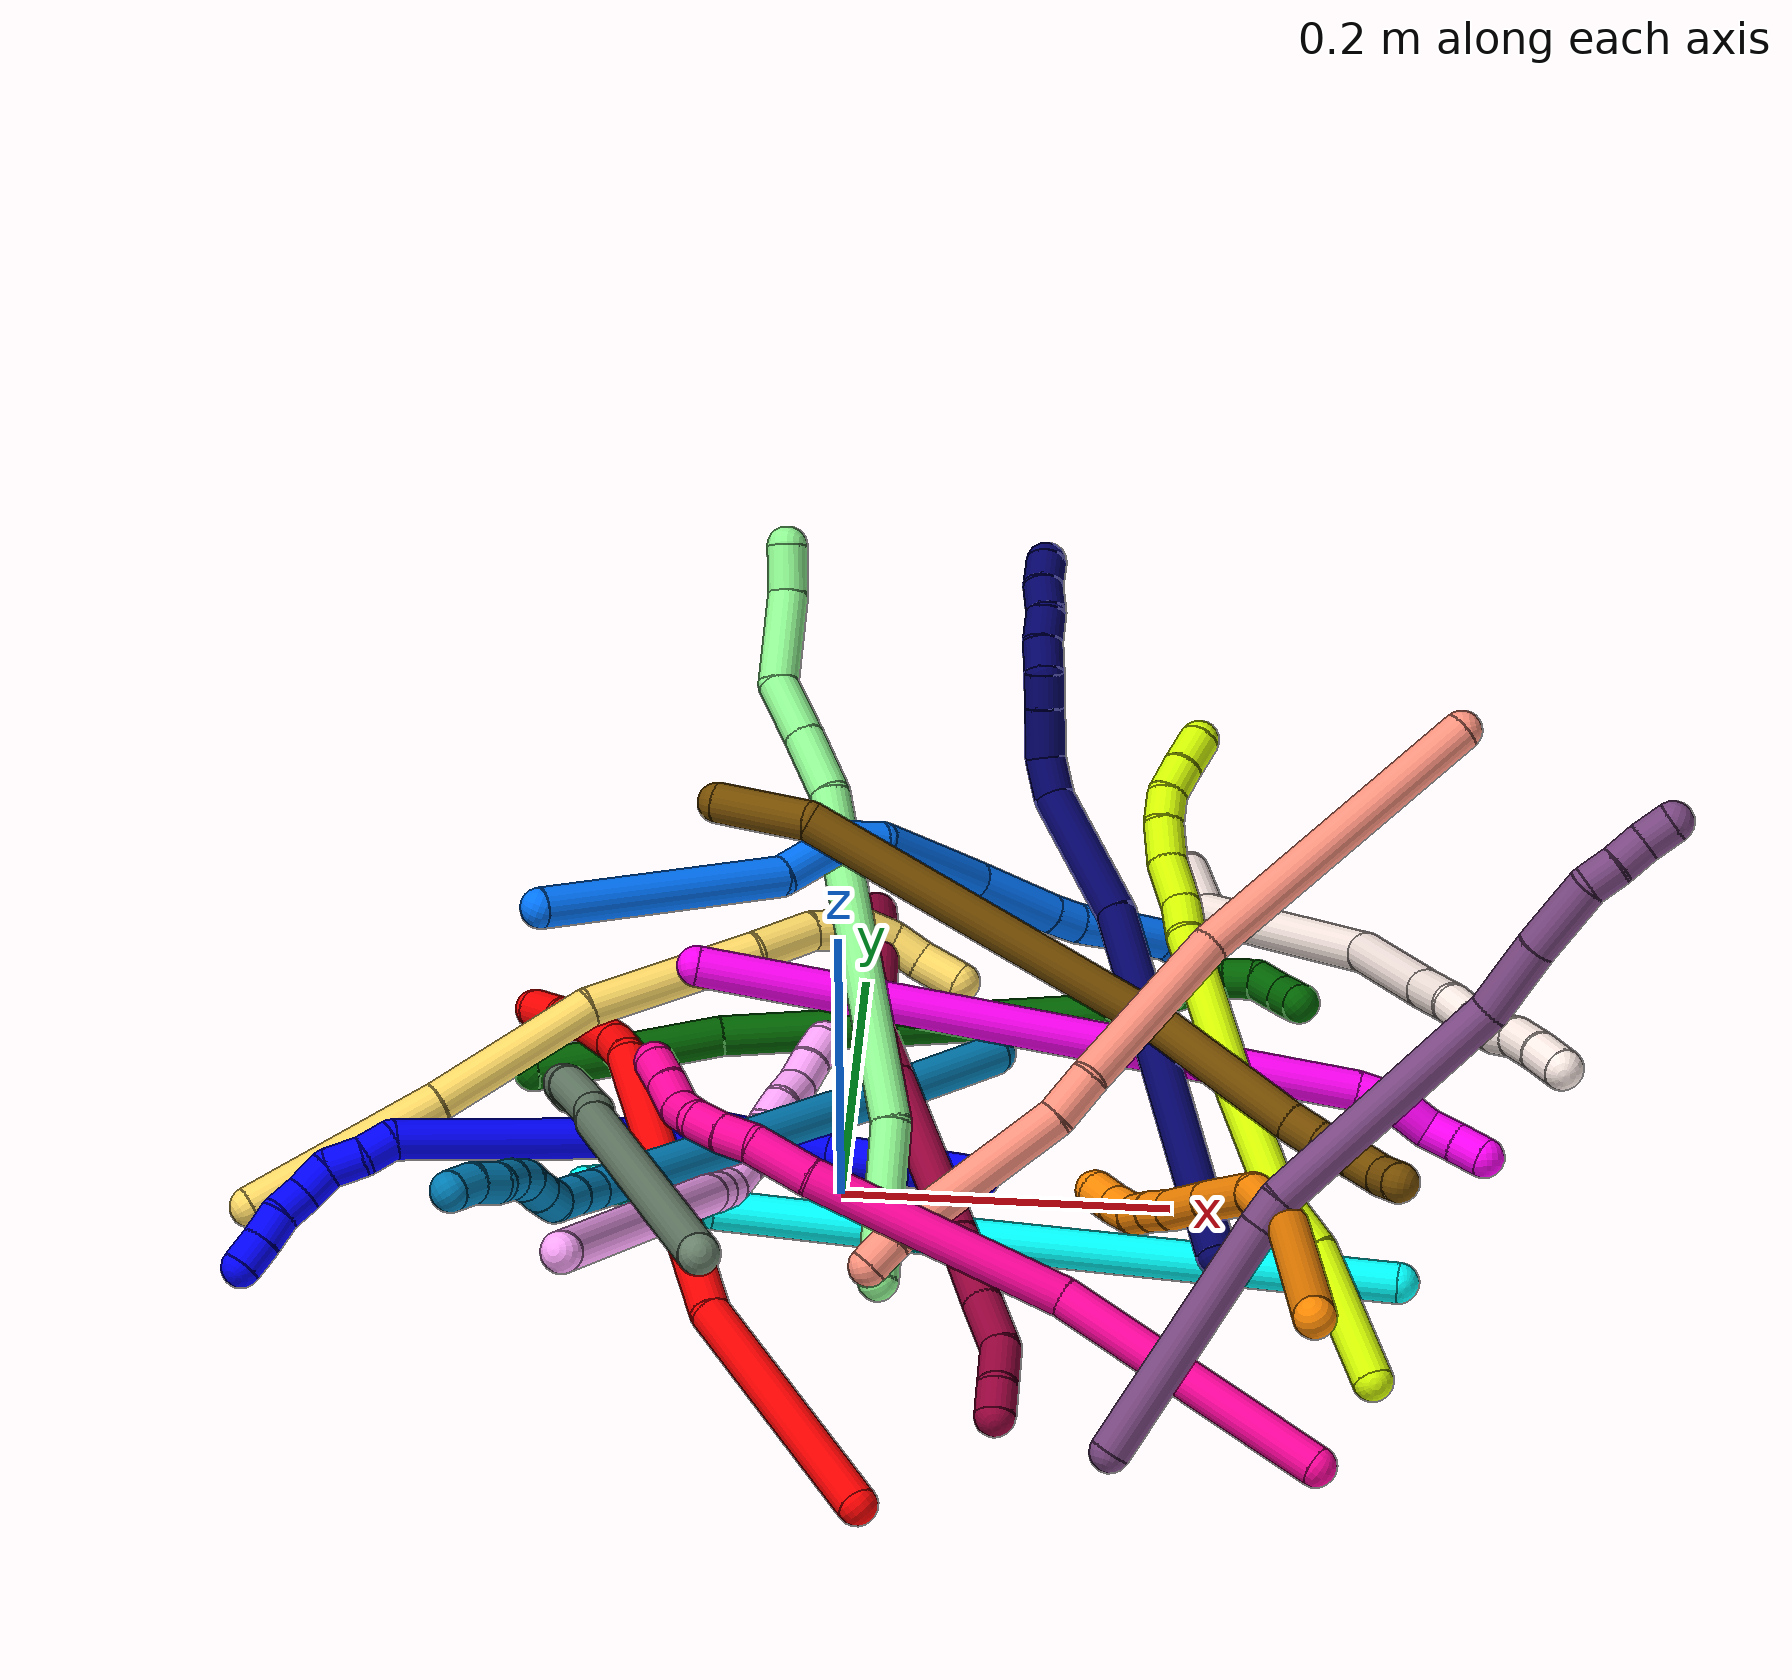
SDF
<sdf version="1.7">
 <world name="default">
  <plugin name="TubeGeneratorPlugin" filename="libtube_generator_plugin.so"/>
  <model name="photoneo_s_sensor">
   <static>1</static>
   <pose>0 0 2 1.57079 1.57079 3.14159</pose>
   <link name="link">
    <inertial><mass>0.1</mass></inertial>
    <sensor name="sensor" type="depth">
     <update_rate>30</update_rate>
     <camera>
      <horizontal_fov>1.22</horizontal_fov>
      <image><width>1920</width><height>1200</height><format>B8G8R8</format></image>
      <clip><near>0.1</near><far>4</far></clip>
      <depth_camera><output>points</output></depth_camera>
     </camera>
     <plugin name="camera_plugin" filename="libgazebo_ros_depth_camera.so">
      <baseline>0.2</baseline>
      <alwaysOn>1</alwaysOn>
      <updateRate>0.0</updateRate>
      <cameraName>camera_ir</cameraName>
      <imageTopicName>/camera/color/image_raw</imageTopicName>
      <cameraInfoTopicName>/camera/color/camera_info</cameraInfoTopicName>
      <depthImageTopicName>/camera/depth/image_raw</depthImageTopicName>
      <depthImageCameraInfoTopicName>/camera/depth/camera_info</depthImageCameraInfoTopicName>
      <pointCloudTopicName>/camera/depth/points</pointCloudTopicName>
      <frameName>fr_optical</frameName>
      <pointCloudCutoff>0.1</pointCloudCutoff>
      <pointCloudCutoffMax>2.0</pointCloudCutoffMax>
      <distortionK1>0</distortionK1>
      <distortionK2>0</distortionK2>
      <distortionK3>0</distortionK3>
      <distortionT1>0</distortionT1>
      <distortionT2>0</distortionT2>
      <CxPrime>0</CxPrime>
      <Cx>0</Cx>
      <Cy>0</Cy>
      <focalLength>0</focalLength>
      <hackBaseline>0</hackBaseline>
     </plugin>
    </sensor>
   </link>
  </model>
  <gravity>0 0 -9.8</gravity>
  <magnetic_field>6e-06 2.3e-05 -4.2e-05</magnetic_field>
  <atmosphere type="adiabatic"/>
  <physics name="default_physics" default="0" type="ode">
   <max_step_size>0.003</max_step_size>
   <real_time_factor>1</real_time_factor>
   <real_time_update_rate>1000</real_time_update_rate>
   <max_contacts>10000</max_contacts>
   <ode>
    <solver>
     <type>quick</type>
     <iters>100</iters>
     <sor>1.3</sor>
     <use_dynamic_moi_rescaling>0</use_dynamic_moi_rescaling>
    </solver>
    <constraints>
     <contact_max_correcting_vel>0</contact_max_correcting_vel>
     <contact_surface_layer>0.001</contact_surface_layer>
     <cfm>0</cfm>
     <erp>0.2</erp>
    </constraints>
   </ode>
  </physics>
  <scene><ambient>0.4 0.4 0.4 1</ambient><background>0.7 0.7 0.7 1</background><shadows>0</shadows></scene>
  <audio><device>default</device></audio>
  <spherical_coordinates>
   <surface_model>EARTH_WGS84</surface_model>
   <latitude_deg>0</latitude_deg>
   <longitude_deg>0</longitude_deg>
   <elevation>0</elevation>
   <heading_deg>0</heading_deg>
  </spherical_coordinates>
  <model name="bin">
   <static>1</static>
   <link name="bottom">
    <collision name="collision-bottom">
     <pose>0 0 -0.01 0 -0 0</pose>
     <geometry><box><size>0.8 0.6 0.02</size></box></geometry>
     <surface>
      <friction><ode><mu>100</mu><mu2>100</mu2></ode></friction>
      <contact><collide_bitmask>65535</collide_bitmask></contact>
     </surface>
    </collision>
   </link>
   <link name="west_wall">
    <collision name="collision-west_wall">
     <pose>-0.41 0 0.1 0 -0 0</pose>
     <geometry><box><size>0.02 0.6 0.2</size></box></geometry>
     <surface>
      <friction><ode><mu>100</mu><mu2>100</mu2></ode></friction>
      <contact><collide_bitmask>65535</collide_bitmask></contact>
     </surface>
    </collision>
   </link>
   <link name="east_wall">
    <collision name="collision-east_wall">
     <pose>0.41 0 0.1 0 -0 0</pose>
     <geometry><box><size>0.02 0.6 0.2</size></box></geometry>
     <surface>
      <friction><ode><mu>100</mu><mu2>100</mu2></ode></friction>
      <contact><collide_bitmask>65535</collide_bitmask></contact>
     </surface>
    </collision>
   </link>
   <link name="south_wall">
    <collision name="collision-south_wall">
     <pose>0 -0.31 0.1 0 -0 0</pose>
     <geometry><box><size>0.8 0.02 0.2</size></box></geometry>
     <surface>
      <friction><ode><mu>100</mu><mu2>100</mu2></ode></friction>
      <contact><collide_bitmask>65535</collide_bitmask></contact>
     </surface>
    </collision>
   </link>
   <link name="north_wall">
    <collision name="collision-north_wall">
     <pose>0 0.31 0.1 0 -0 0</pose>
     <geometry><box><size>0.8 0.02 0.2</size></box></geometry>
     <surface>
      <friction><ode><mu>100</mu><mu2>100</mu2></ode></friction>
      <contact><collide_bitmask>65535</collide_bitmask></contact>
     </surface>
    </collision>
   </link>
  </model>
  <model name="1">
   <static>0</static>
   <link name="1">
    <collision name="collision-cylinder-e_1_1_4">
     <pose>-0.045508 -0.024077 0.001701 1.50025 -1.08313 -1.02181</pose>
     <geometry><cylinder><radius>0.0125</radius><length>0.103025</length></cylinder></geometry>
     <surface>
      <friction><ode><mu>1.16</mu><mu2>1.16</mu2><slip1>0</slip1><slip2>0</slip2></ode></friction>
      <contact><ode><kp>1e+06</kp><kd>1</kd><max_vel>0</max_vel><min_depth>0.001</min_depth></ode></contact>
     </surface>
    </collision>
    <visual name="visual-cylinder-e_1_1_4">
     <pose>-0.045508 -0.024077 0.001701 1.50025 -1.08313 -1.02181</pose>
     <geometry><cylinder><radius>0.0125</radius><length>0.103025</length></cylinder></geometry>
     <material><ambient>0 0 1 1</ambient></material>
    </visual>
    <collision name="collision-cylinder-e_2_4_5">
     <pose>-0.120693 -0.054285 0.014878 0.490712 -1.15763 -0.324387</pose>
     <geometry><cylinder><radius>0.0125</radius><length>0.064809</length></cylinder></geometry>
     <surface>
      <friction><ode><mu>1.16</mu><mu2>1.16</mu2><slip1>0</slip1><slip2>0</slip2></ode></friction>
      <contact><ode><kp>1e+06</kp><kd>1</kd><max_vel>0</max_vel><min_depth>0.001</min_depth></ode></contact>
     </surface>
    </collision>
    <visual name="visual-cylinder-e_2_4_5">
     <pose>-0.120693 -0.054285 0.014878 0.490712 -1.15763 -0.324387</pose>
     <geometry><cylinder><radius>0.0125</radius><length>0.064809</length></cylinder></geometry>
     <material><ambient>0 0 1 1</ambient></material>
    </visual>
    <collision name="collision-cylinder-e_3_5_6">
     <pose>-0.163569 -0.064252 0.039111 0.292066 -0.780784 -0.120903</pose>
     <geometry><cylinder><radius>0.0125</radius><length>0.037505</length></cylinder></geometry>
     <surface>
      <friction><ode><mu>1.16</mu><mu2>1.16</mu2><slip1>0</slip1><slip2>0</slip2></ode></friction>
      <contact><ode><kp>1e+06</kp><kd>1</kd><max_vel>0</max_vel><min_depth>0.001</min_depth></ode></contact>
     </surface>
    </collision>
    <visual name="visual-cylinder-e_3_5_6">
     <pose>-0.163569 -0.064252 0.039111 0.292066 -0.780784 -0.120903</pose>
     <geometry><cylinder><radius>0.0125</radius><length>0.037505</length></cylinder></geometry>
     <material><ambient>0 0 1 1</ambient></material>
    </visual>
    <collision name="collision-cylinder-e_4_6_7">
     <pose>-0.238991 -0.078864 0.108861 0.186878 -0.820479 -0.081468</pose>
     <geometry><cylinder><radius>0.0125</radius><length>0.170131</length></cylinder></geometry>
     <surface>
      <friction><ode><mu>1.16</mu><mu2>1.16</mu2><slip1>0</slip1><slip2>0</slip2></ode></friction>
      <contact><ode><kp>1e+06</kp><kd>1</kd><max_vel>0</max_vel><min_depth>0.001</min_depth></ode></contact>
     </surface>
    </collision>
    <visual name="visual-cylinder-e_4_6_7">
     <pose>-0.238991 -0.078864 0.108861 0.186878 -0.820479 -0.081468</pose>
     <geometry><cylinder><radius>0.0125</radius><length>0.170131</length></cylinder></geometry>
     <material><ambient>0 0 1 1</ambient></material>
    </visual>
    <collision name="collision-cylinder-e_5_7_8">
     <pose>-0.305098 -0.094464 0.173896 0.540322 -0.392703 -0.11006</pose>
     <geometry><cylinder><radius>0.0125</radius><length>0.020298</length></cylinder></geometry>
     <surface>
      <friction><ode><mu>1.16</mu><mu2>1.16</mu2><slip1>0</slip1><slip2>0</slip2></ode></friction>
      <contact><ode><kp>1e+06</kp><kd>1</kd><max_vel>0</max_vel><min_depth>0.001</min_depth></ode></contact>
     </surface>
    </collision>
    <visual name="visual-cylinder-e_5_7_8">
     <pose>-0.305098 -0.094464 0.173896 0.540322 -0.392703 -0.11006</pose>
     <geometry><cylinder><radius>0.0125</radius><length>0.020298</length></cylinder></geometry>
     <material><ambient>0 0 1 1</ambient></material>
    </visual>
    <collision name="collision-cylinder-e_6_8_9">
     <pose>-0.315806 -0.105355 0.188701 0.73111 -0.644111 -0.254056</pose>
     <geometry><cylinder><radius>0.0125</radius><length>0.022729</length></cylinder></geometry>
     <surface>
      <friction><ode><mu>1.16</mu><mu2>1.16</mu2><slip1>0</slip1><slip2>0</slip2></ode></friction>
      <contact><ode><kp>1e+06</kp><kd>1</kd><max_vel>0</max_vel><min_depth>0.001</min_depth></ode></contact>
     </surface>
    </collision>
    <visual name="visual-cylinder-e_6_8_9">
     <pose>-0.315806 -0.105355 0.188701 0.73111 -0.644111 -0.254056</pose>
     <geometry><cylinder><radius>0.0125</radius><length>0.022729</length></cylinder></geometry>
     <material><ambient>0 0 1 1</ambient></material>
    </visual>
    <collision name="collision-cylinder-e_7_9_10">
     <pose>-0.32432 -0.118508 0.203293 0.735707 -0.158713 -0.061277</pose>
     <geometry><cylinder><radius>0.0125</radius><length>0.021384</length></cylinder></geometry>
     <surface>
      <friction><ode><mu>1.16</mu><mu2>1.16</mu2><slip1>0</slip1><slip2>0</slip2></ode></friction>
      <contact><ode><kp>1e+06</kp><kd>1</kd><max_vel>0</max_vel><min_depth>0.001</min_depth></ode></contact>
     </surface>
    </collision>
    <visual name="visual-cylinder-e_7_9_10">
     <pose>-0.32432 -0.118508 0.203293 0.735707 -0.158713 -0.061277</pose>
     <geometry><cylinder><radius>0.0125</radius><length>0.021384</length></cylinder></geometry>
     <material><ambient>0 0 1 1</ambient></material>
    </visual>
    <collision name="collision-cylinder-e_8_10_11">
     <pose>-0.327604 -0.129722 0.220154 0.428671 -0.159177 -0.034719</pose>
     <geometry><cylinder><radius>0.0125</radius><length>0.020119</length></cylinder></geometry>
     <surface>
      <friction><ode><mu>1.16</mu><mu2>1.16</mu2><slip1>0</slip1><slip2>0</slip2></ode></friction>
      <contact><ode><kp>1e+06</kp><kd>1</kd><max_vel>0</max_vel><min_depth>0.001</min_depth></ode></contact>
     </surface>
    </collision>
    <visual name="visual-cylinder-e_8_10_11">
     <pose>-0.327604 -0.129722 0.220154 0.428671 -0.159177 -0.034719</pose>
     <geometry><cylinder><radius>0.0125</radius><length>0.020119</length></cylinder></geometry>
     <material><ambient>0 0 1 1</ambient></material>
    </visual>
    <collision name="collision-cylinder-e_9_11_12">
     <pose>-0.328654 -0.139523 0.237406 0.604126 0.054568 0.017007</pose>
     <geometry><cylinder><radius>0.0125</radius><length>0.02</length></cylinder></geometry>
     <surface>
      <friction><ode><mu>1.16</mu><mu2>1.16</mu2><slip1>0</slip1><slip2>0</slip2></ode></friction>
      <contact><ode><kp>1e+06</kp><kd>1</kd><max_vel>0</max_vel><min_depth>0.001</min_depth></ode></contact>
     </surface>
    </collision>
    <visual name="visual-cylinder-e_9_11_12">
     <pose>-0.328654 -0.139523 0.237406 0.604126 0.054568 0.017007</pose>
     <geometry><cylinder><radius>0.0125</radius><length>0.02</length></cylinder></geometry>
     <material><ambient>0 0 1 1</ambient></material>
    </visual>
    <collision name="collision-cylinder-e_10_12_2">
     <pose>-0.328273 -0.150728 0.253952 0.586417 -0.016447 -0.004966</pose>
     <geometry><cylinder><radius>0.0125</radius><length>0.02</length></cylinder></geometry>
     <surface>
      <friction><ode><mu>1.16</mu><mu2>1.16</mu2><slip1>0</slip1><slip2>0</slip2></ode></friction>
      <contact><ode><kp>1e+06</kp><kd>1</kd><max_vel>0</max_vel><min_depth>0.001</min_depth></ode></contact>
     </surface>
    </collision>
    <visual name="visual-cylinder-e_10_12_2">
     <pose>-0.328273 -0.150728 0.253952 0.586417 -0.016447 -0.004966</pose>
     <geometry><cylinder><radius>0.0125</radius><length>0.02</length></cylinder></geometry>
     <material><ambient>0 0 1 1</ambient></material>
    </visual>
    <collision name="collision-sphere-2">
     <pose>-0.328437 -0.156261 0.26228 0 -0 0</pose>
     <geometry><sphere><radius>0.0125</radius></sphere></geometry>
     <surface>
      <friction><ode><mu>1.16</mu><mu2>1.16</mu2><slip1>0</slip1><slip2>0</slip2></ode></friction>
      <contact><ode><kp>1e+06</kp><kd>1</kd><max_vel>0</max_vel><min_depth>0.001</min_depth></ode></contact>
     </surface>
    </collision>
    <visual name="visual-sphere-2">
     <pose>-0.328437 -0.156261 0.26228 0 -0 0</pose>
     <geometry><sphere><radius>0.0125</radius></sphere></geometry>
     <material><ambient>0 0 1 1</ambient></material>
    </visual>
    <collision name="collision-sphere-12">
     <pose>-0.328108 -0.145195 0.245623 0 -0 0</pose>
     <geometry><sphere><radius>0.0125</radius></sphere></geometry>
     <surface>
      <friction><ode><mu>1.16</mu><mu2>1.16</mu2><slip1>0</slip1><slip2>0</slip2></ode></friction>
      <contact><ode><kp>1e+06</kp><kd>1</kd><max_vel>0</max_vel><min_depth>0.001</min_depth></ode></contact>
     </surface>
    </collision>
    <visual name="visual-sphere-12">
     <pose>-0.328108 -0.145195 0.245623 0 -0 0</pose>
     <geometry><sphere><radius>0.0125</radius></sphere></geometry>
     <material><ambient>0 0 1 1</ambient></material>
    </visual>
    <collision name="collision-sphere-11">
     <pose>-0.329199 -0.133851 0.229188 0 -0 0</pose>
     <geometry><sphere><radius>0.0125</radius></sphere></geometry>
     <surface>
      <friction><ode><mu>1.16</mu><mu2>1.16</mu2><slip1>0</slip1><slip2>0</slip2></ode></friction>
      <contact><ode><kp>1e+06</kp><kd>1</kd><max_vel>0</max_vel><min_depth>0.001</min_depth></ode></contact>
     </surface>
    </collision>
    <visual name="visual-sphere-11">
     <pose>-0.329199 -0.133851 0.229188 0 -0 0</pose>
     <geometry><sphere><radius>0.0125</radius></sphere></geometry>
     <material><ambient>0 0 1 1</ambient></material>
    </visual>
    <collision name="collision-sphere-10">
     <pose>-0.32601 -0.125594 0.21112 0 -0 0</pose>
     <geometry><sphere><radius>0.0125</radius></sphere></geometry>
     <surface>
      <friction><ode><mu>1.16</mu><mu2>1.16</mu2><slip1>0</slip1><slip2>0</slip2></ode></friction>
      <contact><ode><kp>1e+06</kp><kd>1</kd><max_vel>0</max_vel><min_depth>0.001</min_depth></ode></contact>
     </surface>
    </collision>
    <visual name="visual-sphere-10">
     <pose>-0.32601 -0.125594 0.21112 0 -0 0</pose>
     <geometry><sphere><radius>0.0125</radius></sphere></geometry>
     <material><ambient>0 0 1 1</ambient></material>
    </visual>
    <collision name="collision-sphere-9">
     <pose>-0.32263 -0.111423 0.195467 0 -0 0</pose>
     <geometry><sphere><radius>0.0125</radius></sphere></geometry>
     <surface>
      <friction><ode><mu>1.16</mu><mu2>1.16</mu2><slip1>0</slip1><slip2>0</slip2></ode></friction>
      <contact><ode><kp>1e+06</kp><kd>1</kd><max_vel>0</max_vel><min_depth>0.001</min_depth></ode></contact>
     </surface>
    </collision>
    <visual name="visual-sphere-9">
     <pose>-0.32263 -0.111423 0.195467 0 -0 0</pose>
     <geometry><sphere><radius>0.0125</radius></sphere></geometry>
     <material><ambient>0 0 1 1</ambient></material>
    </visual>
    <collision name="collision-sphere-4">
     <pose>-0.091015 -0.048154 0.003403 0 -0 0</pose>
     <geometry><sphere><radius>0.0125</radius></sphere></geometry>
     <surface>
      <friction><ode><mu>1.16</mu><mu2>1.16</mu2><slip1>0</slip1><slip2>0</slip2></ode></friction>
      <contact><ode><kp>1e+06</kp><kd>1</kd><max_vel>0</max_vel><min_depth>0.001</min_depth></ode></contact>
     </surface>
    </collision>
    <visual name="visual-sphere-4">
     <pose>-0.091015 -0.048154 0.003403 0 -0 0</pose>
     <geometry><sphere><radius>0.0125</radius></sphere></geometry>
     <material><ambient>0 0 1 1</ambient></material>
    </visual>
    <collision name="collision-sphere-1">
     <geometry><sphere><radius>0.0125</radius></sphere></geometry>
     <surface>
      <friction><ode><mu>1.16</mu><mu2>1.16</mu2><slip1>0</slip1><slip2>0</slip2></ode></friction>
      <contact><ode><kp>1e+06</kp><kd>1</kd><max_vel>0</max_vel><min_depth>0.001</min_depth></ode></contact>
     </surface>
    </collision>
    <visual name="visual-sphere-1">
     <geometry><sphere><radius>0.0125</radius></sphere></geometry>
     <material><ambient>0 0 1 1</ambient></material>
    </visual>
    <collision name="collision-sphere-8">
     <pose>-0.308982 -0.099288 0.181936 0 -0 0</pose>
     <geometry><sphere><radius>0.0125</radius></sphere></geometry>
     <surface>
      <friction><ode><mu>1.16</mu><mu2>1.16</mu2><slip1>0</slip1><slip2>0</slip2></ode></friction>
      <contact><ode><kp>1e+06</kp><kd>1</kd><max_vel>0</max_vel><min_depth>0.001</min_depth></ode></contact>
     </surface>
    </collision>
    <visual name="visual-sphere-8">
     <pose>-0.308982 -0.099288 0.181936 0 -0 0</pose>
     <geometry><sphere><radius>0.0125</radius></sphere></geometry>
     <material><ambient>0 0 1 1</ambient></material>
    </visual>
    <collision name="collision-sphere-5">
     <pose>-0.150371 -0.060417 0.026354 0 -0 0</pose>
     <geometry><sphere><radius>0.0125</radius></sphere></geometry>
     <surface>
      <friction><ode><mu>1.16</mu><mu2>1.16</mu2><slip1>0</slip1><slip2>0</slip2></ode></friction>
      <contact><ode><kp>1e+06</kp><kd>1</kd><max_vel>0</max_vel><min_depth>0.001</min_depth></ode></contact>
     </surface>
    </collision>
    <visual name="visual-sphere-5">
     <pose>-0.150371 -0.060417 0.026354 0 -0 0</pose>
     <geometry><sphere><radius>0.0125</radius></sphere></geometry>
     <material><ambient>0 0 1 1</ambient></material>
    </visual>
    <collision name="collision-sphere-6">
     <pose>-0.176768 -0.068088 0.051868 0 -0 0</pose>
     <geometry><sphere><radius>0.0125</radius></sphere></geometry>
     <surface>
      <friction><ode><mu>1.16</mu><mu2>1.16</mu2><slip1>0</slip1><slip2>0</slip2></ode></friction>
      <contact><ode><kp>1e+06</kp><kd>1</kd><max_vel>0</max_vel><min_depth>0.001</min_depth></ode></contact>
     </surface>
    </collision>
    <visual name="visual-sphere-6">
     <pose>-0.176768 -0.068088 0.051868 0 -0 0</pose>
     <geometry><sphere><radius>0.0125</radius></sphere></geometry>
     <material><ambient>0 0 1 1</ambient></material>
    </visual>
    <collision name="collision-sphere-7">
     <pose>-0.301214 -0.089641 0.165855 0 -0 0</pose>
     <geometry><sphere><radius>0.0125</radius></sphere></geometry>
     <surface>
      <friction><ode><mu>1.16</mu><mu2>1.16</mu2><slip1>0</slip1><slip2>0</slip2></ode></friction>
      <contact><ode><kp>1e+06</kp><kd>1</kd><max_vel>0</max_vel><min_depth>0.001</min_depth></ode></contact>
     </surface>
    </collision>
    <visual name="visual-sphere-7">
     <pose>-0.301214 -0.089641 0.165855 0 -0 0</pose>
     <geometry><sphere><radius>0.0125</radius></sphere></geometry>
     <material><ambient>0 0 1 1</ambient></material>
    </visual>
    <inertial>
     <pose>-0.198681 -0.074174 0.095099 0 -0 0</pose>
     <mass>0.5</mass>
     <inertia>
      <ixx>0.000238</ixx>
      <ixy>0</ixy>
      <ixz>0</ixz>
      <iyy>0.000448</iyy>
      <iyz>0</iyz>
      <izz>0.000547</izz>
     </inertia>
    </inertial>
   </link>
   <pose>0.085407 -0.015612 0.032172 1.43202 0.286959 -0.476211</pose>
  </model>
  <model name="2">
   <static>0</static>
   <link name="2">
    <collision name="collision-cylinder-e_1_1_4">
     <pose>-0.015164 0.049821 -0.066 -2.49499 -0.181357 0.529995</pose>
     <geometry><cylinder><radius>0.0125</radius><length>0.168144</length></cylinder></geometry>
     <surface>
      <friction><ode><mu>1.16</mu><mu2>1.16</mu2><slip1>0</slip1><slip2>0</slip2></ode></friction>
      <contact><ode><kp>1e+06</kp><kd>1</kd><max_vel>0</max_vel><min_depth>0.001</min_depth></ode></contact>
     </surface>
    </collision>
    <visual name="visual-cylinder-e_1_1_4">
     <pose>-0.015164 0.049821 -0.066 -2.49499 -0.181357 0.529995</pose>
     <geometry><cylinder><radius>0.0125</radius><length>0.168144</length></cylinder></geometry>
     <material><ambient>1 0 0 1</ambient></material>
    </visual>
    <collision name="collision-cylinder-e_2_4_5">
     <pose>-0.078647 0.169644 -0.20134 -2.35143 -0.455944 1.01543</pose>
     <geometry><cylinder><radius>0.0125</radius><length>0.219481</length></cylinder></geometry>
     <surface>
      <friction><ode><mu>1.16</mu><mu2>1.16</mu2><slip1>0</slip1><slip2>0</slip2></ode></friction>
      <contact><ode><kp>1e+06</kp><kd>1</kd><max_vel>0</max_vel><min_depth>0.001</min_depth></ode></contact>
     </surface>
    </collision>
    <visual name="visual-cylinder-e_2_4_5">
     <pose>-0.078647 0.169644 -0.20134 -2.35143 -0.455944 1.01543</pose>
     <geometry><cylinder><radius>0.0125</radius><length>0.219481</length></cylinder></geometry>
     <material><ambient>1 0 0 1</ambient></material>
    </visual>
    <collision name="collision-cylinder-e_3_5_6">
     <pose>-0.129898 0.251446 -0.275568 -1.96364 -0.225537 0.335838</pose>
     <geometry><cylinder><radius>0.0125</radius><length>0.026208</length></cylinder></geometry>
     <surface>
      <friction><ode><mu>1.16</mu><mu2>1.16</mu2><slip1>0</slip1><slip2>0</slip2></ode></friction>
      <contact><ode><kp>1e+06</kp><kd>1</kd><max_vel>0</max_vel><min_depth>0.001</min_depth></ode></contact>
     </surface>
    </collision>
    <visual name="visual-cylinder-e_3_5_6">
     <pose>-0.129898 0.251446 -0.275568 -1.96364 -0.225537 0.335838</pose>
     <geometry><cylinder><radius>0.0125</radius><length>0.026208</length></cylinder></geometry>
     <material><ambient>1 0 0 1</ambient></material>
    </visual>
    <collision name="collision-cylinder-e_4_6_7">
     <pose>-0.133971 0.278695 -0.28926 -2.0887 -0.064187 0.110373</pose>
     <geometry><cylinder><radius>0.0125</radius><length>0.035636</length></cylinder></geometry>
     <surface>
      <friction><ode><mu>1.16</mu><mu2>1.16</mu2><slip1>0</slip1><slip2>0</slip2></ode></friction>
      <contact><ode><kp>1e+06</kp><kd>1</kd><max_vel>0</max_vel><min_depth>0.001</min_depth></ode></contact>
     </surface>
    </collision>
    <visual name="visual-cylinder-e_4_6_7">
     <pose>-0.133971 0.278695 -0.28926 -2.0887 -0.064187 0.110373</pose>
     <geometry><cylinder><radius>0.0125</radius><length>0.035636</length></cylinder></geometry>
     <material><ambient>1 0 0 1</ambient></material>
    </visual>
    <collision name="collision-cylinder-e_5_7_8">
     <pose>-0.132091 0.303021 -0.304606 -2.20599 0.267567 -0.520711</pose>
     <geometry><cylinder><radius>0.0125</radius><length>0.022868</length></cylinder></geometry>
     <surface>
      <friction><ode><mu>1.16</mu><mu2>1.16</mu2><slip1>0</slip1><slip2>0</slip2></ode></friction>
      <contact><ode><kp>1e+06</kp><kd>1</kd><max_vel>0</max_vel><min_depth>0.001</min_depth></ode></contact>
     </surface>
    </collision>
    <visual name="visual-cylinder-e_5_7_8">
     <pose>-0.132091 0.303021 -0.304606 -2.20599 0.267567 -0.520711</pose>
     <geometry><cylinder><radius>0.0125</radius><length>0.022868</length></cylinder></geometry>
     <material><ambient>1 0 0 1</ambient></material>
    </visual>
    <collision name="collision-cylinder-e_6_8_2">
     <pose>-0.127495 0.324177 -0.317316 -2.0362 0.113965 -0.184439</pose>
     <geometry><cylinder><radius>0.0125</radius><length>0.027662</length></cylinder></geometry>
     <surface>
      <friction><ode><mu>1.16</mu><mu2>1.16</mu2><slip1>0</slip1><slip2>0</slip2></ode></friction>
      <contact><ode><kp>1e+06</kp><kd>1</kd><max_vel>0</max_vel><min_depth>0.001</min_depth></ode></contact>
     </surface>
    </collision>
    <visual name="visual-cylinder-e_6_8_2">
     <pose>-0.127495 0.324177 -0.317316 -2.0362 0.113965 -0.184439</pose>
     <geometry><cylinder><radius>0.0125</radius><length>0.027662</length></cylinder></geometry>
     <material><ambient>1 0 0 1</ambient></material>
    </visual>
    <collision name="collision-sphere-2">
     <pose>-0.125922 0.336456 -0.323482 0 -0 0</pose>
     <geometry><sphere><radius>0.0125</radius></sphere></geometry>
     <surface>
      <friction><ode><mu>1.16</mu><mu2>1.16</mu2><slip1>0</slip1><slip2>0</slip2></ode></friction>
      <contact><ode><kp>1e+06</kp><kd>1</kd><max_vel>0</max_vel><min_depth>0.001</min_depth></ode></contact>
     </surface>
    </collision>
    <visual name="visual-sphere-2">
     <pose>-0.125922 0.336456 -0.323482 0 -0 0</pose>
     <geometry><sphere><radius>0.0125</radius></sphere></geometry>
     <material><ambient>1 0 0 1</ambient></material>
    </visual>
    <collision name="collision-sphere-4">
     <pose>-0.030327 0.099642 -0.132001 0 -0 0</pose>
     <geometry><sphere><radius>0.0125</radius></sphere></geometry>
     <surface>
      <friction><ode><mu>1.16</mu><mu2>1.16</mu2><slip1>0</slip1><slip2>0</slip2></ode></friction>
      <contact><ode><kp>1e+06</kp><kd>1</kd><max_vel>0</max_vel><min_depth>0.001</min_depth></ode></contact>
     </surface>
    </collision>
    <visual name="visual-sphere-4">
     <pose>-0.030327 0.099642 -0.132001 0 -0 0</pose>
     <geometry><sphere><radius>0.0125</radius></sphere></geometry>
     <material><ambient>1 0 0 1</ambient></material>
    </visual>
    <collision name="collision-sphere-1">
     <geometry><sphere><radius>0.0125</radius></sphere></geometry>
     <surface>
      <friction><ode><mu>1.16</mu><mu2>1.16</mu2><slip1>0</slip1><slip2>0</slip2></ode></friction>
      <contact><ode><kp>1e+06</kp><kd>1</kd><max_vel>0</max_vel><min_depth>0.001</min_depth></ode></contact>
     </surface>
    </collision>
    <visual name="visual-sphere-1">
     <geometry><sphere><radius>0.0125</radius></sphere></geometry>
     <material><ambient>1 0 0 1</ambient></material>
    </visual>
    <collision name="collision-sphere-8">
     <pose>-0.129068 0.311897 -0.311149 0 -0 0</pose>
     <geometry><sphere><radius>0.0125</radius></sphere></geometry>
     <surface>
      <friction><ode><mu>1.16</mu><mu2>1.16</mu2><slip1>0</slip1><slip2>0</slip2></ode></friction>
      <contact><ode><kp>1e+06</kp><kd>1</kd><max_vel>0</max_vel><min_depth>0.001</min_depth></ode></contact>
     </surface>
    </collision>
    <visual name="visual-sphere-8">
     <pose>-0.129068 0.311897 -0.311149 0 -0 0</pose>
     <geometry><sphere><radius>0.0125</radius></sphere></geometry>
     <material><ambient>1 0 0 1</ambient></material>
    </visual>
    <collision name="collision-sphere-5">
     <pose>-0.126967 0.239647 -0.270679 0 -0 0</pose>
     <geometry><sphere><radius>0.0125</radius></sphere></geometry>
     <surface>
      <friction><ode><mu>1.16</mu><mu2>1.16</mu2><slip1>0</slip1><slip2>0</slip2></ode></friction>
      <contact><ode><kp>1e+06</kp><kd>1</kd><max_vel>0</max_vel><min_depth>0.001</min_depth></ode></contact>
     </surface>
    </collision>
    <visual name="visual-sphere-5">
     <pose>-0.126967 0.239647 -0.270679 0 -0 0</pose>
     <geometry><sphere><radius>0.0125</radius></sphere></geometry>
     <material><ambient>1 0 0 1</ambient></material>
    </visual>
    <collision name="collision-sphere-6">
     <pose>-0.132828 0.263245 -0.280458 0 -0 0</pose>
     <geometry><sphere><radius>0.0125</radius></sphere></geometry>
     <surface>
      <friction><ode><mu>1.16</mu><mu2>1.16</mu2><slip1>0</slip1><slip2>0</slip2></ode></friction>
      <contact><ode><kp>1e+06</kp><kd>1</kd><max_vel>0</max_vel><min_depth>0.001</min_depth></ode></contact>
     </surface>
    </collision>
    <visual name="visual-sphere-6">
     <pose>-0.132828 0.263245 -0.280458 0 -0 0</pose>
     <geometry><sphere><radius>0.0125</radius></sphere></geometry>
     <material><ambient>1 0 0 1</ambient></material>
    </visual>
    <collision name="collision-sphere-7">
     <pose>-0.135114 0.294145 -0.298063 0 -0 0</pose>
     <geometry><sphere><radius>0.0125</radius></sphere></geometry>
     <surface>
      <friction><ode><mu>1.16</mu><mu2>1.16</mu2><slip1>0</slip1><slip2>0</slip2></ode></friction>
      <contact><ode><kp>1e+06</kp><kd>1</kd><max_vel>0</max_vel><min_depth>0.001</min_depth></ode></contact>
     </surface>
    </collision>
    <visual name="visual-sphere-7">
     <pose>-0.135114 0.294145 -0.298063 0 -0 0</pose>
     <geometry><sphere><radius>0.0125</radius></sphere></geometry>
     <material><ambient>1 0 0 1</ambient></material>
    </visual>
    <inertial>
     <pose>-0.069075 0.156059 -0.177123 0 -0 0</pose>
     <mass>0.5</mass>
     <inertia>
      <ixx>0.001644</ixx>
      <ixy>0</ixy>
      <ixz>0</ixz>
      <iyy>0.000551</iyy>
      <iyz>0</iyz>
      <izz>-0.000378</izz>
     </inertia>
    </inertial>
   </link>
   <pose>0.031894 -0.288582 0.012064 -2.30872 0.314336 -2.36888</pose>
  </model>
  <model name="3">
   <static>0</static>
   <link name="3">
    <collision name="collision-cylinder-e_1_1_4">
     <pose>-0.132206 0.014616 -0.063108 -2.914 -1.11519 2.77908</pose>
     <geometry><cylinder><radius>0.0125</radius><length>0.294446</length></cylinder></geometry>
     <surface>
      <friction><ode><mu>1.16</mu><mu2>1.16</mu2><slip1>0</slip1><slip2>0</slip2></ode></friction>
      <contact><ode><kp>1e+06</kp><kd>1</kd><max_vel>0</max_vel><min_depth>0.001</min_depth></ode></contact>
     </surface>
    </collision>
    <visual name="visual-cylinder-e_1_1_4">
     <pose>-0.132206 0.014616 -0.063108 -2.914 -1.11519 2.77908</pose>
     <geometry><cylinder><radius>0.0125</radius><length>0.294446</length></cylinder></geometry>
     <material><ambient>0.003922 1 0.996078 1</ambient></material>
    </visual>
    <collision name="collision-cylinder-e_2_4_5">
     <pose>-0.319234 0.035861 -0.152931 -2.89835 -1.10549 2.7504</pose>
     <geometry><cylinder><radius>0.0125</radius><length>0.122689</length></cylinder></geometry>
     <surface>
      <friction><ode><mu>1.16</mu><mu2>1.16</mu2><slip1>0</slip1><slip2>0</slip2></ode></friction>
      <contact><ode><kp>1e+06</kp><kd>1</kd><max_vel>0</max_vel><min_depth>0.001</min_depth></ode></contact>
     </surface>
    </collision>
    <visual name="visual-cylinder-e_2_4_5">
     <pose>-0.319234 0.035861 -0.152931 -2.89835 -1.10549 2.7504</pose>
     <geometry><cylinder><radius>0.0125</radius><length>0.122689</length></cylinder></geometry>
     <material><ambient>0.003922 1 0.996078 1</ambient></material>
    </visual>
    <collision name="collision-cylinder-e_3_5_6">
     <pose>-0.390189 0.047033 -0.181714 -1.99804 -1.27077 1.70661</pose>
     <geometry><cylinder><radius>0.0125</radius><length>0.033774</length></cylinder></geometry>
     <surface>
      <friction><ode><mu>1.16</mu><mu2>1.16</mu2><slip1>0</slip1><slip2>0</slip2></ode></friction>
      <contact><ode><kp>1e+06</kp><kd>1</kd><max_vel>0</max_vel><min_depth>0.001</min_depth></ode></contact>
     </surface>
    </collision>
    <visual name="visual-cylinder-e_3_5_6">
     <pose>-0.390189 0.047033 -0.181714 -1.99804 -1.27077 1.70661</pose>
     <geometry><cylinder><radius>0.0125</radius><length>0.033774</length></cylinder></geometry>
     <material><ambient>0.003922 1 0.996078 1</ambient></material>
    </visual>
    <collision name="collision-cylinder-e_4_6_7">
     <pose>-0.417463 0.057122 -0.185572 -1.88303 -1.08882 1.38747</pose>
     <geometry><cylinder><radius>0.0125</radius><length>0.025147</length></cylinder></geometry>
     <surface>
      <friction><ode><mu>1.16</mu><mu2>1.16</mu2><slip1>0</slip1><slip2>0</slip2></ode></friction>
      <contact><ode><kp>1e+06</kp><kd>1</kd><max_vel>0</max_vel><min_depth>0.001</min_depth></ode></contact>
     </surface>
    </collision>
    <visual name="visual-cylinder-e_4_6_7">
     <pose>-0.417463 0.057122 -0.185572 -1.88303 -1.08882 1.38747</pose>
     <geometry><cylinder><radius>0.0125</radius><length>0.025147</length></cylinder></geometry>
     <material><ambient>0.003922 1 0.996078 1</ambient></material>
    </visual>
    <collision name="collision-cylinder-e_5_7_2">
     <pose>-0.440381 0.063883 -0.185583 -0.599322 -1.38982 0.504165</pose>
     <geometry><cylinder><radius>0.0125</radius><length>0.023944</length></cylinder></geometry>
     <surface>
      <friction><ode><mu>1.16</mu><mu2>1.16</mu2><slip1>0</slip1><slip2>0</slip2></ode></friction>
      <contact><ode><kp>1e+06</kp><kd>1</kd><max_vel>0</max_vel><min_depth>0.001</min_depth></ode></contact>
     </surface>
    </collision>
    <visual name="visual-cylinder-e_5_7_2">
     <pose>-0.440381 0.063883 -0.185583 -0.599322 -1.38982 0.504165</pose>
     <geometry><cylinder><radius>0.0125</radius><length>0.023944</length></cylinder></geometry>
     <material><ambient>0.003922 1 0.996078 1</ambient></material>
    </visual>
    <collision name="collision-sphere-2">
     <pose>-0.452157 0.065099 -0.183804 0 -0 0</pose>
     <geometry><sphere><radius>0.0125</radius></sphere></geometry>
     <surface>
      <friction><ode><mu>1.16</mu><mu2>1.16</mu2><slip1>0</slip1><slip2>0</slip2></ode></friction>
      <contact><ode><kp>1e+06</kp><kd>1</kd><max_vel>0</max_vel><min_depth>0.001</min_depth></ode></contact>
     </surface>
    </collision>
    <visual name="visual-sphere-2">
     <pose>-0.452157 0.065099 -0.183804 0 -0 0</pose>
     <geometry><sphere><radius>0.0125</radius></sphere></geometry>
     <material><ambient>0.003922 1 0.996078 1</ambient></material>
    </visual>
    <collision name="collision-sphere-7">
     <pose>-0.428604 0.062668 -0.187362 0 -0 0</pose>
     <geometry><sphere><radius>0.0125</radius></sphere></geometry>
     <surface>
      <friction><ode><mu>1.16</mu><mu2>1.16</mu2><slip1>0</slip1><slip2>0</slip2></ode></friction>
      <contact><ode><kp>1e+06</kp><kd>1</kd><max_vel>0</max_vel><min_depth>0.001</min_depth></ode></contact>
     </surface>
    </collision>
    <visual name="visual-sphere-7">
     <pose>-0.428604 0.062668 -0.187362 0 -0 0</pose>
     <geometry><sphere><radius>0.0125</radius></sphere></geometry>
     <material><ambient>0.003922 1 0.996078 1</ambient></material>
    </visual>
    <collision name="collision-sphere-6">
     <pose>-0.406322 0.051575 -0.183782 0 -0 0</pose>
     <geometry><sphere><radius>0.0125</radius></sphere></geometry>
     <surface>
      <friction><ode><mu>1.16</mu><mu2>1.16</mu2><slip1>0</slip1><slip2>0</slip2></ode></friction>
      <contact><ode><kp>1e+06</kp><kd>1</kd><max_vel>0</max_vel><min_depth>0.001</min_depth></ode></contact>
     </surface>
    </collision>
    <visual name="visual-sphere-6">
     <pose>-0.406322 0.051575 -0.183782 0 -0 0</pose>
     <geometry><sphere><radius>0.0125</radius></sphere></geometry>
     <material><ambient>0.003922 1 0.996078 1</ambient></material>
    </visual>
    <collision name="collision-sphere-5">
     <pose>-0.374057 0.042491 -0.179645 0 -0 0</pose>
     <geometry><sphere><radius>0.0125</radius></sphere></geometry>
     <surface>
      <friction><ode><mu>1.16</mu><mu2>1.16</mu2><slip1>0</slip1><slip2>0</slip2></ode></friction>
      <contact><ode><kp>1e+06</kp><kd>1</kd><max_vel>0</max_vel><min_depth>0.001</min_depth></ode></contact>
     </surface>
    </collision>
    <visual name="visual-sphere-5">
     <pose>-0.374057 0.042491 -0.179645 0 -0 0</pose>
     <geometry><sphere><radius>0.0125</radius></sphere></geometry>
     <material><ambient>0.003922 1 0.996078 1</ambient></material>
    </visual>
    <collision name="collision-sphere-1">
     <geometry><sphere><radius>0.0125</radius></sphere></geometry>
     <surface>
      <friction><ode><mu>1.16</mu><mu2>1.16</mu2><slip1>0</slip1><slip2>0</slip2></ode></friction>
      <contact><ode><kp>1e+06</kp><kd>1</kd><max_vel>0</max_vel><min_depth>0.001</min_depth></ode></contact>
     </surface>
    </collision>
    <visual name="visual-sphere-1">
     <geometry><sphere><radius>0.0125</radius></sphere></geometry>
     <material><ambient>0.003922 1 0.996078 1</ambient></material>
    </visual>
    <collision name="collision-sphere-4">
     <pose>-0.264412 0.029232 -0.126216 0 -0 0</pose>
     <geometry><sphere><radius>0.0125</radius></sphere></geometry>
     <surface>
      <friction><ode><mu>1.16</mu><mu2>1.16</mu2><slip1>0</slip1><slip2>0</slip2></ode></friction>
      <contact><ode><kp>1e+06</kp><kd>1</kd><max_vel>0</max_vel><min_depth>0.001</min_depth></ode></contact>
     </surface>
    </collision>
    <visual name="visual-sphere-4">
     <pose>-0.264412 0.029232 -0.126216 0 -0 0</pose>
     <geometry><sphere><radius>0.0125</radius></sphere></geometry>
     <material><ambient>0.003922 1 0.996078 1</ambient></material>
    </visual>
    <inertial>
     <pose>-0.224629 0.026516 -0.105184 0 -0 0</pose>
     <mass>0.5</mass>
     <inertia>
      <ixx>-0.000617</ixx>
      <ixy>0</ixy>
      <ixz>0</ixz>
      <iyy>0.002634</iyy>
      <iyz>0</iyz>
      <izz>0.001825</izz>
     </inertia>
    </inertial>
   </link>
   <pose>0.340594 -0.071135 0.01206 1.1376 0.09771 0.358022</pose>
  </model>
  <model name="4">
   <static>0</static>
   <link name="4">
    <collision name="collision-cylinder-e_1_1_4">
     <pose>-0.017326 0.029912 -0.154836 -2.95076 -0.109431 1.03956</pose>
     <geometry><cylinder><radius>0.0125</radius><length>0.317296</length></cylinder></geometry>
     <surface>
      <friction><ode><mu>1.16</mu><mu2>1.16</mu2><slip1>0</slip1><slip2>0</slip2></ode></friction>
      <contact><ode><kp>1e+06</kp><kd>1</kd><max_vel>0</max_vel><min_depth>0.001</min_depth></ode></contact>
     </surface>
    </collision>
    <visual name="visual-cylinder-e_1_1_4">
     <pose>-0.017326 0.029912 -0.154836 -2.95076 -0.109431 1.03956</pose>
     <geometry><cylinder><radius>0.0125</radius><length>0.317296</length></cylinder></geometry>
     <material><ambient>1 0.65098 0.996078 1</ambient></material>
    </visual>
    <collision name="collision-cylinder-e_2_4_5">
     <pose>-0.035877 0.061721 -0.320797 -2.97266 -0.108056 1.13685</pose>
     <geometry><cylinder><radius>0.0125</radius><length>0.022704</length></cylinder></geometry>
     <surface>
      <friction><ode><mu>1.16</mu><mu2>1.16</mu2><slip1>0</slip1><slip2>0</slip2></ode></friction>
      <contact><ode><kp>1e+06</kp><kd>1</kd><max_vel>0</max_vel><min_depth>0.001</min_depth></ode></contact>
     </surface>
    </collision>
    <visual name="visual-cylinder-e_2_4_5">
     <pose>-0.035877 0.061721 -0.320797 -2.97266 -0.108056 1.13685</pose>
     <geometry><cylinder><radius>0.0125</radius><length>0.022704</length></cylinder></geometry>
     <material><ambient>1 0.65098 0.996078 1</ambient></material>
    </visual>
    <collision name="collision-cylinder-e_3_5_6">
     <pose>-0.037428 0.06586 -0.341662 -2.91537 -0.032704 0.285957</pose>
     <geometry><cylinder><radius>0.0125</radius><length>0.02</length></cylinder></geometry>
     <surface>
      <friction><ode><mu>1.16</mu><mu2>1.16</mu2><slip1>0</slip1><slip2>0</slip2></ode></friction>
      <contact><ode><kp>1e+06</kp><kd>1</kd><max_vel>0</max_vel><min_depth>0.001</min_depth></ode></contact>
     </surface>
    </collision>
    <visual name="visual-cylinder-e_3_5_6">
     <pose>-0.037428 0.06586 -0.341662 -2.91537 -0.032704 0.285957</pose>
     <geometry><cylinder><radius>0.0125</radius><length>0.02</length></cylinder></geometry>
     <material><ambient>1 0.65098 0.996078 1</ambient></material>
    </visual>
    <collision name="collision-cylinder-e_4_6_7">
     <pose>-0.036447 0.074492 -0.358983 -2.44119 0.13116 -0.355803</pose>
     <geometry><cylinder><radius>0.0125</radius><length>0.02</length></cylinder></geometry>
     <surface>
      <friction><ode><mu>1.16</mu><mu2>1.16</mu2><slip1>0</slip1><slip2>0</slip2></ode></friction>
      <contact><ode><kp>1e+06</kp><kd>1</kd><max_vel>0</max_vel><min_depth>0.001</min_depth></ode></contact>
     </surface>
    </collision>
    <visual name="visual-cylinder-e_4_6_7">
     <pose>-0.036447 0.074492 -0.358983 -2.44119 0.13116 -0.355803</pose>
     <geometry><cylinder><radius>0.0125</radius><length>0.02</length></cylinder></geometry>
     <material><ambient>1 0.65098 0.996078 1</ambient></material>
    </visual>
    <collision name="collision-cylinder-e_5_7_8">
     <pose>-0.034218 0.08658 -0.374729 -2.53236 0.092289 -0.291664</pose>
     <geometry><cylinder><radius>0.0125</radius><length>0.02</length></cylinder></geometry>
     <surface>
      <friction><ode><mu>1.16</mu><mu2>1.16</mu2><slip1>0</slip1><slip2>0</slip2></ode></friction>
      <contact><ode><kp>1e+06</kp><kd>1</kd><max_vel>0</max_vel><min_depth>0.001</min_depth></ode></contact>
     </surface>
    </collision>
    <visual name="visual-cylinder-e_5_7_8">
     <pose>-0.034218 0.08658 -0.374729 -2.53236 0.092289 -0.291664</pose>
     <geometry><cylinder><radius>0.0125</radius><length>0.02</length></cylinder></geometry>
     <material><ambient>1 0.65098 0.996078 1</ambient></material>
    </visual>
    <collision name="collision-cylinder-e_6_8_9">
     <pose>-0.032096 0.101262 -0.38712 -2.01038 0.12035 -0.189252</pose>
     <geometry><cylinder><radius>0.0125</radius><length>0.02</length></cylinder></geometry>
     <surface>
      <friction><ode><mu>1.16</mu><mu2>1.16</mu2><slip1>0</slip1><slip2>0</slip2></ode></friction>
      <contact><ode><kp>1e+06</kp><kd>1</kd><max_vel>0</max_vel><min_depth>0.001</min_depth></ode></contact>
     </surface>
    </collision>
    <visual name="visual-cylinder-e_6_8_9">
     <pose>-0.032096 0.101262 -0.38712 -2.01038 0.12035 -0.189252</pose>
     <geometry><cylinder><radius>0.0125</radius><length>0.02</length></cylinder></geometry>
     <material><ambient>1 0.65098 0.996078 1</ambient></material>
    </visual>
    <collision name="collision-cylinder-e_7_9_10">
     <pose>-0.028928 0.117637 -0.397786 -2.28765 0.198036 -0.429963</pose>
     <geometry><cylinder><radius>0.0125</radius><length>0.02</length></cylinder></geometry>
     <surface>
      <friction><ode><mu>1.16</mu><mu2>1.16</mu2><slip1>0</slip1><slip2>0</slip2></ode></friction>
      <contact><ode><kp>1e+06</kp><kd>1</kd><max_vel>0</max_vel><min_depth>0.001</min_depth></ode></contact>
     </surface>
    </collision>
    <visual name="visual-cylinder-e_7_9_10">
     <pose>-0.028928 0.117637 -0.397786 -2.28765 0.198036 -0.429963</pose>
     <geometry><cylinder><radius>0.0125</radius><length>0.02</length></cylinder></geometry>
     <material><ambient>1 0.65098 0.996078 1</ambient></material>
    </visual>
    <collision name="collision-cylinder-e_8_10_11">
     <pose>-0.025608 0.131035 -0.412108 -2.4902 0.135614 -0.396878</pose>
     <geometry><cylinder><radius>0.0125</radius><length>0.02</length></cylinder></geometry>
     <surface>
      <friction><ode><mu>1.16</mu><mu2>1.16</mu2><slip1>0</slip1><slip2>0</slip2></ode></friction>
      <contact><ode><kp>1e+06</kp><kd>1</kd><max_vel>0</max_vel><min_depth>0.001</min_depth></ode></contact>
     </surface>
    </collision>
    <visual name="visual-cylinder-e_8_10_11">
     <pose>-0.025608 0.131035 -0.412108 -2.4902 0.135614 -0.396878</pose>
     <geometry><cylinder><radius>0.0125</radius><length>0.02</length></cylinder></geometry>
     <material><ambient>1 0.65098 0.996078 1</ambient></material>
    </visual>
    <collision name="collision-cylinder-e_9_11_12">
     <pose>-0.022556 0.144877 -0.425965 -2.22257 0.170874 -0.342758</pose>
     <geometry><cylinder><radius>0.0125</radius><length>0.02</length></cylinder></geometry>
     <surface>
      <friction><ode><mu>1.16</mu><mu2>1.16</mu2><slip1>0</slip1><slip2>0</slip2></ode></friction>
      <contact><ode><kp>1e+06</kp><kd>1</kd><max_vel>0</max_vel><min_depth>0.001</min_depth></ode></contact>
     </surface>
    </collision>
    <visual name="visual-cylinder-e_9_11_12">
     <pose>-0.022556 0.144877 -0.425965 -2.22257 0.170874 -0.342758</pose>
     <geometry><cylinder><radius>0.0125</radius><length>0.02</length></cylinder></geometry>
     <material><ambient>1 0.65098 0.996078 1</ambient></material>
    </visual>
    <collision name="collision-cylinder-e_10_12_2">
     <pose>-0.019127 0.159929 -0.438645 -2.31922 0.173652 -0.39407</pose>
     <geometry><cylinder><radius>0.0125</radius><length>0.02</length></cylinder></geometry>
     <surface>
      <friction><ode><mu>1.16</mu><mu2>1.16</mu2><slip1>0</slip1><slip2>0</slip2></ode></friction>
      <contact><ode><kp>1e+06</kp><kd>1</kd><max_vel>0</max_vel><min_depth>0.001</min_depth></ode></contact>
     </surface>
    </collision>
    <visual name="visual-cylinder-e_10_12_2">
     <pose>-0.019127 0.159929 -0.438645 -2.31922 0.173652 -0.39407</pose>
     <geometry><cylinder><radius>0.0125</radius><length>0.02</length></cylinder></geometry>
     <material><ambient>1 0.65098 0.996078 1</ambient></material>
    </visual>
    <collision name="collision-sphere-2">
     <pose>-0.0174 0.167146 -0.445347 0 -0 0</pose>
     <geometry><sphere><radius>0.0125</radius></sphere></geometry>
     <surface>
      <friction><ode><mu>1.16</mu><mu2>1.16</mu2><slip1>0</slip1><slip2>0</slip2></ode></friction>
      <contact><ode><kp>1e+06</kp><kd>1</kd><max_vel>0</max_vel><min_depth>0.001</min_depth></ode></contact>
     </surface>
    </collision>
    <visual name="visual-sphere-2">
     <pose>-0.0174 0.167146 -0.445347 0 -0 0</pose>
     <geometry><sphere><radius>0.0125</radius></sphere></geometry>
     <material><ambient>1 0.65098 0.996078 1</ambient></material>
    </visual>
    <collision name="collision-sphere-12">
     <pose>-0.020855 0.152711 -0.431942 0 -0 0</pose>
     <geometry><sphere><radius>0.0125</radius></sphere></geometry>
     <surface>
      <friction><ode><mu>1.16</mu><mu2>1.16</mu2><slip1>0</slip1><slip2>0</slip2></ode></friction>
      <contact><ode><kp>1e+06</kp><kd>1</kd><max_vel>0</max_vel><min_depth>0.001</min_depth></ode></contact>
     </surface>
    </collision>
    <visual name="visual-sphere-12">
     <pose>-0.020855 0.152711 -0.431942 0 -0 0</pose>
     <geometry><sphere><radius>0.0125</radius></sphere></geometry>
     <material><ambient>1 0.65098 0.996078 1</ambient></material>
    </visual>
    <collision name="collision-sphere-11">
     <pose>-0.024256 0.137043 -0.419987 0 -0 0</pose>
     <geometry><sphere><radius>0.0125</radius></sphere></geometry>
     <surface>
      <friction><ode><mu>1.16</mu><mu2>1.16</mu2><slip1>0</slip1><slip2>0</slip2></ode></friction>
      <contact><ode><kp>1e+06</kp><kd>1</kd><max_vel>0</max_vel><min_depth>0.001</min_depth></ode></contact>
     </surface>
    </collision>
    <visual name="visual-sphere-11">
     <pose>-0.024256 0.137043 -0.419987 0 -0 0</pose>
     <geometry><sphere><radius>0.0125</radius></sphere></geometry>
     <material><ambient>1 0.65098 0.996078 1</ambient></material>
    </visual>
    <collision name="collision-sphere-10">
     <pose>-0.02696 0.125028 -0.404228 0 -0 0</pose>
     <geometry><sphere><radius>0.0125</radius></sphere></geometry>
     <surface>
      <friction><ode><mu>1.16</mu><mu2>1.16</mu2><slip1>0</slip1><slip2>0</slip2></ode></friction>
      <contact><ode><kp>1e+06</kp><kd>1</kd><max_vel>0</max_vel><min_depth>0.001</min_depth></ode></contact>
     </surface>
    </collision>
    <visual name="visual-sphere-10">
     <pose>-0.02696 0.125028 -0.404228 0 -0 0</pose>
     <geometry><sphere><radius>0.0125</radius></sphere></geometry>
     <material><ambient>1 0.65098 0.996078 1</ambient></material>
    </visual>
    <collision name="collision-sphere-9">
     <pose>-0.030895 0.110245 -0.391345 0 -0 0</pose>
     <geometry><sphere><radius>0.0125</radius></sphere></geometry>
     <surface>
      <friction><ode><mu>1.16</mu><mu2>1.16</mu2><slip1>0</slip1><slip2>0</slip2></ode></friction>
      <contact><ode><kp>1e+06</kp><kd>1</kd><max_vel>0</max_vel><min_depth>0.001</min_depth></ode></contact>
     </surface>
    </collision>
    <visual name="visual-sphere-9">
     <pose>-0.030895 0.110245 -0.391345 0 -0 0</pose>
     <geometry><sphere><radius>0.0125</radius></sphere></geometry>
     <material><ambient>1 0.65098 0.996078 1</ambient></material>
    </visual>
    <collision name="collision-sphere-4">
     <pose>-0.034653 0.059823 -0.309672 0 -0 0</pose>
     <geometry><sphere><radius>0.0125</radius></sphere></geometry>
     <surface>
      <friction><ode><mu>1.16</mu><mu2>1.16</mu2><slip1>0</slip1><slip2>0</slip2></ode></friction>
      <contact><ode><kp>1e+06</kp><kd>1</kd><max_vel>0</max_vel><min_depth>0.001</min_depth></ode></contact>
     </surface>
    </collision>
    <visual name="visual-sphere-4">
     <pose>-0.034653 0.059823 -0.309672 0 -0 0</pose>
     <geometry><sphere><radius>0.0125</radius></sphere></geometry>
     <material><ambient>1 0.65098 0.996078 1</ambient></material>
    </visual>
    <collision name="collision-sphere-1">
     <geometry><sphere><radius>0.0125</radius></sphere></geometry>
     <surface>
      <friction><ode><mu>1.16</mu><mu2>1.16</mu2><slip1>0</slip1><slip2>0</slip2></ode></friction>
      <contact><ode><kp>1e+06</kp><kd>1</kd><max_vel>0</max_vel><min_depth>0.001</min_depth></ode></contact>
     </surface>
    </collision>
    <visual name="visual-sphere-1">
     <geometry><sphere><radius>0.0125</radius></sphere></geometry>
     <material><ambient>1 0.65098 0.996078 1</ambient></material>
    </visual>
    <collision name="collision-sphere-8">
     <pose>-0.033296 0.092278 -0.382895 0 -0 0</pose>
     <geometry><sphere><radius>0.0125</radius></sphere></geometry>
     <surface>
      <friction><ode><mu>1.16</mu><mu2>1.16</mu2><slip1>0</slip1><slip2>0</slip2></ode></friction>
      <contact><ode><kp>1e+06</kp><kd>1</kd><max_vel>0</max_vel><min_depth>0.001</min_depth></ode></contact>
     </surface>
    </collision>
    <visual name="visual-sphere-8">
     <pose>-0.033296 0.092278 -0.382895 0 -0 0</pose>
     <geometry><sphere><radius>0.0125</radius></sphere></geometry>
     <material><ambient>1 0.65098 0.996078 1</ambient></material>
    </visual>
    <collision name="collision-sphere-5">
     <pose>-0.037101 0.063618 -0.331922 0 -0 0</pose>
     <geometry><sphere><radius>0.0125</radius></sphere></geometry>
     <surface>
      <friction><ode><mu>1.16</mu><mu2>1.16</mu2><slip1>0</slip1><slip2>0</slip2></ode></friction>
      <contact><ode><kp>1e+06</kp><kd>1</kd><max_vel>0</max_vel><min_depth>0.001</min_depth></ode></contact>
     </surface>
    </collision>
    <visual name="visual-sphere-5">
     <pose>-0.037101 0.063618 -0.331922 0 -0 0</pose>
     <geometry><sphere><radius>0.0125</radius></sphere></geometry>
     <material><ambient>1 0.65098 0.996078 1</ambient></material>
    </visual>
    <collision name="collision-sphere-6">
     <pose>-0.037755 0.068102 -0.351402 0 -0 0</pose>
     <geometry><sphere><radius>0.0125</radius></sphere></geometry>
     <surface>
      <friction><ode><mu>1.16</mu><mu2>1.16</mu2><slip1>0</slip1><slip2>0</slip2></ode></friction>
      <contact><ode><kp>1e+06</kp><kd>1</kd><max_vel>0</max_vel><min_depth>0.001</min_depth></ode></contact>
     </surface>
    </collision>
    <visual name="visual-sphere-6">
     <pose>-0.037755 0.068102 -0.351402 0 -0 0</pose>
     <geometry><sphere><radius>0.0125</radius></sphere></geometry>
     <material><ambient>1 0.65098 0.996078 1</ambient></material>
    </visual>
    <collision name="collision-sphere-7">
     <pose>-0.035139 0.080882 -0.366563 0 -0 0</pose>
     <geometry><sphere><radius>0.0125</radius></sphere></geometry>
     <surface>
      <friction><ode><mu>1.16</mu><mu2>1.16</mu2><slip1>0</slip1><slip2>0</slip2></ode></friction>
      <contact><ode><kp>1e+06</kp><kd>1</kd><max_vel>0</max_vel><min_depth>0.001</min_depth></ode></contact>
     </surface>
    </collision>
    <visual name="visual-sphere-7">
     <pose>-0.035139 0.080882 -0.366563 0 -0 0</pose>
     <geometry><sphere><radius>0.0125</radius></sphere></geometry>
     <material><ambient>1 0.65098 0.996078 1</ambient></material>
    </visual>
    <inertial>
     <pose>-0.022081 0.057051 -0.238305 0 -0 0</pose>
     <mass>0.5</mass>
     <inertia>
      <ixx>0.003648</ixx>
      <ixy>0</ixy>
      <ixz>0</ixz>
      <iyy>0.001013</iyy>
      <iyz>0</iyz>
      <izz>-0.000256</izz>
     </inertia>
    </inertial>
   </link>
   <pose>-0.131008 -0.332506 0.237517 0.796802 -0.202892 -0.21476</pose>
  </model>
  <model name="5">
   <static>0</static>
   <link name="5">
    <collision name="collision-cylinder-e_1_1_4">
     <pose>0.003058 -0.003305 0.065628 0.050324 0.046498 0.00117</pose>
     <geometry><cylinder><radius>0.0125</radius><length>0.131564</length></cylinder></geometry>
     <surface>
      <friction><ode><mu>1.16</mu><mu2>1.16</mu2><slip1>0</slip1><slip2>0</slip2></ode></friction>
      <contact><ode><kp>1e+06</kp><kd>1</kd><max_vel>0</max_vel><min_depth>0.001</min_depth></ode></contact>
     </surface>
    </collision>
    <visual name="visual-cylinder-e_1_1_4">
     <pose>0.003058 -0.003305 0.065628 0.050324 0.046498 0.00117</pose>
     <geometry><cylinder><radius>0.0125</radius><length>0.131564</length></cylinder></geometry>
     <material><ambient>1 0.858824 0.4 1</ambient></material>
    </visual>
    <collision name="collision-cylinder-e_2_4_5">
     <pose>0.005292 -0.006835 0.186494 0.004054 -0.014897 -3e-05</pose>
     <geometry><cylinder><radius>0.0125</radius><length>0.11049</length></cylinder></geometry>
     <surface>
      <friction><ode><mu>1.16</mu><mu2>1.16</mu2><slip1>0</slip1><slip2>0</slip2></ode></friction>
      <contact><ode><kp>1e+06</kp><kd>1</kd><max_vel>0</max_vel><min_depth>0.001</min_depth></ode></contact>
     </surface>
    </collision>
    <visual name="visual-cylinder-e_2_4_5">
     <pose>0.005292 -0.006835 0.186494 0.004054 -0.014897 -3e-05</pose>
     <geometry><cylinder><radius>0.0125</radius><length>0.11049</length></cylinder></geometry>
     <material><ambient>1 0.858824 0.4 1</ambient></material>
    </visual>
    <collision name="collision-cylinder-e_3_5_6">
     <pose>0.015431 -0.001981 0.296345 -0.092704 0.197256 -0.009179</pose>
     <geometry><cylinder><radius>0.0125</radius><length>0.111866</length></cylinder></geometry>
     <surface>
      <friction><ode><mu>1.16</mu><mu2>1.16</mu2><slip1>0</slip1><slip2>0</slip2></ode></friction>
      <contact><ode><kp>1e+06</kp><kd>1</kd><max_vel>0</max_vel><min_depth>0.001</min_depth></ode></contact>
     </surface>
    </collision>
    <visual name="visual-cylinder-e_3_5_6">
     <pose>0.015431 -0.001981 0.296345 -0.092704 0.197256 -0.009179</pose>
     <geometry><cylinder><radius>0.0125</radius><length>0.111866</length></cylinder></geometry>
     <material><ambient>1 0.858824 0.4 1</ambient></material>
    </visual>
    <collision name="collision-cylinder-e_4_6_7">
     <pose>0.028753 0.008896 0.3707 -0.285747 0.114207 -0.016447</pose>
     <geometry><cylinder><radius>0.0125</radius><length>0.041423</length></cylinder></geometry>
     <surface>
      <friction><ode><mu>1.16</mu><mu2>1.16</mu2><slip1>0</slip1><slip2>0</slip2></ode></friction>
      <contact><ode><kp>1e+06</kp><kd>1</kd><max_vel>0</max_vel><min_depth>0.001</min_depth></ode></contact>
     </surface>
    </collision>
    <visual name="visual-cylinder-e_4_6_7">
     <pose>0.028753 0.008896 0.3707 -0.285747 0.114207 -0.016447</pose>
     <geometry><cylinder><radius>0.0125</radius><length>0.041423</length></cylinder></geometry>
     <material><ambient>1 0.858824 0.4 1</ambient></material>
    </visual>
    <collision name="collision-cylinder-e_5_7_8">
     <pose>0.03782 0.018473 0.405423 -0.246986 0.409586 -0.051551</pose>
     <geometry><cylinder><radius>0.0125</radius><length>0.033684</length></cylinder></geometry>
     <surface>
      <friction><ode><mu>1.16</mu><mu2>1.16</mu2><slip1>0</slip1><slip2>0</slip2></ode></friction>
      <contact><ode><kp>1e+06</kp><kd>1</kd><max_vel>0</max_vel><min_depth>0.001</min_depth></ode></contact>
     </surface>
    </collision>
    <visual name="visual-cylinder-e_5_7_8">
     <pose>0.03782 0.018473 0.405423 -0.246986 0.409586 -0.051551</pose>
     <geometry><cylinder><radius>0.0125</radius><length>0.033684</length></cylinder></geometry>
     <material><ambient>1 0.858824 0.4 1</ambient></material>
    </visual>
    <collision name="collision-cylinder-e_6_8_9">
     <pose>0.051832 0.025497 0.426662 -0.478535 0.803002 -0.206401</pose>
     <geometry><cylinder><radius>0.0125</radius><length>0.020306</length></cylinder></geometry>
     <surface>
      <friction><ode><mu>1.16</mu><mu2>1.16</mu2><slip1>0</slip1><slip2>0</slip2></ode></friction>
      <contact><ode><kp>1e+06</kp><kd>1</kd><max_vel>0</max_vel><min_depth>0.001</min_depth></ode></contact>
     </surface>
    </collision>
    <visual name="visual-cylinder-e_6_8_9">
     <pose>0.051832 0.025497 0.426662 -0.478535 0.803002 -0.206401</pose>
     <geometry><cylinder><radius>0.0125</radius><length>0.020306</length></cylinder></geometry>
     <material><ambient>1 0.858824 0.4 1</ambient></material>
    </visual>
    <collision name="collision-cylinder-e_7_9_10">
     <pose>0.069226 0.029459 0.43709 -0.169827 1.17392 -0.113114</pose>
     <geometry><cylinder><radius>0.0125</radius><length>0.021881</length></cylinder></geometry>
     <surface>
      <friction><ode><mu>1.16</mu><mu2>1.16</mu2><slip1>0</slip1><slip2>0</slip2></ode></friction>
      <contact><ode><kp>1e+06</kp><kd>1</kd><max_vel>0</max_vel><min_depth>0.001</min_depth></ode></contact>
     </surface>
    </collision>
    <visual name="visual-cylinder-e_7_9_10">
     <pose>0.069226 0.029459 0.43709 -0.169827 1.17392 -0.113114</pose>
     <geometry><cylinder><radius>0.0125</radius><length>0.021881</length></cylinder></geometry>
     <material><ambient>1 0.858824 0.4 1</ambient></material>
    </visual>
    <collision name="collision-cylinder-e_8_10_2">
     <pose>0.092268 0.02724 0.446808 0.48632 1.11945 0.308396</pose>
     <geometry><cylinder><radius>0.0125</radius><length>0.028787</length></cylinder></geometry>
     <surface>
      <friction><ode><mu>1.16</mu><mu2>1.16</mu2><slip1>0</slip1><slip2>0</slip2></ode></friction>
      <contact><ode><kp>1e+06</kp><kd>1</kd><max_vel>0</max_vel><min_depth>0.001</min_depth></ode></contact>
     </surface>
    </collision>
    <visual name="visual-cylinder-e_8_10_2">
     <pose>0.092268 0.02724 0.446808 0.48632 1.11945 0.308396</pose>
     <geometry><cylinder><radius>0.0125</radius><length>0.028787</length></cylinder></geometry>
     <material><ambient>1 0.858824 0.4 1</ambient></material>
    </visual>
    <collision name="collision-sphere-2">
     <pose>0.10522 0.024306 0.452358 0 -0 0</pose>
     <geometry><sphere><radius>0.0125</radius></sphere></geometry>
     <surface>
      <friction><ode><mu>1.16</mu><mu2>1.16</mu2><slip1>0</slip1><slip2>0</slip2></ode></friction>
      <contact><ode><kp>1e+06</kp><kd>1</kd><max_vel>0</max_vel><min_depth>0.001</min_depth></ode></contact>
     </surface>
    </collision>
    <visual name="visual-sphere-2">
     <pose>0.10522 0.024306 0.452358 0 -0 0</pose>
     <geometry><sphere><radius>0.0125</radius></sphere></geometry>
     <material><ambient>1 0.858824 0.4 1</ambient></material>
    </visual>
    <collision name="collision-sphere-10">
     <pose>0.079316 0.030174 0.441258 0 -0 0</pose>
     <geometry><sphere><radius>0.0125</radius></sphere></geometry>
     <surface>
      <friction><ode><mu>1.16</mu><mu2>1.16</mu2><slip1>0</slip1><slip2>0</slip2></ode></friction>
      <contact><ode><kp>1e+06</kp><kd>1</kd><max_vel>0</max_vel><min_depth>0.001</min_depth></ode></contact>
     </surface>
    </collision>
    <visual name="visual-sphere-10">
     <pose>0.079316 0.030174 0.441258 0 -0 0</pose>
     <geometry><sphere><radius>0.0125</radius></sphere></geometry>
     <material><ambient>1 0.858824 0.4 1</ambient></material>
    </visual>
    <collision name="collision-sphere-9">
     <pose>0.059136 0.028744 0.432922 0 -0 0</pose>
     <geometry><sphere><radius>0.0125</radius></sphere></geometry>
     <surface>
      <friction><ode><mu>1.16</mu><mu2>1.16</mu2><slip1>0</slip1><slip2>0</slip2></ode></friction>
      <contact><ode><kp>1e+06</kp><kd>1</kd><max_vel>0</max_vel><min_depth>0.001</min_depth></ode></contact>
     </surface>
    </collision>
    <visual name="visual-sphere-9">
     <pose>0.059136 0.028744 0.432922 0 -0 0</pose>
     <geometry><sphere><radius>0.0125</radius></sphere></geometry>
     <material><ambient>1 0.858824 0.4 1</ambient></material>
    </visual>
    <collision name="collision-sphere-4">
     <pose>0.006115 -0.006611 0.131255 0 -0 0</pose>
     <geometry><sphere><radius>0.0125</radius></sphere></geometry>
     <surface>
      <friction><ode><mu>1.16</mu><mu2>1.16</mu2><slip1>0</slip1><slip2>0</slip2></ode></friction>
      <contact><ode><kp>1e+06</kp><kd>1</kd><max_vel>0</max_vel><min_depth>0.001</min_depth></ode></contact>
     </surface>
    </collision>
    <visual name="visual-sphere-4">
     <pose>0.006115 -0.006611 0.131255 0 -0 0</pose>
     <geometry><sphere><radius>0.0125</radius></sphere></geometry>
     <material><ambient>1 0.858824 0.4 1</ambient></material>
    </visual>
    <collision name="collision-sphere-1">
     <geometry><sphere><radius>0.0125</radius></sphere></geometry>
     <surface>
      <friction><ode><mu>1.16</mu><mu2>1.16</mu2><slip1>0</slip1><slip2>0</slip2></ode></friction>
      <contact><ode><kp>1e+06</kp><kd>1</kd><max_vel>0</max_vel><min_depth>0.001</min_depth></ode></contact>
     </surface>
    </collision>
    <visual name="visual-sphere-1">
     <geometry><sphere><radius>0.0125</radius></sphere></geometry>
     <material><ambient>1 0.858824 0.4 1</ambient></material>
    </visual>
    <collision name="collision-sphere-8">
     <pose>0.044527 0.02225 0.420403 0 -0 0</pose>
     <geometry><sphere><radius>0.0125</radius></sphere></geometry>
     <surface>
      <friction><ode><mu>1.16</mu><mu2>1.16</mu2><slip1>0</slip1><slip2>0</slip2></ode></friction>
      <contact><ode><kp>1e+06</kp><kd>1</kd><max_vel>0</max_vel><min_depth>0.001</min_depth></ode></contact>
     </surface>
    </collision>
    <visual name="visual-sphere-8">
     <pose>0.044527 0.02225 0.420403 0 -0 0</pose>
     <geometry><sphere><radius>0.0125</radius></sphere></geometry>
     <material><ambient>1 0.858824 0.4 1</ambient></material>
    </visual>
    <collision name="collision-sphere-5">
     <pose>0.004469 -0.007059 0.241732 0 -0 0</pose>
     <geometry><sphere><radius>0.0125</radius></sphere></geometry>
     <surface>
      <friction><ode><mu>1.16</mu><mu2>1.16</mu2><slip1>0</slip1><slip2>0</slip2></ode></friction>
      <contact><ode><kp>1e+06</kp><kd>1</kd><max_vel>0</max_vel><min_depth>0.001</min_depth></ode></contact>
     </surface>
    </collision>
    <visual name="visual-sphere-5">
     <pose>0.004469 -0.007059 0.241732 0 -0 0</pose>
     <geometry><sphere><radius>0.0125</radius></sphere></geometry>
     <material><ambient>1 0.858824 0.4 1</ambient></material>
    </visual>
    <collision name="collision-sphere-6">
     <pose>0.026393 0.003096 0.350958 0 -0 0</pose>
     <geometry><sphere><radius>0.0125</radius></sphere></geometry>
     <surface>
      <friction><ode><mu>1.16</mu><mu2>1.16</mu2><slip1>0</slip1><slip2>0</slip2></ode></friction>
      <contact><ode><kp>1e+06</kp><kd>1</kd><max_vel>0</max_vel><min_depth>0.001</min_depth></ode></contact>
     </surface>
    </collision>
    <visual name="visual-sphere-6">
     <pose>0.026393 0.003096 0.350958 0 -0 0</pose>
     <geometry><sphere><radius>0.0125</radius></sphere></geometry>
     <material><ambient>1 0.858824 0.4 1</ambient></material>
    </visual>
    <collision name="collision-sphere-7">
     <pose>0.031113 0.014696 0.390443 0 -0 0</pose>
     <geometry><sphere><radius>0.0125</radius></sphere></geometry>
     <surface>
      <friction><ode><mu>1.16</mu><mu2>1.16</mu2><slip1>0</slip1><slip2>0</slip2></ode></friction>
      <contact><ode><kp>1e+06</kp><kd>1</kd><max_vel>0</max_vel><min_depth>0.001</min_depth></ode></contact>
     </surface>
    </collision>
    <visual name="visual-sphere-7">
     <pose>0.031113 0.014696 0.390443 0 -0 0</pose>
     <geometry><sphere><radius>0.0125</radius></sphere></geometry>
     <material><ambient>1 0.858824 0.4 1</ambient></material>
    </visual>
    <inertial>
     <pose>0.020803 0.003051 0.244984 0 -0 0</pose>
     <mass>0.5</mass>
     <inertia><ixx>0.000452</ixx><ixy>0</ixy><ixz>0</ixz><iyy>0.00045</iyy><iyz>0</iyz><izz>-8e-06</izz></inertia>
    </inertial>
   </link>
   <pose>-0.354997 -0.052224 0.012982 -1.30611 0.516296 -0.809574</pose>
  </model>
  <model name="6">
   <static>0</static>
   <link name="6">
    <collision name="collision-cylinder-e_1_1_4">
     <pose>0.035066 0.021252 0.044017 -0.449797 0.62232 -0.146883</pose>
     <geometry><cylinder><radius>0.0125</radius><length>0.120313</length></cylinder></geometry>
     <surface>
      <friction><ode><mu>1.16</mu><mu2>1.16</mu2><slip1>0</slip1><slip2>0</slip2></ode></friction>
      <contact><ode><kp>1e+06</kp><kd>1</kd><max_vel>0</max_vel><min_depth>0.001</min_depth></ode></contact>
     </surface>
    </collision>
    <visual name="visual-cylinder-e_1_1_4">
     <pose>0.035066 0.021252 0.044017 -0.449797 0.62232 -0.146883</pose>
     <geometry><cylinder><radius>0.0125</radius><length>0.120313</length></cylinder></geometry>
     <material><ambient>0 0.392157 0.003922 1</ambient></material>
    </visual>
    <collision name="collision-cylinder-e_2_4_5">
     <pose>0.150394 0.056611 0.17807 -0.155429 0.722045 -0.058787</pose>
     <geometry><cylinder><radius>0.0125</radius><length>0.242878</length></cylinder></geometry>
     <surface>
      <friction><ode><mu>1.16</mu><mu2>1.16</mu2><slip1>0</slip1><slip2>0</slip2></ode></friction>
      <contact><ode><kp>1e+06</kp><kd>1</kd><max_vel>0</max_vel><min_depth>0.001</min_depth></ode></contact>
     </surface>
    </collision>
    <visual name="visual-cylinder-e_2_4_5">
     <pose>0.150394 0.056611 0.17807 -0.155429 0.722045 -0.058787</pose>
     <geometry><cylinder><radius>0.0125</radius><length>0.242878</length></cylinder></geometry>
     <material><ambient>0 0.392157 0.003922 1</ambient></material>
    </visual>
    <collision name="collision-cylinder-e_3_5_6">
     <pose>0.235993 0.075945 0.277616 -0.502449 0.457126 -0.119265</pose>
     <geometry><cylinder><radius>0.0125</radius><length>0.024186</length></cylinder></geometry>
     <surface>
      <friction><ode><mu>1.16</mu><mu2>1.16</mu2><slip1>0</slip1><slip2>0</slip2></ode></friction>
      <contact><ode><kp>1e+06</kp><kd>1</kd><max_vel>0</max_vel><min_depth>0.001</min_depth></ode></contact>
     </surface>
    </collision>
    <visual name="visual-cylinder-e_3_5_6">
     <pose>0.235993 0.075945 0.277616 -0.502449 0.457126 -0.119265</pose>
     <geometry><cylinder><radius>0.0125</radius><length>0.024186</length></cylinder></geometry>
     <material><ambient>0 0.392157 0.003922 1</ambient></material>
    </visual>
    <collision name="collision-cylinder-e_4_6_7">
     <pose>0.248704 0.087517 0.298719 -0.500905 0.508865 -0.132868</pose>
     <geometry><cylinder><radius>0.0125</radius><length>0.030268</length></cylinder></geometry>
     <surface>
      <friction><ode><mu>1.16</mu><mu2>1.16</mu2><slip1>0</slip1><slip2>0</slip2></ode></friction>
      <contact><ode><kp>1e+06</kp><kd>1</kd><max_vel>0</max_vel><min_depth>0.001</min_depth></ode></contact>
     </surface>
    </collision>
    <visual name="visual-cylinder-e_4_6_7">
     <pose>0.248704 0.087517 0.298719 -0.500905 0.508865 -0.132868</pose>
     <geometry><cylinder><radius>0.0125</radius><length>0.030268</length></cylinder></geometry>
     <material><ambient>0 0.392157 0.003922 1</ambient></material>
    </visual>
    <collision name="collision-cylinder-e_5_7_8">
     <pose>0.261721 0.095209 0.31953 -0.144825 0.544747 -0.040517</pose>
     <geometry><cylinder><radius>0.0125</radius><length>0.021785</length></cylinder></geometry>
     <surface>
      <friction><ode><mu>1.16</mu><mu2>1.16</mu2><slip1>0</slip1><slip2>0</slip2></ode></friction>
      <contact><ode><kp>1e+06</kp><kd>1</kd><max_vel>0</max_vel><min_depth>0.001</min_depth></ode></contact>
     </surface>
    </collision>
    <visual name="visual-cylinder-e_5_7_8">
     <pose>0.261721 0.095209 0.31953 -0.144825 0.544747 -0.040517</pose>
     <geometry><cylinder><radius>0.0125</radius><length>0.021785</length></cylinder></geometry>
     <material><ambient>0 0.392157 0.003922 1</ambient></material>
    </visual>
    <collision name="collision-cylinder-e_6_8_9">
     <pose>0.273285 0.093093 0.336165 0.436498 0.626133 0.143341</pose>
     <geometry><cylinder><radius>0.0125</radius><length>0.0202</length></cylinder></geometry>
     <surface>
      <friction><ode><mu>1.16</mu><mu2>1.16</mu2><slip1>0</slip1><slip2>0</slip2></ode></friction>
      <contact><ode><kp>1e+06</kp><kd>1</kd><max_vel>0</max_vel><min_depth>0.001</min_depth></ode></contact>
     </surface>
    </collision>
    <visual name="visual-cylinder-e_6_8_9">
     <pose>0.273285 0.093093 0.336165 0.436498 0.626133 0.143341</pose>
     <geometry><cylinder><radius>0.0125</radius><length>0.0202</length></cylinder></geometry>
     <material><ambient>0 0.392157 0.003922 1</ambient></material>
    </visual>
    <collision name="collision-cylinder-e_7_9_10">
     <pose>0.287007 0.084265 0.347287 0.966641 0.874584 0.481194</pose>
     <geometry><cylinder><radius>0.0125</radius><length>0.020341</length></cylinder></geometry>
     <surface>
      <friction><ode><mu>1.16</mu><mu2>1.16</mu2><slip1>0</slip1><slip2>0</slip2></ode></friction>
      <contact><ode><kp>1e+06</kp><kd>1</kd><max_vel>0</max_vel><min_depth>0.001</min_depth></ode></contact>
     </surface>
    </collision>
    <visual name="visual-cylinder-e_7_9_10">
     <pose>0.287007 0.084265 0.347287 0.966641 0.874584 0.481194</pose>
     <geometry><cylinder><radius>0.0125</radius><length>0.020341</length></cylinder></geometry>
     <material><ambient>0 0.392157 0.003922 1</ambient></material>
    </visual>
    <collision name="collision-cylinder-e_8_10_2">
     <pose>0.298848 0.070622 0.354931 1.12654 0.41489 0.264284</pose>
     <geometry><cylinder><radius>0.0125</radius><length>0.02003</length></cylinder></geometry>
     <surface>
      <friction><ode><mu>1.16</mu><mu2>1.16</mu2><slip1>0</slip1><slip2>0</slip2></ode></friction>
      <contact><ode><kp>1e+06</kp><kd>1</kd><max_vel>0</max_vel><min_depth>0.001</min_depth></ode></contact>
     </surface>
    </collision>
    <visual name="visual-cylinder-e_8_10_2">
     <pose>0.298848 0.070622 0.354931 1.12654 0.41489 0.264284</pose>
     <geometry><cylinder><radius>0.0125</radius><length>0.02003</length></cylinder></geometry>
     <material><ambient>0 0.392157 0.003922 1</ambient></material>
    </visual>
    <collision name="collision-sphere-2">
     <pose>0.302884 0.062346 0.35887 0 -0 0</pose>
     <geometry><sphere><radius>0.0125</radius></sphere></geometry>
     <surface>
      <friction><ode><mu>1.16</mu><mu2>1.16</mu2><slip1>0</slip1><slip2>0</slip2></ode></friction>
      <contact><ode><kp>1e+06</kp><kd>1</kd><max_vel>0</max_vel><min_depth>0.001</min_depth></ode></contact>
     </surface>
    </collision>
    <visual name="visual-sphere-2">
     <pose>0.302884 0.062346 0.35887 0 -0 0</pose>
     <geometry><sphere><radius>0.0125</radius></sphere></geometry>
     <material><ambient>0 0.392157 0.003922 1</ambient></material>
    </visual>
    <collision name="collision-sphere-10">
     <pose>0.294811 0.078898 0.350992 0 -0 0</pose>
     <geometry><sphere><radius>0.0125</radius></sphere></geometry>
     <surface>
      <friction><ode><mu>1.16</mu><mu2>1.16</mu2><slip1>0</slip1><slip2>0</slip2></ode></friction>
      <contact><ode><kp>1e+06</kp><kd>1</kd><max_vel>0</max_vel><min_depth>0.001</min_depth></ode></contact>
     </surface>
    </collision>
    <visual name="visual-sphere-10">
     <pose>0.294811 0.078898 0.350992 0 -0 0</pose>
     <geometry><sphere><radius>0.0125</radius></sphere></geometry>
     <material><ambient>0 0.392157 0.003922 1</ambient></material>
    </visual>
    <collision name="collision-sphere-9">
     <pose>0.279203 0.089633 0.343581 0 -0 0</pose>
     <geometry><sphere><radius>0.0125</radius></sphere></geometry>
     <surface>
      <friction><ode><mu>1.16</mu><mu2>1.16</mu2><slip1>0</slip1><slip2>0</slip2></ode></friction>
      <contact><ode><kp>1e+06</kp><kd>1</kd><max_vel>0</max_vel><min_depth>0.001</min_depth></ode></contact>
     </surface>
    </collision>
    <visual name="visual-sphere-9">
     <pose>0.279203 0.089633 0.343581 0 -0 0</pose>
     <geometry><sphere><radius>0.0125</radius></sphere></geometry>
     <material><ambient>0 0.392157 0.003922 1</ambient></material>
    </visual>
    <collision name="collision-sphere-4">
     <pose>0.070133 0.042503 0.088034 0 -0 0</pose>
     <geometry><sphere><radius>0.0125</radius></sphere></geometry>
     <surface>
      <friction><ode><mu>1.16</mu><mu2>1.16</mu2><slip1>0</slip1><slip2>0</slip2></ode></friction>
      <contact><ode><kp>1e+06</kp><kd>1</kd><max_vel>0</max_vel><min_depth>0.001</min_depth></ode></contact>
     </surface>
    </collision>
    <visual name="visual-sphere-4">
     <pose>0.070133 0.042503 0.088034 0 -0 0</pose>
     <geometry><sphere><radius>0.0125</radius></sphere></geometry>
     <material><ambient>0 0.392157 0.003922 1</ambient></material>
    </visual>
    <collision name="collision-sphere-1">
     <geometry><sphere><radius>0.0125</radius></sphere></geometry>
     <surface>
      <friction><ode><mu>1.16</mu><mu2>1.16</mu2><slip1>0</slip1><slip2>0</slip2></ode></friction>
      <contact><ode><kp>1e+06</kp><kd>1</kd><max_vel>0</max_vel><min_depth>0.001</min_depth></ode></contact>
     </surface>
    </collision>
    <visual name="visual-sphere-1">
     <geometry><sphere><radius>0.0125</radius></sphere></geometry>
     <material><ambient>0 0.392157 0.003922 1</ambient></material>
    </visual>
    <collision name="collision-sphere-8">
     <pose>0.267366 0.096553 0.328748 0 -0 0</pose>
     <geometry><sphere><radius>0.0125</radius></sphere></geometry>
     <surface>
      <friction><ode><mu>1.16</mu><mu2>1.16</mu2><slip1>0</slip1><slip2>0</slip2></ode></friction>
      <contact><ode><kp>1e+06</kp><kd>1</kd><max_vel>0</max_vel><min_depth>0.001</min_depth></ode></contact>
     </surface>
    </collision>
    <visual name="visual-sphere-8">
     <pose>0.267366 0.096553 0.328748 0 -0 0</pose>
     <geometry><sphere><radius>0.0125</radius></sphere></geometry>
     <material><ambient>0 0.392157 0.003922 1</ambient></material>
    </visual>
    <collision name="collision-sphere-5">
     <pose>0.230656 0.070719 0.268106 0 -0 0</pose>
     <geometry><sphere><radius>0.0125</radius></sphere></geometry>
     <surface>
      <friction><ode><mu>1.16</mu><mu2>1.16</mu2><slip1>0</slip1><slip2>0</slip2></ode></friction>
      <contact><ode><kp>1e+06</kp><kd>1</kd><max_vel>0</max_vel><min_depth>0.001</min_depth></ode></contact>
     </surface>
    </collision>
    <visual name="visual-sphere-5">
     <pose>0.230656 0.070719 0.268106 0 -0 0</pose>
     <geometry><sphere><radius>0.0125</radius></sphere></geometry>
     <material><ambient>0 0.392157 0.003922 1</ambient></material>
    </visual>
    <collision name="collision-sphere-6">
     <pose>0.241331 0.081171 0.287126 0 -0 0</pose>
     <geometry><sphere><radius>0.0125</radius></sphere></geometry>
     <surface>
      <friction><ode><mu>1.16</mu><mu2>1.16</mu2><slip1>0</slip1><slip2>0</slip2></ode></friction>
      <contact><ode><kp>1e+06</kp><kd>1</kd><max_vel>0</max_vel><min_depth>0.001</min_depth></ode></contact>
     </surface>
    </collision>
    <visual name="visual-sphere-6">
     <pose>0.241331 0.081171 0.287126 0 -0 0</pose>
     <geometry><sphere><radius>0.0125</radius></sphere></geometry>
     <material><ambient>0 0.392157 0.003922 1</ambient></material>
    </visual>
    <collision name="collision-sphere-7">
     <pose>0.256077 0.093864 0.310311 0 -0 0</pose>
     <geometry><sphere><radius>0.0125</radius></sphere></geometry>
     <surface>
      <friction><ode><mu>1.16</mu><mu2>1.16</mu2><slip1>0</slip1><slip2>0</slip2></ode></friction>
      <contact><ode><kp>1e+06</kp><kd>1</kd><max_vel>0</max_vel><min_depth>0.001</min_depth></ode></contact>
     </surface>
    </collision>
    <visual name="visual-sphere-7">
     <pose>0.256077 0.093864 0.310311 0 -0 0</pose>
     <geometry><sphere><radius>0.0125</radius></sphere></geometry>
     <material><ambient>0 0.392157 0.003922 1</ambient></material>
    </visual>
    <inertial>
     <pose>0.154055 0.055751 0.184452 0 -0 0</pose>
     <mass>0.5</mass>
     <inertia>
      <ixx>0.000985</ixx>
      <ixy>0</ixy>
      <ixz>0</ixz>
      <iyy>0.001277</iyy>
      <iyz>0</iyz>
      <izz>-0.001054</izz>
     </inertia>
    </inertial>
   </link>
   <pose>-0.196456 0.084217 0.01472 -0.519077 0.704249 -0.349433</pose>
  </model>
  <model name="7">
   <static>0</static>
   <link name="7">
    <collision name="collision-cylinder-e_1_1_4">
     <pose>-0.005815 0.012016 0.122889 -0.097468 -0.047062 0.002296</pose>
     <geometry><cylinder><radius>0.0125</radius><length>0.247223</length></cylinder></geometry>
     <surface>
      <friction><ode><mu>1.16</mu><mu2>1.16</mu2><slip1>0</slip1><slip2>0</slip2></ode></friction>
      <contact><ode><kp>1e+06</kp><kd>1</kd><max_vel>0</max_vel><min_depth>0.001</min_depth></ode></contact>
     </surface>
    </collision>
    <visual name="visual-cylinder-e_1_1_4">
     <pose>-0.005815 0.012016 0.122889 -0.097468 -0.047062 0.002296</pose>
     <geometry><cylinder><radius>0.0125</radius><length>0.247223</length></cylinder></geometry>
     <material><ambient>0.003922 0 0.403922 1</ambient></material>
    </visual>
    <collision name="collision-cylinder-e_2_4_5">
     <pose>-0.019199 0.02208 0.291252 0.042882 -0.164781 -0.003542</pose>
     <geometry><cylinder><radius>0.0125</radius><length>0.092283</length></cylinder></geometry>
     <surface>
      <friction><ode><mu>1.16</mu><mu2>1.16</mu2><slip1>0</slip1><slip2>0</slip2></ode></friction>
      <contact><ode><kp>1e+06</kp><kd>1</kd><max_vel>0</max_vel><min_depth>0.001</min_depth></ode></contact>
     </surface>
    </collision>
    <visual name="visual-cylinder-e_2_4_5">
     <pose>-0.019199 0.02208 0.291252 0.042882 -0.164781 -0.003542</pose>
     <geometry><cylinder><radius>0.0125</radius><length>0.092283</length></cylinder></geometry>
     <material><ambient>0.003922 0 0.403922 1</ambient></material>
    </visual>
    <collision name="collision-cylinder-e_3_5_6">
     <pose>-0.0238 0.01898 0.349374 0.090624 0.229621 0.010458</pose>
     <geometry><cylinder><radius>0.0125</radius><length>0.026083</length></cylinder></geometry>
     <surface>
      <friction><ode><mu>1.16</mu><mu2>1.16</mu2><slip1>0</slip1><slip2>0</slip2></ode></friction>
      <contact><ode><kp>1e+06</kp><kd>1</kd><max_vel>0</max_vel><min_depth>0.001</min_depth></ode></contact>
     </surface>
    </collision>
    <visual name="visual-cylinder-e_3_5_6">
     <pose>-0.0238 0.01898 0.349374 0.090624 0.229621 0.010458</pose>
     <geometry><cylinder><radius>0.0125</radius><length>0.026083</length></cylinder></geometry>
     <material><ambient>0.003922 0 0.403922 1</ambient></material>
    </visual>
    <collision name="collision-cylinder-e_4_6_7">
     <pose>-0.011293 0.014938 0.374337 0.230666 0.646039 0.077519</pose>
     <geometry><cylinder><radius>0.0125</radius><length>0.031688</length></cylinder></geometry>
     <surface>
      <friction><ode><mu>1.16</mu><mu2>1.16</mu2><slip1>0</slip1><slip2>0</slip2></ode></friction>
      <contact><ode><kp>1e+06</kp><kd>1</kd><max_vel>0</max_vel><min_depth>0.001</min_depth></ode></contact>
     </surface>
    </collision>
    <visual name="visual-cylinder-e_4_6_7">
     <pose>-0.011293 0.014938 0.374337 0.230666 0.646039 0.077519</pose>
     <geometry><cylinder><radius>0.0125</radius><length>0.031688</length></cylinder></geometry>
     <material><ambient>0.003922 0 0.403922 1</ambient></material>
    </visual>
    <collision name="collision-cylinder-e_5_7_8">
     <pose>0.004549 0.010219 0.395061 0.213973 0.632292 0.070234</pose>
     <geometry><cylinder><radius>0.0125</radius><length>0.021331</length></cylinder></geometry>
     <surface>
      <friction><ode><mu>1.16</mu><mu2>1.16</mu2><slip1>0</slip1><slip2>0</slip2></ode></friction>
      <contact><ode><kp>1e+06</kp><kd>1</kd><max_vel>0</max_vel><min_depth>0.001</min_depth></ode></contact>
     </surface>
    </collision>
    <visual name="visual-cylinder-e_5_7_8">
     <pose>0.004549 0.010219 0.395061 0.213973 0.632292 0.070234</pose>
     <geometry><cylinder><radius>0.0125</radius><length>0.021331</length></cylinder></geometry>
     <material><ambient>0.003922 0 0.403922 1</ambient></material>
    </visual>
    <collision name="collision-cylinder-e_6_8_9">
     <pose>0.013128 0.009736 0.413281 -0.136123 0.225778 -0.015456</pose>
     <geometry><cylinder><radius>0.0125</radius><length>0.020325</length></cylinder></geometry>
     <surface>
      <friction><ode><mu>1.16</mu><mu2>1.16</mu2><slip1>0</slip1><slip2>0</slip2></ode></friction>
      <contact><ode><kp>1e+06</kp><kd>1</kd><max_vel>0</max_vel><min_depth>0.001</min_depth></ode></contact>
     </surface>
    </collision>
    <visual name="visual-cylinder-e_6_8_9">
     <pose>0.013128 0.009736 0.413281 -0.136123 0.225778 -0.015456</pose>
     <geometry><cylinder><radius>0.0125</radius><length>0.020325</length></cylinder></geometry>
     <material><ambient>0.003922 0 0.403922 1</ambient></material>
    </visual>
    <collision name="collision-cylinder-e_7_9_10">
     <pose>0.017948 0.014 0.432324 -0.306421 0.257163 -0.039926</pose>
     <geometry><cylinder><radius>0.0125</radius><length>0.020019</length></cylinder></geometry>
     <surface>
      <friction><ode><mu>1.16</mu><mu2>1.16</mu2><slip1>0</slip1><slip2>0</slip2></ode></friction>
      <contact><ode><kp>1e+06</kp><kd>1</kd><max_vel>0</max_vel><min_depth>0.001</min_depth></ode></contact>
     </surface>
    </collision>
    <visual name="visual-cylinder-e_7_9_10">
     <pose>0.017948 0.014 0.432324 -0.306421 0.257163 -0.039926</pose>
     <geometry><cylinder><radius>0.0125</radius><length>0.020019</length></cylinder></geometry>
     <material><ambient>0.003922 0 0.403922 1</ambient></material>
    </visual>
    <collision name="collision-cylinder-e_8_10_11">
     <pose>0.020387 0.019543 0.451587 -0.255642 -0.010302 0.001324</pose>
     <geometry><cylinder><radius>0.0125</radius><length>0.020743</length></cylinder></geometry>
     <surface>
      <friction><ode><mu>1.16</mu><mu2>1.16</mu2><slip1>0</slip1><slip2>0</slip2></ode></friction>
      <contact><ode><kp>1e+06</kp><kd>1</kd><max_vel>0</max_vel><min_depth>0.001</min_depth></ode></contact>
     </surface>
    </collision>
    <visual name="visual-cylinder-e_8_10_11">
     <pose>0.020387 0.019543 0.451587 -0.255642 -0.010302 0.001324</pose>
     <geometry><cylinder><radius>0.0125</radius><length>0.020743</length></cylinder></geometry>
     <material><ambient>0.003922 0 0.403922 1</ambient></material>
    </visual>
    <collision name="collision-cylinder-e_9_11_2">
     <pose>0.020646 0.026656 0.470718 -0.458593 0.036051 -0.008415</pose>
     <geometry><cylinder><radius>0.0125</radius><length>0.020304</length></cylinder></geometry>
     <surface>
      <friction><ode><mu>1.16</mu><mu2>1.16</mu2><slip1>0</slip1><slip2>0</slip2></ode></friction>
      <contact><ode><kp>1e+06</kp><kd>1</kd><max_vel>0</max_vel><min_depth>0.001</min_depth></ode></contact>
     </surface>
    </collision>
    <visual name="visual-cylinder-e_9_11_2">
     <pose>0.020646 0.026656 0.470718 -0.458593 0.036051 -0.008415</pose>
     <geometry><cylinder><radius>0.0125</radius><length>0.020304</length></cylinder></geometry>
     <material><ambient>0.003922 0 0.403922 1</ambient></material>
    </visual>
    <collision name="collision-sphere-2">
     <pose>0.021012 0.031147 0.479815 0 -0 0</pose>
     <geometry><sphere><radius>0.0125</radius></sphere></geometry>
     <surface>
      <friction><ode><mu>1.16</mu><mu2>1.16</mu2><slip1>0</slip1><slip2>0</slip2></ode></friction>
      <contact><ode><kp>1e+06</kp><kd>1</kd><max_vel>0</max_vel><min_depth>0.001</min_depth></ode></contact>
     </surface>
    </collision>
    <visual name="visual-sphere-2">
     <pose>0.021012 0.031147 0.479815 0 -0 0</pose>
     <geometry><sphere><radius>0.0125</radius></sphere></geometry>
     <material><ambient>0.003922 0 0.403922 1</ambient></material>
    </visual>
    <collision name="collision-sphere-11">
     <pose>0.020281 0.022165 0.461621 0 -0 0</pose>
     <geometry><sphere><radius>0.0125</radius></sphere></geometry>
     <surface>
      <friction><ode><mu>1.16</mu><mu2>1.16</mu2><slip1>0</slip1><slip2>0</slip2></ode></friction>
      <contact><ode><kp>1e+06</kp><kd>1</kd><max_vel>0</max_vel><min_depth>0.001</min_depth></ode></contact>
     </surface>
    </collision>
    <visual name="visual-sphere-11">
     <pose>0.020281 0.022165 0.461621 0 -0 0</pose>
     <geometry><sphere><radius>0.0125</radius></sphere></geometry>
     <material><ambient>0.003922 0 0.403922 1</ambient></material>
    </visual>
    <collision name="collision-sphere-10">
     <pose>0.020494 0.01692 0.441554 0 -0 0</pose>
     <geometry><sphere><radius>0.0125</radius></sphere></geometry>
     <surface>
      <friction><ode><mu>1.16</mu><mu2>1.16</mu2><slip1>0</slip1><slip2>0</slip2></ode></friction>
      <contact><ode><kp>1e+06</kp><kd>1</kd><max_vel>0</max_vel><min_depth>0.001</min_depth></ode></contact>
     </surface>
    </collision>
    <visual name="visual-sphere-10">
     <pose>0.020494 0.01692 0.441554 0 -0 0</pose>
     <geometry><sphere><radius>0.0125</radius></sphere></geometry>
     <material><ambient>0.003922 0 0.403922 1</ambient></material>
    </visual>
    <collision name="collision-sphere-9">
     <pose>0.015403 0.01108 0.423094 0 -0 0</pose>
     <geometry><sphere><radius>0.0125</radius></sphere></geometry>
     <surface>
      <friction><ode><mu>1.16</mu><mu2>1.16</mu2><slip1>0</slip1><slip2>0</slip2></ode></friction>
      <contact><ode><kp>1e+06</kp><kd>1</kd><max_vel>0</max_vel><min_depth>0.001</min_depth></ode></contact>
     </surface>
    </collision>
    <visual name="visual-sphere-9">
     <pose>0.015403 0.01108 0.423094 0 -0 0</pose>
     <geometry><sphere><radius>0.0125</radius></sphere></geometry>
     <material><ambient>0.003922 0 0.403922 1</ambient></material>
    </visual>
    <collision name="collision-sphere-4">
     <pose>-0.01163 0.024032 0.245777 0 -0 0</pose>
     <geometry><sphere><radius>0.0125</radius></sphere></geometry>
     <surface>
      <friction><ode><mu>1.16</mu><mu2>1.16</mu2><slip1>0</slip1><slip2>0</slip2></ode></friction>
      <contact><ode><kp>1e+06</kp><kd>1</kd><max_vel>0</max_vel><min_depth>0.001</min_depth></ode></contact>
     </surface>
    </collision>
    <visual name="visual-sphere-4">
     <pose>-0.01163 0.024032 0.245777 0 -0 0</pose>
     <geometry><sphere><radius>0.0125</radius></sphere></geometry>
     <material><ambient>0.003922 0 0.403922 1</ambient></material>
    </visual>
    <collision name="collision-sphere-1">
     <geometry><sphere><radius>0.0125</radius></sphere></geometry>
     <surface>
      <friction><ode><mu>1.16</mu><mu2>1.16</mu2><slip1>0</slip1><slip2>0</slip2></ode></friction>
      <contact><ode><kp>1e+06</kp><kd>1</kd><max_vel>0</max_vel><min_depth>0.001</min_depth></ode></contact>
     </surface>
    </collision>
    <visual name="visual-sphere-1">
     <geometry><sphere><radius>0.0125</radius></sphere></geometry>
     <material><ambient>0.003922 0 0.403922 1</ambient></material>
    </visual>
    <collision name="collision-sphere-8">
     <pose>0.010853 0.008392 0.403469 0 -0 0</pose>
     <geometry><sphere><radius>0.0125</radius></sphere></geometry>
     <surface>
      <friction><ode><mu>1.16</mu><mu2>1.16</mu2><slip1>0</slip1><slip2>0</slip2></ode></friction>
      <contact><ode><kp>1e+06</kp><kd>1</kd><max_vel>0</max_vel><min_depth>0.001</min_depth></ode></contact>
     </surface>
    </collision>
    <visual name="visual-sphere-8">
     <pose>0.010853 0.008392 0.403469 0 -0 0</pose>
     <geometry><sphere><radius>0.0125</radius></sphere></geometry>
     <material><ambient>0.003922 0 0.403922 1</ambient></material>
    </visual>
    <collision name="collision-sphere-5">
     <pose>-0.026768 0.020129 0.336727 0 -0 0</pose>
     <geometry><sphere><radius>0.0125</radius></sphere></geometry>
     <surface>
      <friction><ode><mu>1.16</mu><mu2>1.16</mu2><slip1>0</slip1><slip2>0</slip2></ode></friction>
      <contact><ode><kp>1e+06</kp><kd>1</kd><max_vel>0</max_vel><min_depth>0.001</min_depth></ode></contact>
     </surface>
    </collision>
    <visual name="visual-sphere-5">
     <pose>-0.026768 0.020129 0.336727 0 -0 0</pose>
     <geometry><sphere><radius>0.0125</radius></sphere></geometry>
     <material><ambient>0.003922 0 0.403922 1</ambient></material>
    </visual>
    <collision name="collision-sphere-6">
     <pose>-0.020832 0.017831 0.362021 0 -0 0</pose>
     <geometry><sphere><radius>0.0125</radius></sphere></geometry>
     <surface>
      <friction><ode><mu>1.16</mu><mu2>1.16</mu2><slip1>0</slip1><slip2>0</slip2></ode></friction>
      <contact><ode><kp>1e+06</kp><kd>1</kd><max_vel>0</max_vel><min_depth>0.001</min_depth></ode></contact>
     </surface>
    </collision>
    <visual name="visual-sphere-6">
     <pose>-0.020832 0.017831 0.362021 0 -0 0</pose>
     <geometry><sphere><radius>0.0125</radius></sphere></geometry>
     <material><ambient>0.003922 0 0.403922 1</ambient></material>
    </visual>
    <collision name="collision-sphere-7">
     <pose>-0.001754 0.012046 0.386654 0 -0 0</pose>
     <geometry><sphere><radius>0.0125</radius></sphere></geometry>
     <surface>
      <friction><ode><mu>1.16</mu><mu2>1.16</mu2><slip1>0</slip1><slip2>0</slip2></ode></friction>
      <contact><ode><kp>1e+06</kp><kd>1</kd><max_vel>0</max_vel><min_depth>0.001</min_depth></ode></contact>
     </surface>
    </collision>
    <visual name="visual-sphere-7">
     <pose>-0.001754 0.012046 0.386654 0 -0 0</pose>
     <geometry><sphere><radius>0.0125</radius></sphere></geometry>
     <material><ambient>0.003922 0 0.403922 1</ambient></material>
    </visual>
    <inertial>
     <pose>-0.005246 0.015239 0.24528 0 -0 0</pose>
     <mass>0.5</mass>
     <inertia>
      <ixx>0.001353</ixx>
      <ixy>0</ixy>
      <ixz>0</ixz>
      <iyy>0.001351</iyy>
      <iyz>0</iyz>
      <izz>-1.7e-05</izz>
     </inertia>
    </inertial>
   </link>
   <pose>0.231323 -0.076341 0.032037 -0.846872 -0.927189 -0.230762</pose>
  </model>
  <model name="8">
   <static>0</static>
   <link name="8">
    <collision name="collision-cylinder-e_1_1_4">
     <pose>-0.009917 0.004295 -0.042234 -3.04026 -0.229482 2.31254</pose>
     <geometry><cylinder><radius>0.0125</radius><length>0.087189</length></cylinder></geometry>
     <surface>
      <friction><ode><mu>1.16</mu><mu2>1.16</mu2><slip1>0</slip1><slip2>0</slip2></ode></friction>
      <contact><ode><kp>1e+06</kp><kd>1</kd><max_vel>0</max_vel><min_depth>0.001</min_depth></ode></contact>
     </surface>
    </collision>
    <visual name="visual-cylinder-e_1_1_4">
     <pose>-0.009917 0.004295 -0.042234 -3.04026 -0.229482 2.31254</pose>
     <geometry><cylinder><radius>0.0125</radius><length>0.087189</length></cylinder></geometry>
     <material><ambient>0.584314 0 0.227451 1</ambient></material>
    </visual>
    <collision name="collision-cylinder-e_2_4_5">
     <pose>-0.015026 0.009467 -0.13114 -3.12279 0.102614 -2.77946</pose>
     <geometry><cylinder><radius>0.0125</radius><length>0.093854</length></cylinder></geometry>
     <surface>
      <friction><ode><mu>1.16</mu><mu2>1.16</mu2><slip1>0</slip1><slip2>0</slip2></ode></friction>
      <contact><ode><kp>1e+06</kp><kd>1</kd><max_vel>0</max_vel><min_depth>0.001</min_depth></ode></contact>
     </surface>
    </collision>
    <visual name="visual-cylinder-e_2_4_5">
     <pose>-0.015026 0.009467 -0.13114 -3.12279 0.102614 -2.77946</pose>
     <geometry><cylinder><radius>0.0125</radius><length>0.093854</length></cylinder></geometry>
     <material><ambient>0.584314 0 0.227451 1</ambient></material>
    </visual>
    <collision name="collision-cylinder-e_3_5_6">
     <pose>-0.005387 0.002519 -0.196423 2.74357 0.234907 1.05874</pose>
     <geometry><cylinder><radius>0.0125</radius><length>0.041519</length></cylinder></geometry>
     <surface>
      <friction><ode><mu>1.16</mu><mu2>1.16</mu2><slip1>0</slip1><slip2>0</slip2></ode></friction>
      <contact><ode><kp>1e+06</kp><kd>1</kd><max_vel>0</max_vel><min_depth>0.001</min_depth></ode></contact>
     </surface>
    </collision>
    <visual name="visual-cylinder-e_3_5_6">
     <pose>-0.005387 0.002519 -0.196423 2.74357 0.234907 1.05874</pose>
     <geometry><cylinder><radius>0.0125</radius><length>0.041519</length></cylinder></geometry>
     <material><ambient>0.584314 0 0.227451 1</ambient></material>
    </visual>
    <collision name="collision-cylinder-e_4_6_7">
     <pose>0.012442 -0.028807 -0.274762 2.76674 0.199803 0.972398</pose>
     <geometry><cylinder><radius>0.0125</radius><length>0.130975</length></cylinder></geometry>
     <surface>
      <friction><ode><mu>1.16</mu><mu2>1.16</mu2><slip1>0</slip1><slip2>0</slip2></ode></friction>
      <contact><ode><kp>1e+06</kp><kd>1</kd><max_vel>0</max_vel><min_depth>0.001</min_depth></ode></contact>
     </surface>
    </collision>
    <visual name="visual-cylinder-e_4_6_7">
     <pose>0.012442 -0.028807 -0.274762 2.76674 0.199803 0.972398</pose>
     <geometry><cylinder><radius>0.0125</radius><length>0.130975</length></cylinder></geometry>
     <material><ambient>0.584314 0 0.227451 1</ambient></material>
    </visual>
    <collision name="collision-cylinder-e_5_7_8">
     <pose>0.031868 -0.061995 -0.359298 2.7693 0.236846 1.1269</pose>
     <geometry><cylinder><radius>0.0125</radius><length>0.054796</length></cylinder></geometry>
     <surface>
      <friction><ode><mu>1.16</mu><mu2>1.16</mu2><slip1>0</slip1><slip2>0</slip2></ode></friction>
      <contact><ode><kp>1e+06</kp><kd>1</kd><max_vel>0</max_vel><min_depth>0.001</min_depth></ode></contact>
     </surface>
    </collision>
    <visual name="visual-cylinder-e_5_7_8">
     <pose>0.031868 -0.061995 -0.359298 2.7693 0.236846 1.1269</pose>
     <geometry><cylinder><radius>0.0125</radius><length>0.054796</length></cylinder></geometry>
     <material><ambient>0.584314 0 0.227451 1</ambient></material>
    </visual>
    <collision name="collision-cylinder-e_6_8_9">
     <pose>0.040616 -0.077514 -0.403138 2.84427 0.115993 0.739673</pose>
     <geometry><cylinder><radius>0.0125</radius><length>0.040078</length></cylinder></geometry>
     <surface>
      <friction><ode><mu>1.16</mu><mu2>1.16</mu2><slip1>0</slip1><slip2>0</slip2></ode></friction>
      <contact><ode><kp>1e+06</kp><kd>1</kd><max_vel>0</max_vel><min_depth>0.001</min_depth></ode></contact>
     </surface>
    </collision>
    <visual name="visual-cylinder-e_6_8_9">
     <pose>0.040616 -0.077514 -0.403138 2.84427 0.115993 0.739673</pose>
     <geometry><cylinder><radius>0.0125</radius><length>0.040078</length></cylinder></geometry>
     <material><ambient>0.584314 0 0.227451 1</ambient></material>
    </visual>
    <collision name="collision-cylinder-e_7_9_10">
     <pose>0.046973 -0.083292 -0.4372 -3.13803 0.262402 -3.11461</pose>
     <geometry><cylinder><radius>0.0125</radius><length>0.031129</length></cylinder></geometry>
     <surface>
      <friction><ode><mu>1.16</mu><mu2>1.16</mu2><slip1>0</slip1><slip2>0</slip2></ode></friction>
      <contact><ode><kp>1e+06</kp><kd>1</kd><max_vel>0</max_vel><min_depth>0.001</min_depth></ode></contact>
     </surface>
    </collision>
    <visual name="visual-cylinder-e_7_9_10">
     <pose>0.046973 -0.083292 -0.4372 -3.13803 0.262402 -3.11461</pose>
     <geometry><cylinder><radius>0.0125</radius><length>0.031129</length></cylinder></geometry>
     <material><ambient>0.584314 0 0.227451 1</ambient></material>
    </visual>
    <collision name="collision-cylinder-e_8_10_2">
     <pose>0.056377 -0.084144 -0.460894 3.03742 0.552285 2.77773</pose>
     <geometry><cylinder><radius>0.0125</radius><length>0.02046</length></cylinder></geometry>
     <surface>
      <friction><ode><mu>1.16</mu><mu2>1.16</mu2><slip1>0</slip1><slip2>0</slip2></ode></friction>
      <contact><ode><kp>1e+06</kp><kd>1</kd><max_vel>0</max_vel><min_depth>0.001</min_depth></ode></contact>
     </surface>
    </collision>
    <visual name="visual-cylinder-e_8_10_2">
     <pose>0.056377 -0.084144 -0.460894 3.03742 0.552285 2.77773</pose>
     <geometry><cylinder><radius>0.0125</radius><length>0.02046</length></cylinder></geometry>
     <material><ambient>0.584314 0 0.227451 1</ambient></material>
    </visual>
    <collision name="collision-sphere-2">
     <pose>0.061744 -0.08505 -0.469556 0 -0 0</pose>
     <geometry><sphere><radius>0.0125</radius></sphere></geometry>
     <surface>
      <friction><ode><mu>1.16</mu><mu2>1.16</mu2><slip1>0</slip1><slip2>0</slip2></ode></friction>
      <contact><ode><kp>1e+06</kp><kd>1</kd><max_vel>0</max_vel><min_depth>0.001</min_depth></ode></contact>
     </surface>
    </collision>
    <visual name="visual-sphere-2">
     <pose>0.061744 -0.08505 -0.469556 0 -0 0</pose>
     <geometry><sphere><radius>0.0125</radius></sphere></geometry>
     <material><ambient>0.584314 0 0.227451 1</ambient></material>
    </visual>
    <collision name="collision-sphere-10">
     <pose>0.05101 -0.083239 -0.452232 0 -0 0</pose>
     <geometry><sphere><radius>0.0125</radius></sphere></geometry>
     <surface>
      <friction><ode><mu>1.16</mu><mu2>1.16</mu2><slip1>0</slip1><slip2>0</slip2></ode></friction>
      <contact><ode><kp>1e+06</kp><kd>1</kd><max_vel>0</max_vel><min_depth>0.001</min_depth></ode></contact>
     </surface>
    </collision>
    <visual name="visual-sphere-10">
     <pose>0.05101 -0.083239 -0.452232 0 -0 0</pose>
     <geometry><sphere><radius>0.0125</radius></sphere></geometry>
     <material><ambient>0.584314 0 0.227451 1</ambient></material>
    </visual>
    <collision name="collision-sphere-9">
     <pose>0.042935 -0.083346 -0.422169 0 -0 0</pose>
     <geometry><sphere><radius>0.0125</radius></sphere></geometry>
     <surface>
      <friction><ode><mu>1.16</mu><mu2>1.16</mu2><slip1>0</slip1><slip2>0</slip2></ode></friction>
      <contact><ode><kp>1e+06</kp><kd>1</kd><max_vel>0</max_vel><min_depth>0.001</min_depth></ode></contact>
     </surface>
    </collision>
    <visual name="visual-sphere-9">
     <pose>0.042935 -0.083346 -0.422169 0 -0 0</pose>
     <geometry><sphere><radius>0.0125</radius></sphere></geometry>
     <material><ambient>0.584314 0 0.227451 1</ambient></material>
    </visual>
    <collision name="collision-sphere-4">
     <pose>-0.019833 0.008589 -0.084468 0 -0 0</pose>
     <geometry><sphere><radius>0.0125</radius></sphere></geometry>
     <surface>
      <friction><ode><mu>1.16</mu><mu2>1.16</mu2><slip1>0</slip1><slip2>0</slip2></ode></friction>
      <contact><ode><kp>1e+06</kp><kd>1</kd><max_vel>0</max_vel><min_depth>0.001</min_depth></ode></contact>
     </surface>
    </collision>
    <visual name="visual-sphere-4">
     <pose>-0.019833 0.008589 -0.084468 0 -0 0</pose>
     <geometry><sphere><radius>0.0125</radius></sphere></geometry>
     <material><ambient>0.584314 0 0.227451 1</ambient></material>
    </visual>
    <collision name="collision-sphere-1">
     <geometry><sphere><radius>0.0125</radius></sphere></geometry>
     <surface>
      <friction><ode><mu>1.16</mu><mu2>1.16</mu2><slip1>0</slip1><slip2>0</slip2></ode></friction>
      <contact><ode><kp>1e+06</kp><kd>1</kd><max_vel>0</max_vel><min_depth>0.001</min_depth></ode></contact>
     </surface>
    </collision>
    <visual name="visual-sphere-1">
     <geometry><sphere><radius>0.0125</radius></sphere></geometry>
     <material><ambient>0.584314 0 0.227451 1</ambient></material>
    </visual>
    <collision name="collision-sphere-8">
     <pose>0.038297 -0.071683 -0.384107 0 -0 0</pose>
     <geometry><sphere><radius>0.0125</radius></sphere></geometry>
     <surface>
      <friction><ode><mu>1.16</mu><mu2>1.16</mu2><slip1>0</slip1><slip2>0</slip2></ode></friction>
      <contact><ode><kp>1e+06</kp><kd>1</kd><max_vel>0</max_vel><min_depth>0.001</min_depth></ode></contact>
     </surface>
    </collision>
    <visual name="visual-sphere-8">
     <pose>0.038297 -0.071683 -0.384107 0 -0 0</pose>
     <geometry><sphere><radius>0.0125</radius></sphere></geometry>
     <material><ambient>0.584314 0 0.227451 1</ambient></material>
    </visual>
    <collision name="collision-sphere-5">
     <pose>-0.010219 0.010344 -0.177811 0 -0 0</pose>
     <geometry><sphere><radius>0.0125</radius></sphere></geometry>
     <surface>
      <friction><ode><mu>1.16</mu><mu2>1.16</mu2><slip1>0</slip1><slip2>0</slip2></ode></friction>
      <contact><ode><kp>1e+06</kp><kd>1</kd><max_vel>0</max_vel><min_depth>0.001</min_depth></ode></contact>
     </surface>
    </collision>
    <visual name="visual-sphere-5">
     <pose>-0.010219 0.010344 -0.177811 0 -0 0</pose>
     <geometry><sphere><radius>0.0125</radius></sphere></geometry>
     <material><ambient>0.584314 0 0.227451 1</ambient></material>
    </visual>
    <collision name="collision-sphere-6">
     <pose>-0.000556 -0.005306 -0.215034 0 -0 0</pose>
     <geometry><sphere><radius>0.0125</radius></sphere></geometry>
     <surface>
      <friction><ode><mu>1.16</mu><mu2>1.16</mu2><slip1>0</slip1><slip2>0</slip2></ode></friction>
      <contact><ode><kp>1e+06</kp><kd>1</kd><max_vel>0</max_vel><min_depth>0.001</min_depth></ode></contact>
     </surface>
    </collision>
    <visual name="visual-sphere-6">
     <pose>-0.000556 -0.005306 -0.215034 0 -0 0</pose>
     <geometry><sphere><radius>0.0125</radius></sphere></geometry>
     <material><ambient>0.584314 0 0.227451 1</ambient></material>
    </visual>
    <collision name="collision-sphere-7">
     <pose>0.02544 -0.052307 -0.334489 0 -0 0</pose>
     <geometry><sphere><radius>0.0125</radius></sphere></geometry>
     <surface>
      <friction><ode><mu>1.16</mu><mu2>1.16</mu2><slip1>0</slip1><slip2>0</slip2></ode></friction>
      <contact><ode><kp>1e+06</kp><kd>1</kd><max_vel>0</max_vel><min_depth>0.001</min_depth></ode></contact>
     </surface>
    </collision>
    <visual name="visual-sphere-7">
     <pose>0.02544 -0.052307 -0.334489 0 -0 0</pose>
     <geometry><sphere><radius>0.0125</radius></sphere></geometry>
     <material><ambient>0.584314 0 0.227451 1</ambient></material>
    </visual>
    <inertial>
     <pose>0.010242 -0.026447 -0.238034 0 -0 0</pose>
     <mass>0.5</mass>
     <inertia><ixx>0.000213</ixx><ixy>0</ixy><ixz>0</ixz><iyy>0.000202</iyy><iyz>0</iyz><izz>-5e-06</izz></inertia>
    </inertial>
   </link>
   <pose>0.002271 0.252331 0.014857 2.07602 1.14416 -2.57102</pose>
  </model>
  <model name="9">
   <static>0</static>
   <link name="9">
    <collision name="collision-cylinder-e_1_1_4">
     <pose>-0.007953 -0.038077 0.030235 0.899689 -0.162138 -0.078422</pose>
     <geometry><cylinder><radius>0.0125</radius><length>0.098535</length></cylinder></geometry>
     <surface>
      <friction><ode><mu>1.16</mu><mu2>1.16</mu2><slip1>0</slip1><slip2>0</slip2></ode></friction>
      <contact><ode><kp>1e+06</kp><kd>1</kd><max_vel>0</max_vel><min_depth>0.001</min_depth></ode></contact>
     </surface>
    </collision>
    <visual name="visual-cylinder-e_1_1_4">
     <pose>-0.007953 -0.038077 0.030235 0.899689 -0.162138 -0.078422</pose>
     <geometry><cylinder><radius>0.0125</radius><length>0.098535</length></cylinder></geometry>
     <material><ambient>0 0.490196 0.709804 1</ambient></material>
    </visual>
    <collision name="collision-cylinder-e_2_4_5">
     <pose>-0.033366 -0.169339 0.131118 0.922102 -0.148208 -0.073725</pose>
     <geometry><cylinder><radius>0.0125</radius><length>0.236468</length></cylinder></geometry>
     <surface>
      <friction><ode><mu>1.16</mu><mu2>1.16</mu2><slip1>0</slip1><slip2>0</slip2></ode></friction>
      <contact><ode><kp>1e+06</kp><kd>1</kd><max_vel>0</max_vel><min_depth>0.001</min_depth></ode></contact>
     </surface>
    </collision>
    <visual name="visual-cylinder-e_2_4_5">
     <pose>-0.033366 -0.169339 0.131118 0.922102 -0.148208 -0.073725</pose>
     <geometry><cylinder><radius>0.0125</radius><length>0.236468</length></cylinder></geometry>
     <material><ambient>0 0.490196 0.709804 1</ambient></material>
    </visual>
    <collision name="collision-cylinder-e_3_5_6">
     <pose>-0.053724 -0.273098 0.205507 1.2308 -0.252921 -0.179288</pose>
     <geometry><cylinder><radius>0.0125</radius><length>0.02317</length></cylinder></geometry>
     <surface>
      <friction><ode><mu>1.16</mu><mu2>1.16</mu2><slip1>0</slip1><slip2>0</slip2></ode></friction>
      <contact><ode><kp>1e+06</kp><kd>1</kd><max_vel>0</max_vel><min_depth>0.001</min_depth></ode></contact>
     </surface>
    </collision>
    <visual name="visual-cylinder-e_3_5_6">
     <pose>-0.053724 -0.273098 0.205507 1.2308 -0.252921 -0.179288</pose>
     <geometry><cylinder><radius>0.0125</radius><length>0.02317</length></cylinder></geometry>
     <material><ambient>0 0.490196 0.709804 1</ambient></material>
    </visual>
    <collision name="collision-cylinder-e_4_6_7">
     <pose>-0.059412 -0.292804 0.213076 1.17374 -0.274615 -0.18327</pose>
     <geometry><cylinder><radius>0.0125</radius><length>0.020575</length></cylinder></geometry>
     <surface>
      <friction><ode><mu>1.16</mu><mu2>1.16</mu2><slip1>0</slip1><slip2>0</slip2></ode></friction>
      <contact><ode><kp>1e+06</kp><kd>1</kd><max_vel>0</max_vel><min_depth>0.001</min_depth></ode></contact>
     </surface>
    </collision>
    <visual name="visual-cylinder-e_4_6_7">
     <pose>-0.059412 -0.292804 0.213076 1.17374 -0.274615 -0.18327</pose>
     <geometry><cylinder><radius>0.0125</radius><length>0.020575</length></cylinder></geometry>
     <material><ambient>0 0.490196 0.709804 1</ambient></material>
    </visual>
    <collision name="collision-cylinder-e_5_7_8">
     <pose>-0.061651 -0.312459 0.21701 1.56085 0.052314 0.051796</pose>
     <geometry><cylinder><radius>0.0125</radius><length>0.021078</length></cylinder></geometry>
     <surface>
      <friction><ode><mu>1.16</mu><mu2>1.16</mu2><slip1>0</slip1><slip2>0</slip2></ode></friction>
      <contact><ode><kp>1e+06</kp><kd>1</kd><max_vel>0</max_vel><min_depth>0.001</min_depth></ode></contact>
     </surface>
    </collision>
    <visual name="visual-cylinder-e_5_7_8">
     <pose>-0.061651 -0.312459 0.21701 1.56085 0.052314 0.051796</pose>
     <geometry><cylinder><radius>0.0125</radius><length>0.021078</length></cylinder></geometry>
     <material><ambient>0 0.490196 0.709804 1</ambient></material>
    </visual>
    <collision name="collision-cylinder-e_6_8_9">
     <pose>-0.060256 -0.332984 0.216521 1.63012 0.084087 0.089222</pose>
     <geometry><cylinder><radius>0.0125</radius><length>0.020108</length></cylinder></geometry>
     <surface>
      <friction><ode><mu>1.16</mu><mu2>1.16</mu2><slip1>0</slip1><slip2>0</slip2></ode></friction>
      <contact><ode><kp>1e+06</kp><kd>1</kd><max_vel>0</max_vel><min_depth>0.001</min_depth></ode></contact>
     </surface>
    </collision>
    <visual name="visual-cylinder-e_6_8_9">
     <pose>-0.060256 -0.332984 0.216521 1.63012 0.084087 0.089222</pose>
     <geometry><cylinder><radius>0.0125</radius><length>0.020108</length></cylinder></geometry>
     <material><ambient>0 0.490196 0.709804 1</ambient></material>
    </visual>
    <collision name="collision-cylinder-e_7_9_10">
     <pose>-0.061105 -0.352731 0.217585 1.4023 -0.169728 -0.143393</pose>
     <geometry><cylinder><radius>0.0125</radius><length>0.02006</length></cylinder></geometry>
     <surface>
      <friction><ode><mu>1.16</mu><mu2>1.16</mu2><slip1>0</slip1><slip2>0</slip2></ode></friction>
      <contact><ode><kp>1e+06</kp><kd>1</kd><max_vel>0</max_vel><min_depth>0.001</min_depth></ode></contact>
     </surface>
    </collision>
    <visual name="visual-cylinder-e_7_9_10">
     <pose>-0.061105 -0.352731 0.217585 1.4023 -0.169728 -0.143393</pose>
     <geometry><cylinder><radius>0.0125</radius><length>0.02006</length></cylinder></geometry>
     <material><ambient>0 0.490196 0.709804 1</ambient></material>
    </visual>
    <collision name="collision-cylinder-e_8_10_11">
     <pose>-0.066018 -0.371809 0.220853 1.39996 -0.327622 -0.276658</pose>
     <geometry><cylinder><radius>0.0125</radius><length>0.020004</length></cylinder></geometry>
     <surface>
      <friction><ode><mu>1.16</mu><mu2>1.16</mu2><slip1>0</slip1><slip2>0</slip2></ode></friction>
      <contact><ode><kp>1e+06</kp><kd>1</kd><max_vel>0</max_vel><min_depth>0.001</min_depth></ode></contact>
     </surface>
    </collision>
    <visual name="visual-cylinder-e_8_10_11">
     <pose>-0.066018 -0.371809 0.220853 1.39996 -0.327622 -0.276658</pose>
     <geometry><cylinder><radius>0.0125</radius><length>0.020004</length></cylinder></geometry>
     <material><ambient>0 0.490196 0.709804 1</ambient></material>
    </visual>
    <collision name="collision-cylinder-e_9_11_12">
     <pose>-0.06914 -0.390186 0.226726 1.1303 0.009655 0.006122</pose>
     <geometry><cylinder><radius>0.0125</radius><length>0.02</length></cylinder></geometry>
     <surface>
      <friction><ode><mu>1.16</mu><mu2>1.16</mu2><slip1>0</slip1><slip2>0</slip2></ode></friction>
      <contact><ode><kp>1e+06</kp><kd>1</kd><max_vel>0</max_vel><min_depth>0.001</min_depth></ode></contact>
     </surface>
    </collision>
    <visual name="visual-cylinder-e_9_11_12">
     <pose>-0.06914 -0.390186 0.226726 1.1303 0.009655 0.006122</pose>
     <geometry><cylinder><radius>0.0125</radius><length>0.02</length></cylinder></geometry>
     <material><ambient>0 0.490196 0.709804 1</ambient></material>
    </visual>
    <collision name="collision-cylinder-e_10_12_2">
     <pose>-0.071324 -0.407659 0.235867 1.04619 -0.230054 -0.133059</pose>
     <geometry><cylinder><radius>0.0125</radius><length>0.020002</length></cylinder></geometry>
     <surface>
      <friction><ode><mu>1.16</mu><mu2>1.16</mu2><slip1>0</slip1><slip2>0</slip2></ode></friction>
      <contact><ode><kp>1e+06</kp><kd>1</kd><max_vel>0</max_vel><min_depth>0.001</min_depth></ode></contact>
     </surface>
    </collision>
    <visual name="visual-cylinder-e_10_12_2">
     <pose>-0.071324 -0.407659 0.235867 1.04619 -0.230054 -0.133059</pose>
     <geometry><cylinder><radius>0.0125</radius><length>0.020002</length></cylinder></geometry>
     <material><ambient>0 0.490196 0.709804 1</ambient></material>
    </visual>
    <collision name="collision-sphere-2">
     <pose>-0.073605 -0.416087 0.240744 0 -0 0</pose>
     <geometry><sphere><radius>0.0125</radius></sphere></geometry>
     <surface>
      <friction><ode><mu>1.16</mu><mu2>1.16</mu2><slip1>0</slip1><slip2>0</slip2></ode></friction>
      <contact><ode><kp>1e+06</kp><kd>1</kd><max_vel>0</max_vel><min_depth>0.001</min_depth></ode></contact>
     </surface>
    </collision>
    <visual name="visual-sphere-2">
     <pose>-0.073605 -0.416087 0.240744 0 -0 0</pose>
     <geometry><sphere><radius>0.0125</radius></sphere></geometry>
     <material><ambient>0 0.490196 0.709804 1</ambient></material>
    </visual>
    <collision name="collision-sphere-12">
     <pose>-0.069044 -0.399231 0.23099 0 -0 0</pose>
     <geometry><sphere><radius>0.0125</radius></sphere></geometry>
     <surface>
      <friction><ode><mu>1.16</mu><mu2>1.16</mu2><slip1>0</slip1><slip2>0</slip2></ode></friction>
      <contact><ode><kp>1e+06</kp><kd>1</kd><max_vel>0</max_vel><min_depth>0.001</min_depth></ode></contact>
     </surface>
    </collision>
    <visual name="visual-sphere-12">
     <pose>-0.069044 -0.399231 0.23099 0 -0 0</pose>
     <geometry><sphere><radius>0.0125</radius></sphere></geometry>
     <material><ambient>0 0.490196 0.709804 1</ambient></material>
    </visual>
    <collision name="collision-sphere-11">
     <pose>-0.069237 -0.381141 0.222463 0 -0 0</pose>
     <geometry><sphere><radius>0.0125</radius></sphere></geometry>
     <surface>
      <friction><ode><mu>1.16</mu><mu2>1.16</mu2><slip1>0</slip1><slip2>0</slip2></ode></friction>
      <contact><ode><kp>1e+06</kp><kd>1</kd><max_vel>0</max_vel><min_depth>0.001</min_depth></ode></contact>
     </surface>
    </collision>
    <visual name="visual-sphere-11">
     <pose>-0.069237 -0.381141 0.222463 0 -0 0</pose>
     <geometry><sphere><radius>0.0125</radius></sphere></geometry>
     <material><ambient>0 0.490196 0.709804 1</ambient></material>
    </visual>
    <collision name="collision-sphere-10">
     <pose>-0.0628 -0.362477 0.219243 0 -0 0</pose>
     <geometry><sphere><radius>0.0125</radius></sphere></geometry>
     <surface>
      <friction><ode><mu>1.16</mu><mu2>1.16</mu2><slip1>0</slip1><slip2>0</slip2></ode></friction>
      <contact><ode><kp>1e+06</kp><kd>1</kd><max_vel>0</max_vel><min_depth>0.001</min_depth></ode></contact>
     </surface>
    </collision>
    <visual name="visual-sphere-10">
     <pose>-0.0628 -0.362477 0.219243 0 -0 0</pose>
     <geometry><sphere><radius>0.0125</radius></sphere></geometry>
     <material><ambient>0 0.490196 0.709804 1</ambient></material>
    </visual>
    <collision name="collision-sphere-9">
     <pose>-0.059411 -0.342985 0.215927 0 -0 0</pose>
     <geometry><sphere><radius>0.0125</radius></sphere></geometry>
     <surface>
      <friction><ode><mu>1.16</mu><mu2>1.16</mu2><slip1>0</slip1><slip2>0</slip2></ode></friction>
      <contact><ode><kp>1e+06</kp><kd>1</kd><max_vel>0</max_vel><min_depth>0.001</min_depth></ode></contact>
     </surface>
    </collision>
    <visual name="visual-sphere-9">
     <pose>-0.059411 -0.342985 0.215927 0 -0 0</pose>
     <geometry><sphere><radius>0.0125</radius></sphere></geometry>
     <material><ambient>0 0.490196 0.709804 1</ambient></material>
    </visual>
    <collision name="collision-sphere-4">
     <pose>-0.015906 -0.076154 0.060471 0 -0 0</pose>
     <geometry><sphere><radius>0.0125</radius></sphere></geometry>
     <surface>
      <friction><ode><mu>1.16</mu><mu2>1.16</mu2><slip1>0</slip1><slip2>0</slip2></ode></friction>
      <contact><ode><kp>1e+06</kp><kd>1</kd><max_vel>0</max_vel><min_depth>0.001</min_depth></ode></contact>
     </surface>
    </collision>
    <visual name="visual-sphere-4">
     <pose>-0.015906 -0.076154 0.060471 0 -0 0</pose>
     <geometry><sphere><radius>0.0125</radius></sphere></geometry>
     <material><ambient>0 0.490196 0.709804 1</ambient></material>
    </visual>
    <collision name="collision-sphere-1">
     <geometry><sphere><radius>0.0125</radius></sphere></geometry>
     <surface>
      <friction><ode><mu>1.16</mu><mu2>1.16</mu2><slip1>0</slip1><slip2>0</slip2></ode></friction>
      <contact><ode><kp>1e+06</kp><kd>1</kd><max_vel>0</max_vel><min_depth>0.001</min_depth></ode></contact>
     </surface>
    </collision>
    <visual name="visual-sphere-1">
     <geometry><sphere><radius>0.0125</radius></sphere></geometry>
     <material><ambient>0 0.490196 0.709804 1</ambient></material>
    </visual>
    <collision name="collision-sphere-8">
     <pose>-0.0611 -0.322983 0.217115 0 -0 0</pose>
     <geometry><sphere><radius>0.0125</radius></sphere></geometry>
     <surface>
      <friction><ode><mu>1.16</mu><mu2>1.16</mu2><slip1>0</slip1><slip2>0</slip2></ode></friction>
      <contact><ode><kp>1e+06</kp><kd>1</kd><max_vel>0</max_vel><min_depth>0.001</min_depth></ode></contact>
     </surface>
    </collision>
    <visual name="visual-sphere-8">
     <pose>-0.0611 -0.322983 0.217115 0 -0 0</pose>
     <geometry><sphere><radius>0.0125</radius></sphere></geometry>
     <material><ambient>0 0.490196 0.709804 1</ambient></material>
    </visual>
    <collision name="collision-sphere-5">
     <pose>-0.050825 -0.262523 0.201766 0 -0 0</pose>
     <geometry><sphere><radius>0.0125</radius></sphere></geometry>
     <surface>
      <friction><ode><mu>1.16</mu><mu2>1.16</mu2><slip1>0</slip1><slip2>0</slip2></ode></friction>
      <contact><ode><kp>1e+06</kp><kd>1</kd><max_vel>0</max_vel><min_depth>0.001</min_depth></ode></contact>
     </surface>
    </collision>
    <visual name="visual-sphere-5">
     <pose>-0.050825 -0.262523 0.201766 0 -0 0</pose>
     <geometry><sphere><radius>0.0125</radius></sphere></geometry>
     <material><ambient>0 0.490196 0.709804 1</ambient></material>
    </visual>
    <collision name="collision-sphere-6">
     <pose>-0.056623 -0.283672 0.209247 0 -0 0</pose>
     <geometry><sphere><radius>0.0125</radius></sphere></geometry>
     <surface>
      <friction><ode><mu>1.16</mu><mu2>1.16</mu2><slip1>0</slip1><slip2>0</slip2></ode></friction>
      <contact><ode><kp>1e+06</kp><kd>1</kd><max_vel>0</max_vel><min_depth>0.001</min_depth></ode></contact>
     </surface>
    </collision>
    <visual name="visual-sphere-6">
     <pose>-0.056623 -0.283672 0.209247 0 -0 0</pose>
     <geometry><sphere><radius>0.0125</radius></sphere></geometry>
     <material><ambient>0 0.490196 0.709804 1</ambient></material>
    </visual>
    <collision name="collision-sphere-7">
     <pose>-0.062202 -0.301936 0.216905 0 -0 0</pose>
     <geometry><sphere><radius>0.0125</radius></sphere></geometry>
     <surface>
      <friction><ode><mu>1.16</mu><mu2>1.16</mu2><slip1>0</slip1><slip2>0</slip2></ode></friction>
      <contact><ode><kp>1e+06</kp><kd>1</kd><max_vel>0</max_vel><min_depth>0.001</min_depth></ode></contact>
     </surface>
    </collision>
    <visual name="visual-sphere-7">
     <pose>-0.062202 -0.301936 0.216905 0 -0 0</pose>
     <geometry><sphere><radius>0.0125</radius></sphere></geometry>
     <material><ambient>0 0.490196 0.709804 1</ambient></material>
    </visual>
    <inertial>
     <pose>-0.038015 -0.1998 0.140186 0 -0 0</pose>
     <mass>0.5</mass>
     <inertia>
      <ixx>0.001096</ixx>
      <ixy>0</ixy>
      <ixz>0</ixz>
      <iyy>0.000614</iyy>
      <iyz>0</iyz>
      <izz>0.00115</izz>
     </inertia>
    </inertial>
   </link>
   <pose>0.085369 0.123234 0.011944 -2.16373 -0.351193 2.12392</pose>
  </model>
  <model name="10">
   <static>0</static>
   <link name="10">
    <collision name="collision-cylinder-e_1_1_4">
     <pose>0.188532 0.059559 0.053458 -0.839329 1.16935 -0.574291</pose>
     <geometry><cylinder><radius>0.0125</radius><length>0.409632</length></cylinder></geometry>
     <surface>
      <friction><ode><mu>1.16</mu><mu2>1.16</mu2><slip1>0</slip1><slip2>0</slip2></ode></friction>
      <contact><ode><kp>1e+06</kp><kd>1</kd><max_vel>0</max_vel><min_depth>0.001</min_depth></ode></contact>
     </surface>
    </collision>
    <visual name="visual-cylinder-e_1_1_4">
     <pose>0.188532 0.059559 0.053458 -0.839329 1.16935 -0.574291</pose>
     <geometry><cylinder><radius>0.0125</radius><length>0.409632</length></cylinder></geometry>
     <material><ambient>1 0 0.964706 1</ambient></material>
    </visual>
    <collision name="collision-cylinder-e_2_4_5">
     <pose>0.387838 0.123769 0.11239 -0.704354 0.98277 -0.388389</pose>
     <geometry><cylinder><radius>0.0125</radius><length>0.025896</length></cylinder></geometry>
     <surface>
      <friction><ode><mu>1.16</mu><mu2>1.16</mu2><slip1>0</slip1><slip2>0</slip2></ode></friction>
      <contact><ode><kp>1e+06</kp><kd>1</kd><max_vel>0</max_vel><min_depth>0.001</min_depth></ode></contact>
     </surface>
    </collision>
    <visual name="visual-cylinder-e_2_4_5">
     <pose>0.387838 0.123769 0.11239 -0.704354 0.98277 -0.388389</pose>
     <geometry><cylinder><radius>0.0125</radius><length>0.025896</length></cylinder></geometry>
     <material><ambient>1 0 0.964706 1</ambient></material>
    </visual>
    <collision name="collision-cylinder-e_3_5_6">
     <pose>0.407976 0.12848 0.125432 -0.007832 0.891031 -0.00374</pose>
     <geometry><cylinder><radius>0.0125</radius><length>0.024084</length></cylinder></geometry>
     <surface>
      <friction><ode><mu>1.16</mu><mu2>1.16</mu2><slip1>0</slip1><slip2>0</slip2></ode></friction>
      <contact><ode><kp>1e+06</kp><kd>1</kd><max_vel>0</max_vel><min_depth>0.001</min_depth></ode></contact>
     </surface>
    </collision>
    <visual name="visual-cylinder-e_3_5_6">
     <pose>0.407976 0.12848 0.125432 -0.007832 0.891031 -0.00374</pose>
     <geometry><cylinder><radius>0.0125</radius><length>0.024084</length></cylinder></geometry>
     <material><ambient>1 0 0.964706 1</ambient></material>
    </visual>
    <collision name="collision-cylinder-e_4_6_7">
     <pose>0.42407 0.133563 0.13852 -0.738615 0.733718 -0.295299</pose>
     <geometry><cylinder><radius>0.0125</radius><length>0.020097</length></cylinder></geometry>
     <surface>
      <friction><ode><mu>1.16</mu><mu2>1.16</mu2><slip1>0</slip1><slip2>0</slip2></ode></friction>
      <contact><ode><kp>1e+06</kp><kd>1</kd><max_vel>0</max_vel><min_depth>0.001</min_depth></ode></contact>
     </surface>
    </collision>
    <visual name="visual-cylinder-e_4_6_7">
     <pose>0.42407 0.133563 0.13852 -0.738615 0.733718 -0.295299</pose>
     <geometry><cylinder><radius>0.0125</radius><length>0.020097</length></cylinder></geometry>
     <material><ambient>1 0 0.964706 1</ambient></material>
    </visual>
    <collision name="collision-cylinder-e_5_7_2">
     <pose>0.436904 0.144232 0.149853 -0.770517 0.6457 -0.269693</pose>
     <geometry><cylinder><radius>0.0125</radius><length>0.020292</length></cylinder></geometry>
     <surface>
      <friction><ode><mu>1.16</mu><mu2>1.16</mu2><slip1>0</slip1><slip2>0</slip2></ode></friction>
      <contact><ode><kp>1e+06</kp><kd>1</kd><max_vel>0</max_vel><min_depth>0.001</min_depth></ode></contact>
     </surface>
    </collision>
    <visual name="visual-cylinder-e_5_7_2">
     <pose>0.436904 0.144232 0.149853 -0.770517 0.6457 -0.269693</pose>
     <geometry><cylinder><radius>0.0125</radius><length>0.020292</length></cylinder></geometry>
     <material><ambient>1 0 0.964706 1</ambient></material>
    </visual>
    <collision name="collision-sphere-2">
     <pose>0.44301 0.149876 0.155667 0 -0 0</pose>
     <geometry><sphere><radius>0.0125</radius></sphere></geometry>
     <surface>
      <friction><ode><mu>1.16</mu><mu2>1.16</mu2><slip1>0</slip1><slip2>0</slip2></ode></friction>
      <contact><ode><kp>1e+06</kp><kd>1</kd><max_vel>0</max_vel><min_depth>0.001</min_depth></ode></contact>
     </surface>
    </collision>
    <visual name="visual-sphere-2">
     <pose>0.44301 0.149876 0.155667 0 -0 0</pose>
     <geometry><sphere><radius>0.0125</radius></sphere></geometry>
     <material><ambient>1 0 0.964706 1</ambient></material>
    </visual>
    <collision name="collision-sphere-7">
     <pose>0.430799 0.138588 0.144038 0 -0 0</pose>
     <geometry><sphere><radius>0.0125</radius></sphere></geometry>
     <surface>
      <friction><ode><mu>1.16</mu><mu2>1.16</mu2><slip1>0</slip1><slip2>0</slip2></ode></friction>
      <contact><ode><kp>1e+06</kp><kd>1</kd><max_vel>0</max_vel><min_depth>0.001</min_depth></ode></contact>
     </surface>
    </collision>
    <visual name="visual-sphere-7">
     <pose>0.430799 0.138588 0.144038 0 -0 0</pose>
     <geometry><sphere><radius>0.0125</radius></sphere></geometry>
     <material><ambient>1 0 0.964706 1</ambient></material>
    </visual>
    <collision name="collision-sphere-6">
     <pose>0.417341 0.128539 0.133002 0 -0 0</pose>
     <geometry><sphere><radius>0.0125</radius></sphere></geometry>
     <surface>
      <friction><ode><mu>1.16</mu><mu2>1.16</mu2><slip1>0</slip1><slip2>0</slip2></ode></friction>
      <contact><ode><kp>1e+06</kp><kd>1</kd><max_vel>0</max_vel><min_depth>0.001</min_depth></ode></contact>
     </surface>
    </collision>
    <visual name="visual-sphere-6">
     <pose>0.417341 0.128539 0.133002 0 -0 0</pose>
     <geometry><sphere><radius>0.0125</radius></sphere></geometry>
     <material><ambient>1 0 0.964706 1</ambient></material>
    </visual>
    <collision name="collision-sphere-5">
     <pose>0.398611 0.12842 0.117863 0 -0 0</pose>
     <geometry><sphere><radius>0.0125</radius></sphere></geometry>
     <surface>
      <friction><ode><mu>1.16</mu><mu2>1.16</mu2><slip1>0</slip1><slip2>0</slip2></ode></friction>
      <contact><ode><kp>1e+06</kp><kd>1</kd><max_vel>0</max_vel><min_depth>0.001</min_depth></ode></contact>
     </surface>
    </collision>
    <visual name="visual-sphere-5">
     <pose>0.398611 0.12842 0.117863 0 -0 0</pose>
     <geometry><sphere><radius>0.0125</radius></sphere></geometry>
     <material><ambient>1 0 0.964706 1</ambient></material>
    </visual>
    <collision name="collision-sphere-1">
     <geometry><sphere><radius>0.0125</radius></sphere></geometry>
     <surface>
      <friction><ode><mu>1.16</mu><mu2>1.16</mu2><slip1>0</slip1><slip2>0</slip2></ode></friction>
      <contact><ode><kp>1e+06</kp><kd>1</kd><max_vel>0</max_vel><min_depth>0.001</min_depth></ode></contact>
     </surface>
    </collision>
    <visual name="visual-sphere-1">
     <geometry><sphere><radius>0.0125</radius></sphere></geometry>
     <material><ambient>1 0 0.964706 1</ambient></material>
    </visual>
    <collision name="collision-sphere-4">
     <pose>0.377065 0.119118 0.106916 0 -0 0</pose>
     <geometry><sphere><radius>0.0125</radius></sphere></geometry>
     <surface>
      <friction><ode><mu>1.16</mu><mu2>1.16</mu2><slip1>0</slip1><slip2>0</slip2></ode></friction>
      <contact><ode><kp>1e+06</kp><kd>1</kd><max_vel>0</max_vel><min_depth>0.001</min_depth></ode></contact>
     </surface>
    </collision>
    <visual name="visual-sphere-4">
     <pose>0.377065 0.119118 0.106916 0 -0 0</pose>
     <geometry><sphere><radius>0.0125</radius></sphere></geometry>
     <material><ambient>1 0 0.964706 1</ambient></material>
    </visual>
    <inertial>
     <pose>0.228972 0.072615 0.067308 0 -0 0</pose>
     <mass>0.5</mass>
     <inertia>
      <ixx>0.000703</ixx>
      <ixy>0</ixy>
      <ixz>0</ixz>
      <iyy>0.004157</iyy>
      <iyz>0</iyz>
      <izz>-0.006953</izz>
     </inertia>
    </inertial>
   </link>
   <pose>-0.094087 0.082696 0.105833 2.27967 0.240067 0.387652</pose>
  </model>
  <model name="11">
   <static>0</static>
   <link name="11">
    <collision name="collision-cylinder-e_1_1_4">
     <pose>-0.0001 -0.004616 0.028976 0.157962 -0.003402 -0.000269</pose>
     <geometry><cylinder><radius>0.0125</radius><length>0.058682</length></cylinder></geometry>
     <surface>
      <friction><ode><mu>1.16</mu><mu2>1.16</mu2><slip1>0</slip1><slip2>0</slip2></ode></friction>
      <contact><ode><kp>1e+06</kp><kd>1</kd><max_vel>0</max_vel><min_depth>0.001</min_depth></ode></contact>
     </surface>
    </collision>
    <visual name="visual-cylinder-e_1_1_4">
     <pose>-0.0001 -0.004616 0.028976 0.157962 -0.003402 -0.000269</pose>
     <geometry><cylinder><radius>0.0125</radius><length>0.058682</length></cylinder></geometry>
     <material><ambient>1 0.933333 0.909804 1</ambient></material>
    </visual>
    <collision name="collision-cylinder-e_2_4_5">
     <pose>0.039125 -0.033198 0.133144 0.308565 0.462277 0.073168</pose>
     <geometry><cylinder><radius>0.0125</radius><length>0.176351</length></cylinder></geometry>
     <surface>
      <friction><ode><mu>1.16</mu><mu2>1.16</mu2><slip1>0</slip1><slip2>0</slip2></ode></friction>
      <contact><ode><kp>1e+06</kp><kd>1</kd><max_vel>0</max_vel><min_depth>0.001</min_depth></ode></contact>
     </surface>
    </collision>
    <visual name="visual-cylinder-e_2_4_5">
     <pose>0.039125 -0.033198 0.133144 0.308565 0.462277 0.073168</pose>
     <geometry><cylinder><radius>0.0125</radius><length>0.176351</length></cylinder></geometry>
     <material><ambient>1 0.933333 0.909804 1</ambient></material>
    </visual>
    <collision name="collision-cylinder-e_3_5_6">
     <pose>0.09289 -0.063232 0.258077 0.121363 0.280568 0.017158</pose>
     <geometry><cylinder><radius>0.0125</radius><length>0.104294</length></cylinder></geometry>
     <surface>
      <friction><ode><mu>1.16</mu><mu2>1.16</mu2><slip1>0</slip1><slip2>0</slip2></ode></friction>
      <contact><ode><kp>1e+06</kp><kd>1</kd><max_vel>0</max_vel><min_depth>0.001</min_depth></ode></contact>
     </surface>
    </collision>
    <visual name="visual-cylinder-e_3_5_6">
     <pose>0.09289 -0.063232 0.258077 0.121363 0.280568 0.017158</pose>
     <geometry><cylinder><radius>0.0125</radius><length>0.104294</length></cylinder></geometry>
     <material><ambient>1 0.933333 0.909804 1</ambient></material>
    </visual>
    <collision name="collision-cylinder-e_4_6_7">
     <pose>0.11353 -0.071678 0.327602 0.119711 0.301623 0.018213</pose>
     <geometry><cylinder><radius>0.0125</radius><length>0.041742</length></cylinder></geometry>
     <surface>
      <friction><ode><mu>1.16</mu><mu2>1.16</mu2><slip1>0</slip1><slip2>0</slip2></ode></friction>
      <contact><ode><kp>1e+06</kp><kd>1</kd><max_vel>0</max_vel><min_depth>0.001</min_depth></ode></contact>
     </surface>
    </collision>
    <visual name="visual-cylinder-e_4_6_7">
     <pose>0.11353 -0.071678 0.327602 0.119711 0.301623 0.018213</pose>
     <geometry><cylinder><radius>0.0125</radius><length>0.041742</length></cylinder></geometry>
     <material><ambient>1 0.933333 0.909804 1</ambient></material>
    </visual>
    <collision name="collision-cylinder-e_5_7_8">
     <pose>0.122185 -0.078622 0.35752 0.423212 0.217485 0.046897</pose>
     <geometry><cylinder><radius>0.0125</radius><length>0.022759</length></cylinder></geometry>
     <surface>
      <friction><ode><mu>1.16</mu><mu2>1.16</mu2><slip1>0</slip1><slip2>0</slip2></ode></friction>
      <contact><ode><kp>1e+06</kp><kd>1</kd><max_vel>0</max_vel><min_depth>0.001</min_depth></ode></contact>
     </surface>
    </collision>
    <visual name="visual-cylinder-e_5_7_8">
     <pose>0.122185 -0.078622 0.35752 0.423212 0.217485 0.046897</pose>
     <geometry><cylinder><radius>0.0125</radius><length>0.022759</length></cylinder></geometry>
     <material><ambient>1 0.933333 0.909804 1</ambient></material>
    </visual>
    <collision name="collision-cylinder-e_6_8_9">
     <pose>0.128129 -0.087886 0.378303 0.415589 0.291059 0.061783</pose>
     <geometry><cylinder><radius>0.0125</radius><length>0.024308</length></cylinder></geometry>
     <surface>
      <friction><ode><mu>1.16</mu><mu2>1.16</mu2><slip1>0</slip1><slip2>0</slip2></ode></friction>
      <contact><ode><kp>1e+06</kp><kd>1</kd><max_vel>0</max_vel><min_depth>0.001</min_depth></ode></contact>
     </surface>
    </collision>
    <visual name="visual-cylinder-e_6_8_9">
     <pose>0.128129 -0.087886 0.378303 0.415589 0.291059 0.061783</pose>
     <geometry><cylinder><radius>0.0125</radius><length>0.024308</length></cylinder></geometry>
     <material><ambient>1 0.933333 0.909804 1</ambient></material>
    </visual>
    <collision name="collision-cylinder-e_7_9_10">
     <pose>0.136527 -0.095513 0.397454 0.331564 0.499936 0.085383</pose>
     <geometry><cylinder><radius>0.0125</radius><length>0.020487</length></cylinder></geometry>
     <surface>
      <friction><ode><mu>1.16</mu><mu2>1.16</mu2><slip1>0</slip1><slip2>0</slip2></ode></friction>
      <contact><ode><kp>1e+06</kp><kd>1</kd><max_vel>0</max_vel><min_depth>0.001</min_depth></ode></contact>
     </surface>
    </collision>
    <visual name="visual-cylinder-e_7_9_10">
     <pose>0.136527 -0.095513 0.397454 0.331564 0.499936 0.085383</pose>
     <geometry><cylinder><radius>0.0125</radius><length>0.020487</length></cylinder></geometry>
     <material><ambient>1 0.933333 0.909804 1</ambient></material>
    </visual>
    <collision name="collision-cylinder-e_8_10_11">
     <pose>0.145123 -0.102624 0.418123 0.331225 0.27897 0.046924</pose>
     <geometry><cylinder><radius>0.0125</radius><length>0.026771</length></cylinder></geometry>
     <surface>
      <friction><ode><mu>1.16</mu><mu2>1.16</mu2><slip1>0</slip1><slip2>0</slip2></ode></friction>
      <contact><ode><kp>1e+06</kp><kd>1</kd><max_vel>0</max_vel><min_depth>0.001</min_depth></ode></contact>
     </surface>
    </collision>
    <visual name="visual-cylinder-e_8_10_11">
     <pose>0.145123 -0.102624 0.418123 0.331225 0.27897 0.046924</pose>
     <geometry><cylinder><radius>0.0125</radius><length>0.026771</length></cylinder></geometry>
     <material><ambient>1 0.933333 0.909804 1</ambient></material>
    </visual>
    <collision name="collision-cylinder-e_9_11_2">
     <pose>0.15151 -0.112131 0.44105 0.459437 0.221378 0.051969</pose>
     <geometry><cylinder><radius>0.0125</radius><length>0.024606</length></cylinder></geometry>
     <surface>
      <friction><ode><mu>1.16</mu><mu2>1.16</mu2><slip1>0</slip1><slip2>0</slip2></ode></friction>
      <contact><ode><kp>1e+06</kp><kd>1</kd><max_vel>0</max_vel><min_depth>0.001</min_depth></ode></contact>
     </surface>
    </collision>
    <visual name="visual-cylinder-e_9_11_2">
     <pose>0.15151 -0.112131 0.44105 0.459437 0.221378 0.051969</pose>
     <geometry><cylinder><radius>0.0125</radius><length>0.024606</length></cylinder></geometry>
     <material><ambient>1 0.933333 0.909804 1</ambient></material>
    </visual>
    <collision name="collision-sphere-2">
     <pose>0.154212 -0.117454 0.451808 0 -0 0</pose>
     <geometry><sphere><radius>0.0125</radius></sphere></geometry>
     <surface>
      <friction><ode><mu>1.16</mu><mu2>1.16</mu2><slip1>0</slip1><slip2>0</slip2></ode></friction>
      <contact><ode><kp>1e+06</kp><kd>1</kd><max_vel>0</max_vel><min_depth>0.001</min_depth></ode></contact>
     </surface>
    </collision>
    <visual name="visual-sphere-2">
     <pose>0.154212 -0.117454 0.451808 0 -0 0</pose>
     <geometry><sphere><radius>0.0125</radius></sphere></geometry>
     <material><ambient>1 0.933333 0.909804 1</ambient></material>
    </visual>
    <collision name="collision-sphere-11">
     <pose>0.148809 -0.106809 0.430292 0 -0 0</pose>
     <geometry><sphere><radius>0.0125</radius></sphere></geometry>
     <surface>
      <friction><ode><mu>1.16</mu><mu2>1.16</mu2><slip1>0</slip1><slip2>0</slip2></ode></friction>
      <contact><ode><kp>1e+06</kp><kd>1</kd><max_vel>0</max_vel><min_depth>0.001</min_depth></ode></contact>
     </surface>
    </collision>
    <visual name="visual-sphere-11">
     <pose>0.148809 -0.106809 0.430292 0 -0 0</pose>
     <geometry><sphere><radius>0.0125</radius></sphere></geometry>
     <material><ambient>1 0.933333 0.909804 1</ambient></material>
    </visual>
    <collision name="collision-sphere-10">
     <pose>0.141437 -0.098439 0.405954 0 -0 0</pose>
     <geometry><sphere><radius>0.0125</radius></sphere></geometry>
     <surface>
      <friction><ode><mu>1.16</mu><mu2>1.16</mu2><slip1>0</slip1><slip2>0</slip2></ode></friction>
      <contact><ode><kp>1e+06</kp><kd>1</kd><max_vel>0</max_vel><min_depth>0.001</min_depth></ode></contact>
     </surface>
    </collision>
    <visual name="visual-sphere-10">
     <pose>0.141437 -0.098439 0.405954 0 -0 0</pose>
     <geometry><sphere><radius>0.0125</radius></sphere></geometry>
     <material><ambient>1 0.933333 0.909804 1</ambient></material>
    </visual>
    <collision name="collision-sphere-9">
     <pose>0.131616 -0.092586 0.388954 0 -0 0</pose>
     <geometry><sphere><radius>0.0125</radius></sphere></geometry>
     <surface>
      <friction><ode><mu>1.16</mu><mu2>1.16</mu2><slip1>0</slip1><slip2>0</slip2></ode></friction>
      <contact><ode><kp>1e+06</kp><kd>1</kd><max_vel>0</max_vel><min_depth>0.001</min_depth></ode></contact>
     </surface>
    </collision>
    <visual name="visual-sphere-9">
     <pose>0.131616 -0.092586 0.388954 0 -0 0</pose>
     <geometry><sphere><radius>0.0125</radius></sphere></geometry>
     <material><ambient>1 0.933333 0.909804 1</ambient></material>
    </visual>
    <collision name="collision-sphere-4">
     <pose>-0.0002 -0.009231 0.057951 0 -0 0</pose>
     <geometry><sphere><radius>0.0125</radius></sphere></geometry>
     <surface>
      <friction><ode><mu>1.16</mu><mu2>1.16</mu2><slip1>0</slip1><slip2>0</slip2></ode></friction>
      <contact><ode><kp>1e+06</kp><kd>1</kd><max_vel>0</max_vel><min_depth>0.001</min_depth></ode></contact>
     </surface>
    </collision>
    <visual name="visual-sphere-4">
     <pose>-0.0002 -0.009231 0.057951 0 -0 0</pose>
     <geometry><sphere><radius>0.0125</radius></sphere></geometry>
     <material><ambient>1 0.933333 0.909804 1</ambient></material>
    </visual>
    <collision name="collision-sphere-1">
     <geometry><sphere><radius>0.0125</radius></sphere></geometry>
     <surface>
      <friction><ode><mu>1.16</mu><mu2>1.16</mu2><slip1>0</slip1><slip2>0</slip2></ode></friction>
      <contact><ode><kp>1e+06</kp><kd>1</kd><max_vel>0</max_vel><min_depth>0.001</min_depth></ode></contact>
     </surface>
    </collision>
    <visual name="visual-sphere-1">
     <geometry><sphere><radius>0.0125</radius></sphere></geometry>
     <material><ambient>1 0.933333 0.909804 1</ambient></material>
    </visual>
    <collision name="collision-sphere-8">
     <pose>0.124641 -0.083185 0.367651 0 -0 0</pose>
     <geometry><sphere><radius>0.0125</radius></sphere></geometry>
     <surface>
      <friction><ode><mu>1.16</mu><mu2>1.16</mu2><slip1>0</slip1><slip2>0</slip2></ode></friction>
      <contact><ode><kp>1e+06</kp><kd>1</kd><max_vel>0</max_vel><min_depth>0.001</min_depth></ode></contact>
     </surface>
    </collision>
    <visual name="visual-sphere-8">
     <pose>0.124641 -0.083185 0.367651 0 -0 0</pose>
     <geometry><sphere><radius>0.0125</radius></sphere></geometry>
     <material><ambient>1 0.933333 0.909804 1</ambient></material>
    </visual>
    <collision name="collision-sphere-5">
     <pose>0.078451 -0.057166 0.208337 0 -0 0</pose>
     <geometry><sphere><radius>0.0125</radius></sphere></geometry>
     <surface>
      <friction><ode><mu>1.16</mu><mu2>1.16</mu2><slip1>0</slip1><slip2>0</slip2></ode></friction>
      <contact><ode><kp>1e+06</kp><kd>1</kd><max_vel>0</max_vel><min_depth>0.001</min_depth></ode></contact>
     </surface>
    </collision>
    <visual name="visual-sphere-5">
     <pose>0.078451 -0.057166 0.208337 0 -0 0</pose>
     <geometry><sphere><radius>0.0125</radius></sphere></geometry>
     <material><ambient>1 0.933333 0.909804 1</ambient></material>
    </visual>
    <collision name="collision-sphere-6">
     <pose>0.10733 -0.069299 0.307816 0 -0 0</pose>
     <geometry><sphere><radius>0.0125</radius></sphere></geometry>
     <surface>
      <friction><ode><mu>1.16</mu><mu2>1.16</mu2><slip1>0</slip1><slip2>0</slip2></ode></friction>
      <contact><ode><kp>1e+06</kp><kd>1</kd><max_vel>0</max_vel><min_depth>0.001</min_depth></ode></contact>
     </surface>
    </collision>
    <visual name="visual-sphere-6">
     <pose>0.10733 -0.069299 0.307816 0 -0 0</pose>
     <geometry><sphere><radius>0.0125</radius></sphere></geometry>
     <material><ambient>1 0.933333 0.909804 1</ambient></material>
    </visual>
    <collision name="collision-sphere-7">
     <pose>0.11973 -0.074058 0.347388 0 -0 0</pose>
     <geometry><sphere><radius>0.0125</radius></sphere></geometry>
     <surface>
      <friction><ode><mu>1.16</mu><mu2>1.16</mu2><slip1>0</slip1><slip2>0</slip2></ode></friction>
      <contact><ode><kp>1e+06</kp><kd>1</kd><max_vel>0</max_vel><min_depth>0.001</min_depth></ode></contact>
     </surface>
    </collision>
    <visual name="visual-sphere-7">
     <pose>0.11973 -0.074058 0.347388 0 -0 0</pose>
     <geometry><sphere><radius>0.0125</radius></sphere></geometry>
     <material><ambient>1 0.933333 0.909804 1</ambient></material>
    </visual>
    <inertial>
     <pose>0.075253 -0.054202 0.226585 0 -0 0</pose>
     <mass>0.5</mass>
     <inertia>
      <ixx>0.00059</ixx>
      <ixy>0</ixy>
      <ixz>0</ixz>
      <iyy>0.000603</iyy>
      <iyz>0</iyz>
      <izz>-5.9e-05</izz>
     </inertia>
    </inertial>
   </link>
   <pose>0.196519 0.268503 0.046219 1.09171 -0.811066 0.472179</pose>
  </model>
  <model name="12">
   <static>0</static>
   <link name="12">
    <collision name="collision-cylinder-e_1_1_4">
     <pose>-0.000456 -0.000105 -0.030947 3.1382 -0.014726 -2.68847</pose>
     <geometry><cylinder><radius>0.0125</radius><length>0.061902</length></cylinder></geometry>
     <surface>
      <friction><ode><mu>1.16</mu><mu2>1.16</mu2><slip1>0</slip1><slip2>0</slip2></ode></friction>
      <contact><ode><kp>1e+06</kp><kd>1</kd><max_vel>0</max_vel><min_depth>0.001</min_depth></ode></contact>
     </surface>
    </collision>
    <visual name="visual-cylinder-e_1_1_4">
     <pose>-0.000456 -0.000105 -0.030947 3.1382 -0.014726 -2.68847</pose>
     <geometry><cylinder><radius>0.0125</radius><length>0.061902</length></cylinder></geometry>
     <material><ambient>0.466667 0.301961 0 1</ambient></material>
    </visual>
    <collision name="collision-cylinder-e_2_4_5">
     <pose>0.036393 -0.043047 -0.169388 2.76237 0.311862 1.37261</pose>
     <geometry><cylinder><radius>0.0125</radius><length>0.243157</length></cylinder></geometry>
     <surface>
      <friction><ode><mu>1.16</mu><mu2>1.16</mu2><slip1>0</slip1><slip2>0</slip2></ode></friction>
      <contact><ode><kp>1e+06</kp><kd>1</kd><max_vel>0</max_vel><min_depth>0.001</min_depth></ode></contact>
     </surface>
    </collision>
    <visual name="visual-cylinder-e_2_4_5">
     <pose>0.036393 -0.043047 -0.169388 2.76237 0.311862 1.37261</pose>
     <geometry><cylinder><radius>0.0125</radius><length>0.243157</length></cylinder></geometry>
     <material><ambient>0.466667 0.301961 0 1</ambient></material>
    </visual>
    <collision name="collision-cylinder-e_3_5_6">
     <pose>0.093743 -0.088665 -0.324458 3.08322 0.398165 2.85418</pose>
     <geometry><cylinder><radius>0.0125</radius><length>0.103407</length></cylinder></geometry>
     <surface>
      <friction><ode><mu>1.16</mu><mu2>1.16</mu2><slip1>0</slip1><slip2>0</slip2></ode></friction>
      <contact><ode><kp>1e+06</kp><kd>1</kd><max_vel>0</max_vel><min_depth>0.001</min_depth></ode></contact>
     </surface>
    </collision>
    <visual name="visual-cylinder-e_3_5_6">
     <pose>0.093743 -0.088665 -0.324458 3.08322 0.398165 2.85418</pose>
     <geometry><cylinder><radius>0.0125</radius><length>0.103407</length></cylinder></geometry>
     <material><ambient>0.466667 0.301961 0 1</ambient></material>
    </visual>
    <collision name="collision-cylinder-e_4_6_7">
     <pose>0.117328 -0.090811 -0.382556 -3.08135 0.323864 -2.77681</pose>
     <geometry><cylinder><radius>0.0125</radius><length>0.022233</length></cylinder></geometry>
     <surface>
      <friction><ode><mu>1.16</mu><mu2>1.16</mu2><slip1>0</slip1><slip2>0</slip2></ode></friction>
      <contact><ode><kp>1e+06</kp><kd>1</kd><max_vel>0</max_vel><min_depth>0.001</min_depth></ode></contact>
     </surface>
    </collision>
    <visual name="visual-cylinder-e_4_6_7">
     <pose>0.117328 -0.090811 -0.382556 -3.08135 0.323864 -2.77681</pose>
     <geometry><cylinder><radius>0.0125</radius><length>0.022233</length></cylinder></geometry>
     <material><ambient>0.466667 0.301961 0 1</ambient></material>
    </visual>
    <collision name="collision-cylinder-e_5_7_8">
     <pose>0.123948 -0.089269 -0.405914 -3.07107 0.235043 -2.5609</pose>
     <geometry><cylinder><radius>0.0125</radius><length>0.026469</length></cylinder></geometry>
     <surface>
      <friction><ode><mu>1.16</mu><mu2>1.16</mu2><slip1>0</slip1><slip2>0</slip2></ode></friction>
      <contact><ode><kp>1e+06</kp><kd>1</kd><max_vel>0</max_vel><min_depth>0.001</min_depth></ode></contact>
     </surface>
    </collision>
    <visual name="visual-cylinder-e_5_7_8">
     <pose>0.123948 -0.089269 -0.405914 -3.07107 0.235043 -2.5609</pose>
     <geometry><cylinder><radius>0.0125</radius><length>0.026469</length></cylinder></geometry>
     <material><ambient>0.466667 0.301961 0 1</ambient></material>
    </visual>
    <collision name="collision-cylinder-e_6_8_9">
     <pose>0.130005 -0.085831 -0.429187 -2.90355 0.270323 -1.69898</pose>
     <geometry><cylinder><radius>0.0125</radius><length>0.022283</length></cylinder></geometry>
     <surface>
      <friction><ode><mu>1.16</mu><mu2>1.16</mu2><slip1>0</slip1><slip2>0</slip2></ode></friction>
      <contact><ode><kp>1e+06</kp><kd>1</kd><max_vel>0</max_vel><min_depth>0.001</min_depth></ode></contact>
     </surface>
    </collision>
    <visual name="visual-cylinder-e_6_8_9">
     <pose>0.130005 -0.085831 -0.429187 -2.90355 0.270323 -1.69898</pose>
     <geometry><cylinder><radius>0.0125</radius><length>0.022283</length></cylinder></geometry>
     <material><ambient>0.466667 0.301961 0 1</ambient></material>
    </visual>
    <collision name="collision-cylinder-e_7_9_2">
     <pose>0.133588 -0.076935 -0.447664 -2.47228 0.059219 -0.169939</pose>
     <geometry><cylinder><radius>0.0125</radius><length>0.020549</length></cylinder></geometry>
     <surface>
      <friction><ode><mu>1.16</mu><mu2>1.16</mu2><slip1>0</slip1><slip2>0</slip2></ode></friction>
      <contact><ode><kp>1e+06</kp><kd>1</kd><max_vel>0</max_vel><min_depth>0.001</min_depth></ode></contact>
     </surface>
    </collision>
    <visual name="visual-cylinder-e_7_9_2">
     <pose>0.133588 -0.076935 -0.447664 -2.47228 0.059219 -0.169939</pose>
     <geometry><cylinder><radius>0.0125</radius><length>0.020549</length></cylinder></geometry>
     <material><ambient>0.466667 0.301961 0 1</ambient></material>
    </visual>
    <collision name="collision-sphere-2">
     <pose>0.134197 -0.070572 -0.455708 0 -0 0</pose>
     <geometry><sphere><radius>0.0125</radius></sphere></geometry>
     <surface>
      <friction><ode><mu>1.16</mu><mu2>1.16</mu2><slip1>0</slip1><slip2>0</slip2></ode></friction>
      <contact><ode><kp>1e+06</kp><kd>1</kd><max_vel>0</max_vel><min_depth>0.001</min_depth></ode></contact>
     </surface>
    </collision>
    <visual name="visual-sphere-2">
     <pose>0.134197 -0.070572 -0.455708 0 -0 0</pose>
     <geometry><sphere><radius>0.0125</radius></sphere></geometry>
     <material><ambient>0.466667 0.301961 0 1</ambient></material>
    </visual>
    <collision name="collision-sphere-9">
     <pose>0.13298 -0.083299 -0.439621 0 -0 0</pose>
     <geometry><sphere><radius>0.0125</radius></sphere></geometry>
     <surface>
      <friction><ode><mu>1.16</mu><mu2>1.16</mu2><slip1>0</slip1><slip2>0</slip2></ode></friction>
      <contact><ode><kp>1e+06</kp><kd>1</kd><max_vel>0</max_vel><min_depth>0.001</min_depth></ode></contact>
     </surface>
    </collision>
    <visual name="visual-sphere-9">
     <pose>0.13298 -0.083299 -0.439621 0 -0 0</pose>
     <geometry><sphere><radius>0.0125</radius></sphere></geometry>
     <material><ambient>0.466667 0.301961 0 1</ambient></material>
    </visual>
    <collision name="collision-sphere-4">
     <pose>-0.000912 -0.00021 -0.061895 0 -0 0</pose>
     <geometry><sphere><radius>0.0125</radius></sphere></geometry>
     <surface>
      <friction><ode><mu>1.16</mu><mu2>1.16</mu2><slip1>0</slip1><slip2>0</slip2></ode></friction>
      <contact><ode><kp>1e+06</kp><kd>1</kd><max_vel>0</max_vel><min_depth>0.001</min_depth></ode></contact>
     </surface>
    </collision>
    <visual name="visual-sphere-4">
     <pose>-0.000912 -0.00021 -0.061895 0 -0 0</pose>
     <geometry><sphere><radius>0.0125</radius></sphere></geometry>
     <material><ambient>0.466667 0.301961 0 1</ambient></material>
    </visual>
    <collision name="collision-sphere-1">
     <geometry><sphere><radius>0.0125</radius></sphere></geometry>
     <surface>
      <friction><ode><mu>1.16</mu><mu2>1.16</mu2><slip1>0</slip1><slip2>0</slip2></ode></friction>
      <contact><ode><kp>1e+06</kp><kd>1</kd><max_vel>0</max_vel><min_depth>0.001</min_depth></ode></contact>
     </surface>
    </collision>
    <visual name="visual-sphere-1">
     <geometry><sphere><radius>0.0125</radius></sphere></geometry>
     <material><ambient>0.466667 0.301961 0 1</ambient></material>
    </visual>
    <collision name="collision-sphere-8">
     <pose>0.12703 -0.088362 -0.418753 0 -0 0</pose>
     <geometry><sphere><radius>0.0125</radius></sphere></geometry>
     <surface>
      <friction><ode><mu>1.16</mu><mu2>1.16</mu2><slip1>0</slip1><slip2>0</slip2></ode></friction>
      <contact><ode><kp>1e+06</kp><kd>1</kd><max_vel>0</max_vel><min_depth>0.001</min_depth></ode></contact>
     </surface>
    </collision>
    <visual name="visual-sphere-8">
     <pose>0.12703 -0.088362 -0.418753 0 -0 0</pose>
     <geometry><sphere><radius>0.0125</radius></sphere></geometry>
     <material><ambient>0.466667 0.301961 0 1</ambient></material>
    </visual>
    <collision name="collision-sphere-5">
     <pose>0.073697 -0.085885 -0.27688 0 -0 0</pose>
     <geometry><sphere><radius>0.0125</radius></sphere></geometry>
     <surface>
      <friction><ode><mu>1.16</mu><mu2>1.16</mu2><slip1>0</slip1><slip2>0</slip2></ode></friction>
      <contact><ode><kp>1e+06</kp><kd>1</kd><max_vel>0</max_vel><min_depth>0.001</min_depth></ode></contact>
     </surface>
    </collision>
    <visual name="visual-sphere-5">
     <pose>0.073697 -0.085885 -0.27688 0 -0 0</pose>
     <geometry><sphere><radius>0.0125</radius></sphere></geometry>
     <material><ambient>0.466667 0.301961 0 1</ambient></material>
    </visual>
    <collision name="collision-sphere-6">
     <pose>0.11379 -0.091445 -0.372036 0 -0 0</pose>
     <geometry><sphere><radius>0.0125</radius></sphere></geometry>
     <surface>
      <friction><ode><mu>1.16</mu><mu2>1.16</mu2><slip1>0</slip1><slip2>0</slip2></ode></friction>
      <contact><ode><kp>1e+06</kp><kd>1</kd><max_vel>0</max_vel><min_depth>0.001</min_depth></ode></contact>
     </surface>
    </collision>
    <visual name="visual-sphere-6">
     <pose>0.11379 -0.091445 -0.372036 0 -0 0</pose>
     <geometry><sphere><radius>0.0125</radius></sphere></geometry>
     <material><ambient>0.466667 0.301961 0 1</ambient></material>
    </visual>
    <collision name="collision-sphere-7">
     <pose>0.120866 -0.090176 -0.393075 0 -0 0</pose>
     <geometry><sphere><radius>0.0125</radius></sphere></geometry>
     <surface>
      <friction><ode><mu>1.16</mu><mu2>1.16</mu2><slip1>0</slip1><slip2>0</slip2></ode></friction>
      <contact><ode><kp>1e+06</kp><kd>1</kd><max_vel>0</max_vel><min_depth>0.001</min_depth></ode></contact>
     </surface>
    </collision>
    <visual name="visual-sphere-7">
     <pose>0.120866 -0.090176 -0.393075 0 -0 0</pose>
     <geometry><sphere><radius>0.0125</radius></sphere></geometry>
     <material><ambient>0.466667 0.301961 0 1</ambient></material>
    </visual>
    <inertial>
     <pose>0.060092 -0.055035 -0.229334 0 -0 0</pose>
     <mass>0.5</mass>
     <inertia>
      <ixx>0.001268</ixx>
      <ixy>0</ixy>
      <ixz>0</ixz>
      <iyy>0.001162</iyy>
      <iyz>0</iyz>
      <izz>-1.6e-05</izz>
     </inertia>
    </inertial>
   </link>
   <pose>-0.084922 0.136336 0.190854 1.71575 0.862714 -1.83374</pose>
  </model>
  <model name="13">
   <static>0</static>
   <link name="13">
    <collision name="collision-cylinder-e_1_1_4">
     <pose>-0.005155 0.049683 0.002037 -1.52982 -0.103301 0.099159</pose>
     <geometry><cylinder><radius>0.0125</radius><length>0.099983</length></cylinder></geometry>
     <surface>
      <friction><ode><mu>1.16</mu><mu2>1.16</mu2><slip1>0</slip1><slip2>0</slip2></ode></friction>
      <contact><ode><kp>1e+06</kp><kd>1</kd><max_vel>0</max_vel><min_depth>0.001</min_depth></ode></contact>
     </surface>
    </collision>
    <visual name="visual-cylinder-e_1_1_4">
     <pose>-0.005155 0.049683 0.002037 -1.52982 -0.103301 0.099159</pose>
     <geometry><cylinder><radius>0.0125</radius><length>0.099983</length></cylinder></geometry>
     <material><ambient>0.564706 0.984314 0.572549 1</ambient></material>
    </visual>
    <collision name="collision-cylinder-e_2_4_5">
     <pose>-0.029908 0.206158 -0.018666 -1.78059 -0.177605 0.219102</pose>
     <geometry><cylinder><radius>0.0125</radius><length>0.221861</length></cylinder></geometry>
     <surface>
      <friction><ode><mu>1.16</mu><mu2>1.16</mu2><slip1>0</slip1><slip2>0</slip2></ode></friction>
      <contact><ode><kp>1e+06</kp><kd>1</kd><max_vel>0</max_vel><min_depth>0.001</min_depth></ode></contact>
     </surface>
    </collision>
    <visual name="visual-cylinder-e_2_4_5">
     <pose>-0.029908 0.206158 -0.018666 -1.78059 -0.177605 0.219102</pose>
     <geometry><cylinder><radius>0.0125</radius><length>0.221861</length></cylinder></geometry>
     <material><ambient>0.564706 0.984314 0.572549 1</ambient></material>
    </visual>
    <collision name="collision-cylinder-e_3_5_6">
     <pose>-0.053002 0.332563 -0.051127 -2.03097 -0.158316 0.254323</pose>
     <geometry><cylinder><radius>0.0125</radius><length>0.044337</length></cylinder></geometry>
     <surface>
      <friction><ode><mu>1.16</mu><mu2>1.16</mu2><slip1>0</slip1><slip2>0</slip2></ode></friction>
      <contact><ode><kp>1e+06</kp><kd>1</kd><max_vel>0</max_vel><min_depth>0.001</min_depth></ode></contact>
     </surface>
    </collision>
    <visual name="visual-cylinder-e_3_5_6">
     <pose>-0.053002 0.332563 -0.051127 -2.03097 -0.158316 0.254323</pose>
     <geometry><cylinder><radius>0.0125</radius><length>0.044337</length></cylinder></geometry>
     <material><ambient>0.564706 0.984314 0.572549 1</ambient></material>
    </visual>
    <collision name="collision-cylinder-e_4_6_7">
     <pose>-0.060728 0.37048 -0.07011 -2.03923 -0.20341 0.329035</pose>
     <geometry><cylinder><radius>0.0125</radius><length>0.041888</length></cylinder></geometry>
     <surface>
      <friction><ode><mu>1.16</mu><mu2>1.16</mu2><slip1>0</slip1><slip2>0</slip2></ode></friction>
      <contact><ode><kp>1e+06</kp><kd>1</kd><max_vel>0</max_vel><min_depth>0.001</min_depth></ode></contact>
     </surface>
    </collision>
    <visual name="visual-cylinder-e_4_6_7">
     <pose>-0.060728 0.37048 -0.07011 -2.03923 -0.20341 0.329035</pose>
     <geometry><cylinder><radius>0.0125</radius><length>0.041888</length></cylinder></geometry>
     <material><ambient>0.564706 0.984314 0.572549 1</ambient></material>
    </visual>
    <collision name="collision-cylinder-e_5_7_8">
     <pose>-0.066062 0.419608 -0.078977 -1.55803 -0.035792 0.035338</pose>
     <geometry><cylinder><radius>0.0125</radius><length>0.061695</length></cylinder></geometry>
     <surface>
      <friction><ode><mu>1.16</mu><mu2>1.16</mu2><slip1>0</slip1><slip2>0</slip2></ode></friction>
      <contact><ode><kp>1e+06</kp><kd>1</kd><max_vel>0</max_vel><min_depth>0.001</min_depth></ode></contact>
     </surface>
    </collision>
    <visual name="visual-cylinder-e_5_7_8">
     <pose>-0.066062 0.419608 -0.078977 -1.55803 -0.035792 0.035338</pose>
     <geometry><cylinder><radius>0.0125</radius><length>0.061695</length></cylinder></geometry>
     <material><ambient>0.564706 0.984314 0.572549 1</ambient></material>
    </visual>
    <collision name="collision-cylinder-e_6_8_2">
     <pose>-0.07259 0.464457 -0.077012 -1.45922 -0.366902 0.328826</pose>
     <geometry><cylinder><radius>0.0125</radius><length>0.030236</length></cylinder></geometry>
     <surface>
      <friction><ode><mu>1.16</mu><mu2>1.16</mu2><slip1>0</slip1><slip2>0</slip2></ode></friction>
      <contact><ode><kp>1e+06</kp><kd>1</kd><max_vel>0</max_vel><min_depth>0.001</min_depth></ode></contact>
     </surface>
    </collision>
    <visual name="visual-cylinder-e_6_8_2">
     <pose>-0.07259 0.464457 -0.077012 -1.45922 -0.366902 0.328826</pose>
     <geometry><cylinder><radius>0.0125</radius><length>0.030236</length></cylinder></geometry>
     <material><ambient>0.564706 0.984314 0.572549 1</ambient></material>
    </visual>
    <collision name="collision-sphere-2">
     <pose>-0.078013 0.478481 -0.075441 0 -0 0</pose>
     <geometry><sphere><radius>0.0125</radius></sphere></geometry>
     <surface>
      <friction><ode><mu>1.16</mu><mu2>1.16</mu2><slip1>0</slip1><slip2>0</slip2></ode></friction>
      <contact><ode><kp>1e+06</kp><kd>1</kd><max_vel>0</max_vel><min_depth>0.001</min_depth></ode></contact>
     </surface>
    </collision>
    <visual name="visual-sphere-2">
     <pose>-0.078013 0.478481 -0.075441 0 -0 0</pose>
     <geometry><sphere><radius>0.0125</radius></sphere></geometry>
     <material><ambient>0.564706 0.984314 0.572549 1</ambient></material>
    </visual>
    <collision name="collision-sphere-4">
     <pose>-0.01031 0.099366 0.004074 0 -0 0</pose>
     <geometry><sphere><radius>0.0125</radius></sphere></geometry>
     <surface>
      <friction><ode><mu>1.16</mu><mu2>1.16</mu2><slip1>0</slip1><slip2>0</slip2></ode></friction>
      <contact><ode><kp>1e+06</kp><kd>1</kd><max_vel>0</max_vel><min_depth>0.001</min_depth></ode></contact>
     </surface>
    </collision>
    <visual name="visual-sphere-4">
     <pose>-0.01031 0.099366 0.004074 0 -0 0</pose>
     <geometry><sphere><radius>0.0125</radius></sphere></geometry>
     <material><ambient>0.564706 0.984314 0.572549 1</ambient></material>
    </visual>
    <collision name="collision-sphere-1">
     <geometry><sphere><radius>0.0125</radius></sphere></geometry>
     <surface>
      <friction><ode><mu>1.16</mu><mu2>1.16</mu2><slip1>0</slip1><slip2>0</slip2></ode></friction>
      <contact><ode><kp>1e+06</kp><kd>1</kd><max_vel>0</max_vel><min_depth>0.001</min_depth></ode></contact>
     </surface>
    </collision>
    <visual name="visual-sphere-1">
     <geometry><sphere><radius>0.0125</radius></sphere></geometry>
     <material><ambient>0.564706 0.984314 0.572549 1</ambient></material>
    </visual>
    <collision name="collision-sphere-8">
     <pose>-0.067166 0.450434 -0.078583 0 -0 0</pose>
     <geometry><sphere><radius>0.0125</radius></sphere></geometry>
     <surface>
      <friction><ode><mu>1.16</mu><mu2>1.16</mu2><slip1>0</slip1><slip2>0</slip2></ode></friction>
      <contact><ode><kp>1e+06</kp><kd>1</kd><max_vel>0</max_vel><min_depth>0.001</min_depth></ode></contact>
     </surface>
    </collision>
    <visual name="visual-sphere-8">
     <pose>-0.067166 0.450434 -0.078583 0 -0 0</pose>
     <geometry><sphere><radius>0.0125</radius></sphere></geometry>
     <material><ambient>0.564706 0.984314 0.572549 1</ambient></material>
    </visual>
    <collision name="collision-sphere-5">
     <pose>-0.049507 0.31295 -0.041405 0 -0 0</pose>
     <geometry><sphere><radius>0.0125</radius></sphere></geometry>
     <surface>
      <friction><ode><mu>1.16</mu><mu2>1.16</mu2><slip1>0</slip1><slip2>0</slip2></ode></friction>
      <contact><ode><kp>1e+06</kp><kd>1</kd><max_vel>0</max_vel><min_depth>0.001</min_depth></ode></contact>
     </surface>
    </collision>
    <visual name="visual-sphere-5">
     <pose>-0.049507 0.31295 -0.041405 0 -0 0</pose>
     <geometry><sphere><radius>0.0125</radius></sphere></geometry>
     <material><ambient>0.564706 0.984314 0.572549 1</ambient></material>
    </visual>
    <collision name="collision-sphere-6">
     <pose>-0.056497 0.352177 -0.060848 0 -0 0</pose>
     <geometry><sphere><radius>0.0125</radius></sphere></geometry>
     <surface>
      <friction><ode><mu>1.16</mu><mu2>1.16</mu2><slip1>0</slip1><slip2>0</slip2></ode></friction>
      <contact><ode><kp>1e+06</kp><kd>1</kd><max_vel>0</max_vel><min_depth>0.001</min_depth></ode></contact>
     </surface>
    </collision>
    <visual name="visual-sphere-6">
     <pose>-0.056497 0.352177 -0.060848 0 -0 0</pose>
     <geometry><sphere><radius>0.0125</radius></sphere></geometry>
     <material><ambient>0.564706 0.984314 0.572549 1</ambient></material>
    </visual>
    <collision name="collision-sphere-7">
     <pose>-0.064959 0.388783 -0.079371 0 -0 0</pose>
     <geometry><sphere><radius>0.0125</radius></sphere></geometry>
     <surface>
      <friction><ode><mu>1.16</mu><mu2>1.16</mu2><slip1>0</slip1><slip2>0</slip2></ode></friction>
      <contact><ode><kp>1e+06</kp><kd>1</kd><max_vel>0</max_vel><min_depth>0.001</min_depth></ode></contact>
     </surface>
    </collision>
    <visual name="visual-sphere-7">
     <pose>-0.064959 0.388783 -0.079371 0 -0 0</pose>
     <geometry><sphere><radius>0.0125</radius></sphere></geometry>
     <material><ambient>0.564706 0.984314 0.572549 1</ambient></material>
    </visual>
    <inertial>
     <pose>-0.03663 0.241801 -0.032684 0 -0 0</pose>
     <mass>0.5</mass>
     <inertia>
      <ixx>0.001215</ixx>
      <ixy>0</ixy>
      <ixz>0</ixz>
      <iyy>9.6e-05</iyy>
      <iyz>0</iyz>
      <izz>-0.000841</izz>
     </inertia>
    </inertial>
   </link>
   <pose>0.029657 -0.097715 0.017709 0.720665 0.897841 0.562963</pose>
  </model>
  <model name="14">
   <static>0</static>
   <link name="14">
    <collision name="collision-cylinder-e_1_1_4">
     <pose>0.049314 -0.010872 -0.062938 2.97053 0.657499 2.64912</pose>
     <geometry><cylinder><radius>0.0125</radius><length>0.161385</length></cylinder></geometry>
     <surface>
      <friction><ode><mu>1.16</mu><mu2>1.16</mu2><slip1>0</slip1><slip2>0</slip2></ode></friction>
      <contact><ode><kp>1e+06</kp><kd>1</kd><max_vel>0</max_vel><min_depth>0.001</min_depth></ode></contact>
     </surface>
    </collision>
    <visual name="visual-cylinder-e_1_1_4">
     <pose>0.049314 -0.010872 -0.062938 2.97053 0.657499 2.64912</pose>
     <geometry><cylinder><radius>0.0125</radius><length>0.161385</length></cylinder></geometry>
     <material><ambient>0 0.462745 1 1</ambient></material>
    </visual>
    <collision name="collision-cylinder-e_2_4_5">
     <pose>0.118297 -0.028904 -0.138695 2.63226 0.929531 2.18383</pose>
     <geometry><cylinder><radius>0.0125</radius><length>0.049089</length></cylinder></geometry>
     <surface>
      <friction><ode><mu>1.16</mu><mu2>1.16</mu2><slip1>0</slip1><slip2>0</slip2></ode></friction>
      <contact><ode><kp>1e+06</kp><kd>1</kd><max_vel>0</max_vel><min_depth>0.001</min_depth></ode></contact>
     </surface>
    </collision>
    <visual name="visual-cylinder-e_2_4_5">
     <pose>0.118297 -0.028904 -0.138695 2.63226 0.929531 2.18383</pose>
     <geometry><cylinder><radius>0.0125</radius><length>0.049089</length></cylinder></geometry>
     <material><ambient>0 0.462745 1 1</ambient></material>
    </visual>
    <collision name="collision-cylinder-e_3_5_6">
     <pose>0.145549 -0.036544 -0.162745 3.09883 0.593485 3.00193</pose>
     <geometry><cylinder><radius>0.0125</radius><length>0.02712</length></cylinder></geometry>
     <surface>
      <friction><ode><mu>1.16</mu><mu2>1.16</mu2><slip1>0</slip1><slip2>0</slip2></ode></friction>
      <contact><ode><kp>1e+06</kp><kd>1</kd><max_vel>0</max_vel><min_depth>0.001</min_depth></ode></contact>
     </surface>
    </collision>
    <visual name="visual-cylinder-e_3_5_6">
     <pose>0.145549 -0.036544 -0.162745 3.09883 0.593485 3.00193</pose>
     <geometry><cylinder><radius>0.0125</radius><length>0.02712</length></cylinder></geometry>
     <material><ambient>0 0.462745 1 1</ambient></material>
    </visual>
    <collision name="collision-cylinder-e_4_6_7">
     <pose>0.179915 -0.019995 -0.205076 -2.64061 0.646908 -1.83773</pose>
     <geometry><cylinder><radius>0.0125</radius><length>0.088872</length></cylinder></geometry>
     <surface>
      <friction><ode><mu>1.16</mu><mu2>1.16</mu2><slip1>0</slip1><slip2>0</slip2></ode></friction>
      <contact><ode><kp>1e+06</kp><kd>1</kd><max_vel>0</max_vel><min_depth>0.001</min_depth></ode></contact>
     </surface>
    </collision>
    <visual name="visual-cylinder-e_4_6_7">
     <pose>0.179915 -0.019995 -0.205076 -2.64061 0.646908 -1.83773</pose>
     <geometry><cylinder><radius>0.0125</radius><length>0.088872</length></cylinder></geometry>
     <material><ambient>0 0.462745 1 1</ambient></material>
    </visual>
    <collision name="collision-cylinder-e_5_7_8">
     <pose>0.219348 0.005914 -0.261284 -2.80168 0.443467 -1.84031</pose>
     <geometry><cylinder><radius>0.0125</radius><length>0.058966</length></cylinder></geometry>
     <surface>
      <friction><ode><mu>1.16</mu><mu2>1.16</mu2><slip1>0</slip1><slip2>0</slip2></ode></friction>
      <contact><ode><kp>1e+06</kp><kd>1</kd><max_vel>0</max_vel><min_depth>0.001</min_depth></ode></contact>
     </surface>
    </collision>
    <visual name="visual-cylinder-e_5_7_8">
     <pose>0.219348 0.005914 -0.261284 -2.80168 0.443467 -1.84031</pose>
     <geometry><cylinder><radius>0.0125</radius><length>0.058966</length></cylinder></geometry>
     <material><ambient>0 0.462745 1 1</ambient></material>
    </visual>
    <collision name="collision-cylinder-e_6_8_9">
     <pose>0.237015 0.017536 -0.295297 -2.84281 0.493845 -2.065</pose>
     <geometry><cylinder><radius>0.0125</radius><length>0.021166</length></cylinder></geometry>
     <surface>
      <friction><ode><mu>1.16</mu><mu2>1.16</mu2><slip1>0</slip1><slip2>0</slip2></ode></friction>
      <contact><ode><kp>1e+06</kp><kd>1</kd><max_vel>0</max_vel><min_depth>0.001</min_depth></ode></contact>
     </surface>
    </collision>
    <visual name="visual-cylinder-e_6_8_9">
     <pose>0.237015 0.017536 -0.295297 -2.84281 0.493845 -2.065</pose>
     <geometry><cylinder><radius>0.0125</radius><length>0.021166</length></cylinder></geometry>
     <material><ambient>0 0.462745 1 1</ambient></material>
    </visual>
    <collision name="collision-cylinder-e_7_9_10">
     <pose>0.249546 0.021716 -0.316683 -3.02696 0.539038 -2.73197</pose>
     <geometry><cylinder><radius>0.0125</radius><length>0.029277</length></cylinder></geometry>
     <surface>
      <friction><ode><mu>1.16</mu><mu2>1.16</mu2><slip1>0</slip1><slip2>0</slip2></ode></friction>
      <contact><ode><kp>1e+06</kp><kd>1</kd><max_vel>0</max_vel><min_depth>0.001</min_depth></ode></contact>
     </surface>
    </collision>
    <visual name="visual-cylinder-e_7_9_10">
     <pose>0.249546 0.021716 -0.316683 -3.02696 0.539038 -2.73197</pose>
     <geometry><cylinder><radius>0.0125</radius><length>0.029277</length></cylinder></geometry>
     <material><ambient>0 0.462745 1 1</ambient></material>
    </visual>
    <collision name="collision-cylinder-e_8_10_11">
     <pose>0.265794 0.025505 -0.344464 -2.98904 0.513657 -2.57525</pose>
     <geometry><cylinder><radius>0.0125</radius><length>0.035549</length></cylinder></geometry>
     <surface>
      <friction><ode><mu>1.16</mu><mu2>1.16</mu2><slip1>0</slip1><slip2>0</slip2></ode></friction>
      <contact><ode><kp>1e+06</kp><kd>1</kd><max_vel>0</max_vel><min_depth>0.001</min_depth></ode></contact>
     </surface>
    </collision>
    <visual name="visual-cylinder-e_8_10_11">
     <pose>0.265794 0.025505 -0.344464 -2.98904 0.513657 -2.57525</pose>
     <geometry><cylinder><radius>0.0125</radius><length>0.035549</length></cylinder></geometry>
     <material><ambient>0 0.462745 1 1</ambient></material>
    </visual>
    <collision name="collision-cylinder-e_9_11_2">
     <pose>0.276841 0.030739 -0.373567 -2.9358 0.162635 -1.3363</pose>
     <geometry><cylinder><radius>0.0125</radius><length>0.028576</length></cylinder></geometry>
     <surface>
      <friction><ode><mu>1.16</mu><mu2>1.16</mu2><slip1>0</slip1><slip2>0</slip2></ode></friction>
      <contact><ode><kp>1e+06</kp><kd>1</kd><max_vel>0</max_vel><min_depth>0.001</min_depth></ode></contact>
     </surface>
    </collision>
    <visual name="visual-cylinder-e_9_11_2">
     <pose>0.276841 0.030739 -0.373567 -2.9358 0.162635 -1.3363</pose>
     <geometry><cylinder><radius>0.0125</radius><length>0.028576</length></cylinder></geometry>
     <material><ambient>0 0.462745 1 1</ambient></material>
    </visual>
    <collision name="collision-sphere-2">
     <pose>0.279154 0.03362 -0.387369 0 -0 0</pose>
     <geometry><sphere><radius>0.0125</radius></sphere></geometry>
     <surface>
      <friction><ode><mu>1.16</mu><mu2>1.16</mu2><slip1>0</slip1><slip2>0</slip2></ode></friction>
      <contact><ode><kp>1e+06</kp><kd>1</kd><max_vel>0</max_vel><min_depth>0.001</min_depth></ode></contact>
     </surface>
    </collision>
    <visual name="visual-sphere-2">
     <pose>0.279154 0.03362 -0.387369 0 -0 0</pose>
     <geometry><sphere><radius>0.0125</radius></sphere></geometry>
     <material><ambient>0 0.462745 1 1</ambient></material>
    </visual>
    <collision name="collision-sphere-11">
     <pose>0.274527 0.027858 -0.359765 0 -0 0</pose>
     <geometry><sphere><radius>0.0125</radius></sphere></geometry>
     <surface>
      <friction><ode><mu>1.16</mu><mu2>1.16</mu2><slip1>0</slip1><slip2>0</slip2></ode></friction>
      <contact><ode><kp>1e+06</kp><kd>1</kd><max_vel>0</max_vel><min_depth>0.001</min_depth></ode></contact>
     </surface>
    </collision>
    <visual name="visual-sphere-11">
     <pose>0.274527 0.027858 -0.359765 0 -0 0</pose>
     <geometry><sphere><radius>0.0125</radius></sphere></geometry>
     <material><ambient>0 0.462745 1 1</ambient></material>
    </visual>
    <collision name="collision-sphere-10">
     <pose>0.25706 0.023153 -0.329164 0 -0 0</pose>
     <geometry><sphere><radius>0.0125</radius></sphere></geometry>
     <surface>
      <friction><ode><mu>1.16</mu><mu2>1.16</mu2><slip1>0</slip1><slip2>0</slip2></ode></friction>
      <contact><ode><kp>1e+06</kp><kd>1</kd><max_vel>0</max_vel><min_depth>0.001</min_depth></ode></contact>
     </surface>
    </collision>
    <visual name="visual-sphere-10">
     <pose>0.25706 0.023153 -0.329164 0 -0 0</pose>
     <geometry><sphere><radius>0.0125</radius></sphere></geometry>
     <material><ambient>0 0.462745 1 1</ambient></material>
    </visual>
    <collision name="collision-sphere-9">
     <pose>0.242032 0.020279 -0.304203 0 -0 0</pose>
     <geometry><sphere><radius>0.0125</radius></sphere></geometry>
     <surface>
      <friction><ode><mu>1.16</mu><mu2>1.16</mu2><slip1>0</slip1><slip2>0</slip2></ode></friction>
      <contact><ode><kp>1e+06</kp><kd>1</kd><max_vel>0</max_vel><min_depth>0.001</min_depth></ode></contact>
     </surface>
    </collision>
    <visual name="visual-sphere-9">
     <pose>0.242032 0.020279 -0.304203 0 -0 0</pose>
     <geometry><sphere><radius>0.0125</radius></sphere></geometry>
     <material><ambient>0 0.462745 1 1</ambient></material>
    </visual>
    <collision name="collision-sphere-4">
     <pose>0.098629 -0.021745 -0.125876 0 -0 0</pose>
     <geometry><sphere><radius>0.0125</radius></sphere></geometry>
     <surface>
      <friction><ode><mu>1.16</mu><mu2>1.16</mu2><slip1>0</slip1><slip2>0</slip2></ode></friction>
      <contact><ode><kp>1e+06</kp><kd>1</kd><max_vel>0</max_vel><min_depth>0.001</min_depth></ode></contact>
     </surface>
    </collision>
    <visual name="visual-sphere-4">
     <pose>0.098629 -0.021745 -0.125876 0 -0 0</pose>
     <geometry><sphere><radius>0.0125</radius></sphere></geometry>
     <material><ambient>0 0.462745 1 1</ambient></material>
    </visual>
    <collision name="collision-sphere-1">
     <geometry><sphere><radius>0.0125</radius></sphere></geometry>
     <surface>
      <friction><ode><mu>1.16</mu><mu2>1.16</mu2><slip1>0</slip1><slip2>0</slip2></ode></friction>
      <contact><ode><kp>1e+06</kp><kd>1</kd><max_vel>0</max_vel><min_depth>0.001</min_depth></ode></contact>
     </surface>
    </collision>
    <visual name="visual-sphere-1">
     <geometry><sphere><radius>0.0125</radius></sphere></geometry>
     <material><ambient>0 0.462745 1 1</ambient></material>
    </visual>
    <collision name="collision-sphere-8">
     <pose>0.231999 0.014793 -0.286392 0 -0 0</pose>
     <geometry><sphere><radius>0.0125</radius></sphere></geometry>
     <surface>
      <friction><ode><mu>1.16</mu><mu2>1.16</mu2><slip1>0</slip1><slip2>0</slip2></ode></friction>
      <contact><ode><kp>1e+06</kp><kd>1</kd><max_vel>0</max_vel><min_depth>0.001</min_depth></ode></contact>
     </surface>
    </collision>
    <visual name="visual-sphere-8">
     <pose>0.231999 0.014793 -0.286392 0 -0 0</pose>
     <geometry><sphere><radius>0.0125</radius></sphere></geometry>
     <material><ambient>0 0.462745 1 1</ambient></material>
    </visual>
    <collision name="collision-sphere-5">
     <pose>0.137966 -0.036063 -0.151514 0 -0 0</pose>
     <geometry><sphere><radius>0.0125</radius></sphere></geometry>
     <surface>
      <friction><ode><mu>1.16</mu><mu2>1.16</mu2><slip1>0</slip1><slip2>0</slip2></ode></friction>
      <contact><ode><kp>1e+06</kp><kd>1</kd><max_vel>0</max_vel><min_depth>0.001</min_depth></ode></contact>
     </surface>
    </collision>
    <visual name="visual-sphere-5">
     <pose>0.137966 -0.036063 -0.151514 0 -0 0</pose>
     <geometry><sphere><radius>0.0125</radius></sphere></geometry>
     <material><ambient>0 0.462745 1 1</ambient></material>
    </visual>
    <collision name="collision-sphere-6">
     <pose>0.153133 -0.037025 -0.173976 0 -0 0</pose>
     <geometry><sphere><radius>0.0125</radius></sphere></geometry>
     <surface>
      <friction><ode><mu>1.16</mu><mu2>1.16</mu2><slip1>0</slip1><slip2>0</slip2></ode></friction>
      <contact><ode><kp>1e+06</kp><kd>1</kd><max_vel>0</max_vel><min_depth>0.001</min_depth></ode></contact>
     </surface>
    </collision>
    <visual name="visual-sphere-6">
     <pose>0.153133 -0.037025 -0.173976 0 -0 0</pose>
     <geometry><sphere><radius>0.0125</radius></sphere></geometry>
     <material><ambient>0 0.462745 1 1</ambient></material>
    </visual>
    <collision name="collision-sphere-7">
     <pose>0.206698 -0.002965 -0.236177 0 -0 0</pose>
     <geometry><sphere><radius>0.0125</radius></sphere></geometry>
     <surface>
      <friction><ode><mu>1.16</mu><mu2>1.16</mu2><slip1>0</slip1><slip2>0</slip2></ode></friction>
      <contact><ode><kp>1e+06</kp><kd>1</kd><max_vel>0</max_vel><min_depth>0.001</min_depth></ode></contact>
     </surface>
    </collision>
    <visual name="visual-sphere-7">
     <pose>0.206698 -0.002965 -0.236177 0 -0 0</pose>
     <geometry><sphere><radius>0.0125</radius></sphere></geometry>
     <material><ambient>0 0.462745 1 1</ambient></material>
    </visual>
    <inertial>
     <pose>0.152638 -0.005602 -0.186908 0 -0 0</pose>
     <mass>0.5</mass>
     <inertia>
      <ixx>-0.00019</ixx>
      <ixy>0</ixy>
      <ixz>0</ixz>
      <iyy>0.000456</iyy>
      <iyz>0</iyz>
      <izz>-0.00029</izz>
     </inertia>
    </inertial>
   </link>
   <pose>-0.18018 0.016084 0.201182 -1.27713 0.162073 1.44608</pose>
  </model>
  <model name="15">
   <static>0</static>
   <link name="15">
    <collision name="collision-cylinder-e_1_1_4">
     <pose>-0.032429 0.018334 -0.027591 -2.55509 -0.774759 1.86732</pose>
     <geometry><cylinder><radius>0.0125</radius><length>0.092715</length></cylinder></geometry>
     <surface>
      <friction><ode><mu>1.16</mu><mu2>1.16</mu2><slip1>0</slip1><slip2>0</slip2></ode></friction>
      <contact><ode><kp>1e+06</kp><kd>1</kd><max_vel>0</max_vel><min_depth>0.001</min_depth></ode></contact>
     </surface>
    </collision>
    <visual name="visual-cylinder-e_1_1_4">
     <pose>-0.032429 0.018334 -0.027591 -2.55509 -0.774759 1.86732</pose>
     <geometry><cylinder><radius>0.0125</radius><length>0.092715</length></cylinder></geometry>
     <material><ambient>0.835294 1 0 1</ambient></material>
    </visual>
    <collision name="collision-cylinder-e_2_4_5">
     <pose>-0.081004 0.040435 -0.06664 -2.82401 -0.929162 2.52303</pose>
     <geometry><cylinder><radius>0.0125</radius><length>0.040308</length></cylinder></geometry>
     <surface>
      <friction><ode><mu>1.16</mu><mu2>1.16</mu2><slip1>0</slip1><slip2>0</slip2></ode></friction>
      <contact><ode><kp>1e+06</kp><kd>1</kd><max_vel>0</max_vel><min_depth>0.001</min_depth></ode></contact>
     </surface>
    </collision>
    <visual name="visual-cylinder-e_2_4_5">
     <pose>-0.081004 0.040435 -0.06664 -2.82401 -0.929162 2.52303</pose>
     <geometry><cylinder><radius>0.0125</radius><length>0.040308</length></cylinder></geometry>
     <material><ambient>0.835294 1 0 1</ambient></material>
    </visual>
    <collision name="collision-cylinder-e_3_5_6">
     <pose>-0.120948 0.060272 -0.114726 -2.72811 -0.536736 1.83846</pose>
     <geometry><cylinder><radius>0.0125</radius><length>0.093084</length></cylinder></geometry>
     <surface>
      <friction><ode><mu>1.16</mu><mu2>1.16</mu2><slip1>0</slip1><slip2>0</slip2></ode></friction>
      <contact><ode><kp>1e+06</kp><kd>1</kd><max_vel>0</max_vel><min_depth>0.001</min_depth></ode></contact>
     </surface>
    </collision>
    <visual name="visual-cylinder-e_3_5_6">
     <pose>-0.120948 0.060272 -0.114726 -2.72811 -0.536736 1.83846</pose>
     <geometry><cylinder><radius>0.0125</radius><length>0.093084</length></cylinder></geometry>
     <material><ambient>0.835294 1 0 1</ambient></material>
    </visual>
    <collision name="collision-cylinder-e_4_6_7">
     <pose>-0.179956 0.102193 -0.191544 -2.57003 -0.635001 1.68248</pose>
     <geometry><cylinder><radius>0.0125</radius><length>0.118713</length></cylinder></geometry>
     <surface>
      <friction><ode><mu>1.16</mu><mu2>1.16</mu2><slip1>0</slip1><slip2>0</slip2></ode></friction>
      <contact><ode><kp>1e+06</kp><kd>1</kd><max_vel>0</max_vel><min_depth>0.001</min_depth></ode></contact>
     </surface>
    </collision>
    <visual name="visual-cylinder-e_4_6_7">
     <pose>-0.179956 0.102193 -0.191544 -2.57003 -0.635001 1.68248</pose>
     <geometry><cylinder><radius>0.0125</radius><length>0.118713</length></cylinder></geometry>
     <material><ambient>0.835294 1 0 1</ambient></material>
    </visual>
    <collision name="collision-cylinder-e_5_7_8">
     <pose>-0.220327 0.133928 -0.241827 -2.61366 -0.416024 1.32601</pose>
     <geometry><cylinder><radius>0.0125</radius><length>0.025545</length></cylinder></geometry>
     <surface>
      <friction><ode><mu>1.16</mu><mu2>1.16</mu2><slip1>0</slip1><slip2>0</slip2></ode></friction>
      <contact><ode><kp>1e+06</kp><kd>1</kd><max_vel>0</max_vel><min_depth>0.001</min_depth></ode></contact>
     </surface>
    </collision>
    <visual name="visual-cylinder-e_5_7_8">
     <pose>-0.220327 0.133928 -0.241827 -2.61366 -0.416024 1.32601</pose>
     <geometry><cylinder><radius>0.0125</radius><length>0.025545</length></cylinder></geometry>
     <material><ambient>0.835294 1 0 1</ambient></material>
    </visual>
    <collision name="collision-cylinder-e_6_8_9">
     <pose>-0.235417 0.147016 -0.263034 -2.56662 -0.643281 1.69001</pose>
     <geometry><cylinder><radius>0.0125</radius><length>0.033105</length></cylinder></geometry>
     <surface>
      <friction><ode><mu>1.16</mu><mu2>1.16</mu2><slip1>0</slip1><slip2>0</slip2></ode></friction>
      <contact><ode><kp>1e+06</kp><kd>1</kd><max_vel>0</max_vel><min_depth>0.001</min_depth></ode></contact>
     </surface>
    </collision>
    <visual name="visual-cylinder-e_6_8_9">
     <pose>-0.235417 0.147016 -0.263034 -2.56662 -0.643281 1.69001</pose>
     <geometry><cylinder><radius>0.0125</radius><length>0.033105</length></cylinder></geometry>
     <material><ambient>0.835294 1 0 1</ambient></material>
    </visual>
    <collision name="collision-cylinder-e_7_9_10">
     <pose>-0.252999 0.162826 -0.28141 -2.27157 -0.596916 1.16958</pose>
     <geometry><cylinder><radius>0.0125</radius><length>0.027234</length></cylinder></geometry>
     <surface>
      <friction><ode><mu>1.16</mu><mu2>1.16</mu2><slip1>0</slip1><slip2>0</slip2></ode></friction>
      <contact><ode><kp>1e+06</kp><kd>1</kd><max_vel>0</max_vel><min_depth>0.001</min_depth></ode></contact>
     </surface>
    </collision>
    <visual name="visual-cylinder-e_7_9_10">
     <pose>-0.252999 0.162826 -0.28141 -2.27157 -0.596916 1.16958</pose>
     <geometry><cylinder><radius>0.0125</radius><length>0.027234</length></cylinder></geometry>
     <material><ambient>0.835294 1 0 1</ambient></material>
    </visual>
    <collision name="collision-cylinder-e_8_10_11">
     <pose>-0.264586 0.178932 -0.294748 -2.25184 -0.386971 0.779881</pose>
     <geometry><cylinder><radius>0.0125</radius><length>0.020842</length></cylinder></geometry>
     <surface>
      <friction><ode><mu>1.16</mu><mu2>1.16</mu2><slip1>0</slip1><slip2>0</slip2></ode></friction>
      <contact><ode><kp>1e+06</kp><kd>1</kd><max_vel>0</max_vel><min_depth>0.001</min_depth></ode></contact>
     </surface>
    </collision>
    <visual name="visual-cylinder-e_8_10_11">
     <pose>-0.264586 0.178932 -0.294748 -2.25184 -0.386971 0.779881</pose>
     <geometry><cylinder><radius>0.0125</radius><length>0.020842</length></cylinder></geometry>
     <material><ambient>0.835294 1 0 1</ambient></material>
    </visual>
    <collision name="collision-cylinder-e_9_11_12">
     <pose>-0.26921 0.195891 -0.307512 -2.18603 -0.059588 0.114987</pose>
     <geometry><cylinder><radius>0.0125</radius><length>0.023215</length></cylinder></geometry>
     <surface>
      <friction><ode><mu>1.16</mu><mu2>1.16</mu2><slip1>0</slip1><slip2>0</slip2></ode></friction>
      <contact><ode><kp>1e+06</kp><kd>1</kd><max_vel>0</max_vel><min_depth>0.001</min_depth></ode></contact>
     </surface>
    </collision>
    <visual name="visual-cylinder-e_9_11_12">
     <pose>-0.26921 0.195891 -0.307512 -2.18603 -0.059588 0.114987</pose>
     <geometry><cylinder><radius>0.0125</radius><length>0.023215</length></cylinder></geometry>
     <material><ambient>0.835294 1 0 1</ambient></material>
    </visual>
    <collision name="collision-cylinder-e_10_12_2">
     <pose>-0.270032 0.215277 -0.321995 -2.23673 -0.010357 0.021307</pose>
     <geometry><cylinder><radius>0.0125</radius><length>0.025239</length></cylinder></geometry>
     <surface>
      <friction><ode><mu>1.16</mu><mu2>1.16</mu2><slip1>0</slip1><slip2>0</slip2></ode></friction>
      <contact><ode><kp>1e+06</kp><kd>1</kd><max_vel>0</max_vel><min_depth>0.001</min_depth></ode></contact>
     </surface>
    </collision>
    <visual name="visual-cylinder-e_10_12_2">
     <pose>-0.270032 0.215277 -0.321995 -2.23673 -0.010357 0.021307</pose>
     <geometry><cylinder><radius>0.0125</radius><length>0.025239</length></cylinder></geometry>
     <material><ambient>0.835294 1 0 1</ambient></material>
    </visual>
    <collision name="collision-sphere-2">
     <pose>-0.270163 0.225199 -0.329791 0 -0 0</pose>
     <geometry><sphere><radius>0.0125</radius></sphere></geometry>
     <surface>
      <friction><ode><mu>1.16</mu><mu2>1.16</mu2><slip1>0</slip1><slip2>0</slip2></ode></friction>
      <contact><ode><kp>1e+06</kp><kd>1</kd><max_vel>0</max_vel><min_depth>0.001</min_depth></ode></contact>
     </surface>
    </collision>
    <visual name="visual-sphere-2">
     <pose>-0.270163 0.225199 -0.329791 0 -0 0</pose>
     <geometry><sphere><radius>0.0125</radius></sphere></geometry>
     <material><ambient>0.835294 1 0 1</ambient></material>
    </visual>
    <collision name="collision-sphere-12">
     <pose>-0.269901 0.205354 -0.314199 0 -0 0</pose>
     <geometry><sphere><radius>0.0125</radius></sphere></geometry>
     <surface>
      <friction><ode><mu>1.16</mu><mu2>1.16</mu2><slip1>0</slip1><slip2>0</slip2></ode></friction>
      <contact><ode><kp>1e+06</kp><kd>1</kd><max_vel>0</max_vel><min_depth>0.001</min_depth></ode></contact>
     </surface>
    </collision>
    <visual name="visual-sphere-12">
     <pose>-0.269901 0.205354 -0.314199 0 -0 0</pose>
     <geometry><sphere><radius>0.0125</radius></sphere></geometry>
     <material><ambient>0.835294 1 0 1</ambient></material>
    </visual>
    <collision name="collision-sphere-11">
     <pose>-0.268519 0.186429 -0.300824 0 -0 0</pose>
     <geometry><sphere><radius>0.0125</radius></sphere></geometry>
     <surface>
      <friction><ode><mu>1.16</mu><mu2>1.16</mu2><slip1>0</slip1><slip2>0</slip2></ode></friction>
      <contact><ode><kp>1e+06</kp><kd>1</kd><max_vel>0</max_vel><min_depth>0.001</min_depth></ode></contact>
     </surface>
    </collision>
    <visual name="visual-sphere-11">
     <pose>-0.268519 0.186429 -0.300824 0 -0 0</pose>
     <geometry><sphere><radius>0.0125</radius></sphere></geometry>
     <material><ambient>0.835294 1 0 1</ambient></material>
    </visual>
    <collision name="collision-sphere-10">
     <pose>-0.260653 0.171434 -0.288672 0 -0 0</pose>
     <geometry><sphere><radius>0.0125</radius></sphere></geometry>
     <surface>
      <friction><ode><mu>1.16</mu><mu2>1.16</mu2><slip1>0</slip1><slip2>0</slip2></ode></friction>
      <contact><ode><kp>1e+06</kp><kd>1</kd><max_vel>0</max_vel><min_depth>0.001</min_depth></ode></contact>
     </surface>
    </collision>
    <visual name="visual-sphere-10">
     <pose>-0.260653 0.171434 -0.288672 0 -0 0</pose>
     <geometry><sphere><radius>0.0125</radius></sphere></geometry>
     <material><ambient>0.835294 1 0 1</ambient></material>
    </visual>
    <collision name="collision-sphere-9">
     <pose>-0.245345 0.154218 -0.274148 0 -0 0</pose>
     <geometry><sphere><radius>0.0125</radius></sphere></geometry>
     <surface>
      <friction><ode><mu>1.16</mu><mu2>1.16</mu2><slip1>0</slip1><slip2>0</slip2></ode></friction>
      <contact><ode><kp>1e+06</kp><kd>1</kd><max_vel>0</max_vel><min_depth>0.001</min_depth></ode></contact>
     </surface>
    </collision>
    <visual name="visual-sphere-9">
     <pose>-0.245345 0.154218 -0.274148 0 -0 0</pose>
     <geometry><sphere><radius>0.0125</radius></sphere></geometry>
     <material><ambient>0.835294 1 0 1</ambient></material>
    </visual>
    <collision name="collision-sphere-4">
     <pose>-0.064858 0.036668 -0.055181 0 -0 0</pose>
     <geometry><sphere><radius>0.0125</radius></sphere></geometry>
     <surface>
      <friction><ode><mu>1.16</mu><mu2>1.16</mu2><slip1>0</slip1><slip2>0</slip2></ode></friction>
      <contact><ode><kp>1e+06</kp><kd>1</kd><max_vel>0</max_vel><min_depth>0.001</min_depth></ode></contact>
     </surface>
    </collision>
    <visual name="visual-sphere-4">
     <pose>-0.064858 0.036668 -0.055181 0 -0 0</pose>
     <geometry><sphere><radius>0.0125</radius></sphere></geometry>
     <material><ambient>0.835294 1 0 1</ambient></material>
    </visual>
    <collision name="collision-sphere-1">
     <geometry><sphere><radius>0.0125</radius></sphere></geometry>
     <surface>
      <friction><ode><mu>1.16</mu><mu2>1.16</mu2><slip1>0</slip1><slip2>0</slip2></ode></friction>
      <contact><ode><kp>1e+06</kp><kd>1</kd><max_vel>0</max_vel><min_depth>0.001</min_depth></ode></contact>
     </surface>
    </collision>
    <visual name="visual-sphere-1">
     <geometry><sphere><radius>0.0125</radius></sphere></geometry>
     <material><ambient>0.835294 1 0 1</ambient></material>
    </visual>
    <collision name="collision-sphere-8">
     <pose>-0.225489 0.139813 -0.25192 0 -0 0</pose>
     <geometry><sphere><radius>0.0125</radius></sphere></geometry>
     <surface>
      <friction><ode><mu>1.16</mu><mu2>1.16</mu2><slip1>0</slip1><slip2>0</slip2></ode></friction>
      <contact><ode><kp>1e+06</kp><kd>1</kd><max_vel>0</max_vel><min_depth>0.001</min_depth></ode></contact>
     </surface>
    </collision>
    <visual name="visual-sphere-8">
     <pose>-0.225489 0.139813 -0.25192 0 -0 0</pose>
     <geometry><sphere><radius>0.0125</radius></sphere></geometry>
     <material><ambient>0.835294 1 0 1</ambient></material>
    </visual>
    <collision name="collision-sphere-5">
     <pose>-0.09715 0.044201 -0.078099 0 -0 0</pose>
     <geometry><sphere><radius>0.0125</radius></sphere></geometry>
     <surface>
      <friction><ode><mu>1.16</mu><mu2>1.16</mu2><slip1>0</slip1><slip2>0</slip2></ode></friction>
      <contact><ode><kp>1e+06</kp><kd>1</kd><max_vel>0</max_vel><min_depth>0.001</min_depth></ode></contact>
     </surface>
    </collision>
    <visual name="visual-sphere-5">
     <pose>-0.09715 0.044201 -0.078099 0 -0 0</pose>
     <geometry><sphere><radius>0.0125</radius></sphere></geometry>
     <material><ambient>0.835294 1 0 1</ambient></material>
    </visual>
    <collision name="collision-sphere-6">
     <pose>-0.144747 0.076343 -0.151352 0 -0 0</pose>
     <geometry><sphere><radius>0.0125</radius></sphere></geometry>
     <surface>
      <friction><ode><mu>1.16</mu><mu2>1.16</mu2><slip1>0</slip1><slip2>0</slip2></ode></friction>
      <contact><ode><kp>1e+06</kp><kd>1</kd><max_vel>0</max_vel><min_depth>0.001</min_depth></ode></contact>
     </surface>
    </collision>
    <visual name="visual-sphere-6">
     <pose>-0.144747 0.076343 -0.151352 0 -0 0</pose>
     <geometry><sphere><radius>0.0125</radius></sphere></geometry>
     <material><ambient>0.835294 1 0 1</ambient></material>
    </visual>
    <collision name="collision-sphere-7">
     <pose>-0.215165 0.128043 -0.231735 0 -0 0</pose>
     <geometry><sphere><radius>0.0125</radius></sphere></geometry>
     <surface>
      <friction><ode><mu>1.16</mu><mu2>1.16</mu2><slip1>0</slip1><slip2>0</slip2></ode></friction>
      <contact><ode><kp>1e+06</kp><kd>1</kd><max_vel>0</max_vel><min_depth>0.001</min_depth></ode></contact>
     </surface>
    </collision>
    <visual name="visual-sphere-7">
     <pose>-0.215165 0.128043 -0.231735 0 -0 0</pose>
     <geometry><sphere><radius>0.0125</radius></sphere></geometry>
     <material><ambient>0.835294 1 0 1</ambient></material>
    </visual>
    <inertial>
     <pose>-0.155569 0.095009 -0.16524 0 -0 0</pose>
     <mass>0.5</mass>
     <inertia><ixx>0.000171</ixx><ixy>0</ixy><ixz>0</ixz><iyy>0.00039</iyy><iyz>0</iyz><izz>3.1e-05</izz></inertia>
    </inertial>
   </link>
   <pose>0.328536 -0.159874 0.012274 0.845896 0.645333 -0.277345</pose>
  </model>
  <model name="16">
   <static>0</static>
   <link name="16">
    <collision name="collision-cylinder-e_1_1_4">
     <pose>-0.035473 -0.04604 -0.085411 2.64721 -0.350493 -1.22366</pose>
     <geometry><cylinder><radius>0.0125</radius><length>0.206621</length></cylinder></geometry>
     <surface>
      <friction><ode><mu>1.16</mu><mu2>1.16</mu2><slip1>0</slip1><slip2>0</slip2></ode></friction>
      <contact><ode><kp>1e+06</kp><kd>1</kd><max_vel>0</max_vel><min_depth>0.001</min_depth></ode></contact>
     </surface>
    </collision>
    <visual name="visual-cylinder-e_1_1_4">
     <pose>-0.035473 -0.04604 -0.085411 2.64721 -0.350493 -1.22366</pose>
     <geometry><cylinder><radius>0.0125</radius><length>0.206621</length></cylinder></geometry>
     <material><ambient>1 0.576471 0.494118 1</ambient></material>
    </visual>
    <collision name="collision-cylinder-e_2_4_5">
     <pose>-0.100578 -0.12274 -0.210985 2.48956 -0.530392 -1.35354</pose>
     <geometry><cylinder><radius>0.0125</radius><length>0.117153</length></cylinder></geometry>
     <surface>
      <friction><ode><mu>1.16</mu><mu2>1.16</mu2><slip1>0</slip1><slip2>0</slip2></ode></friction>
      <contact><ode><kp>1e+06</kp><kd>1</kd><max_vel>0</max_vel><min_depth>0.001</min_depth></ode></contact>
     </surface>
    </collision>
    <visual name="visual-cylinder-e_2_4_5">
     <pose>-0.100578 -0.12274 -0.210985 2.48956 -0.530392 -1.35354</pose>
     <geometry><cylinder><radius>0.0125</radius><length>0.117153</length></cylinder></geometry>
     <material><ambient>1 0.576471 0.494118 1</ambient></material>
    </visual>
    <collision name="collision-cylinder-e_3_5_6">
     <pose>-0.134536 -0.162826 -0.263243 2.47971 -0.275003 -0.765741</pose>
     <geometry><cylinder><radius>0.0125</radius><length>0.031866</length></cylinder></geometry>
     <surface>
      <friction><ode><mu>1.16</mu><mu2>1.16</mu2><slip1>0</slip1><slip2>0</slip2></ode></friction>
      <contact><ode><kp>1e+06</kp><kd>1</kd><max_vel>0</max_vel><min_depth>0.001</min_depth></ode></contact>
     </surface>
    </collision>
    <visual name="visual-cylinder-e_3_5_6">
     <pose>-0.134536 -0.162826 -0.263243 2.47971 -0.275003 -0.765741</pose>
     <geometry><cylinder><radius>0.0125</radius><length>0.031866</length></cylinder></geometry>
     <material><ambient>1 0.576471 0.494118 1</ambient></material>
    </visual>
    <collision name="collision-cylinder-e_4_6_7">
     <pose>-0.151639 -0.192158 -0.320085 2.72299 -0.255176 -1.08662</pose>
     <geometry><cylinder><radius>0.0125</radius><length>0.101227</length></cylinder></geometry>
     <surface>
      <friction><ode><mu>1.16</mu><mu2>1.16</mu2><slip1>0</slip1><slip2>0</slip2></ode></friction>
      <contact><ode><kp>1e+06</kp><kd>1</kd><max_vel>0</max_vel><min_depth>0.001</min_depth></ode></contact>
     </surface>
    </collision>
    <visual name="visual-cylinder-e_4_6_7">
     <pose>-0.151639 -0.192158 -0.320085 2.72299 -0.255176 -1.08662</pose>
     <geometry><cylinder><radius>0.0125</radius><length>0.101227</length></cylinder></geometry>
     <material><ambient>1 0.576471 0.494118 1</ambient></material>
    </visual>
    <collision name="collision-cylinder-e_5_7_8">
     <pose>-0.168289 -0.216517 -0.373688 2.67579 -0.37262 -1.34295</pose>
     <geometry><cylinder><radius>0.0125</radius><length>0.021286</length></cylinder></geometry>
     <surface>
      <friction><ode><mu>1.16</mu><mu2>1.16</mu2><slip1>0</slip1><slip2>0</slip2></ode></friction>
      <contact><ode><kp>1e+06</kp><kd>1</kd><max_vel>0</max_vel><min_depth>0.001</min_depth></ode></contact>
     </surface>
    </collision>
    <visual name="visual-cylinder-e_5_7_8">
     <pose>-0.168289 -0.216517 -0.373688 2.67579 -0.37262 -1.34295</pose>
     <geometry><cylinder><radius>0.0125</radius><length>0.021286</length></cylinder></geometry>
     <material><ambient>1 0.576471 0.494118 1</ambient></material>
    </visual>
    <collision name="collision-cylinder-e_6_8_2">
     <pose>-0.174682 -0.226905 -0.391363 2.54912 -0.232599 -0.731123</pose>
     <geometry><cylinder><radius>0.0125</radius><length>0.021848</length></cylinder></geometry>
     <surface>
      <friction><ode><mu>1.16</mu><mu2>1.16</mu2><slip1>0</slip1><slip2>0</slip2></ode></friction>
      <contact><ode><kp>1e+06</kp><kd>1</kd><max_vel>0</max_vel><min_depth>0.001</min_depth></ode></contact>
     </surface>
    </collision>
    <visual name="visual-cylinder-e_6_8_2">
     <pose>-0.174682 -0.226905 -0.391363 2.54912 -0.232599 -0.731123</pose>
     <geometry><cylinder><radius>0.0125</radius><length>0.021848</length></cylinder></geometry>
     <material><ambient>1 0.576471 0.494118 1</ambient></material>
    </visual>
    <collision name="collision-sphere-2">
     <pose>-0.1772 -0.232841 -0.400181 0 -0 0</pose>
     <geometry><sphere><radius>0.0125</radius></sphere></geometry>
     <surface>
      <friction><ode><mu>1.16</mu><mu2>1.16</mu2><slip1>0</slip1><slip2>0</slip2></ode></friction>
      <contact><ode><kp>1e+06</kp><kd>1</kd><max_vel>0</max_vel><min_depth>0.001</min_depth></ode></contact>
     </surface>
    </collision>
    <visual name="visual-sphere-2">
     <pose>-0.1772 -0.232841 -0.400181 0 -0 0</pose>
     <geometry><sphere><radius>0.0125</radius></sphere></geometry>
     <material><ambient>1 0.576471 0.494118 1</ambient></material>
    </visual>
    <collision name="collision-sphere-4">
     <pose>-0.070946 -0.092079 -0.170822 0 -0 0</pose>
     <geometry><sphere><radius>0.0125</radius></sphere></geometry>
     <surface>
      <friction><ode><mu>1.16</mu><mu2>1.16</mu2><slip1>0</slip1><slip2>0</slip2></ode></friction>
      <contact><ode><kp>1e+06</kp><kd>1</kd><max_vel>0</max_vel><min_depth>0.001</min_depth></ode></contact>
     </surface>
    </collision>
    <visual name="visual-sphere-4">
     <pose>-0.070946 -0.092079 -0.170822 0 -0 0</pose>
     <geometry><sphere><radius>0.0125</radius></sphere></geometry>
     <material><ambient>1 0.576471 0.494118 1</ambient></material>
    </visual>
    <collision name="collision-sphere-1">
     <geometry><sphere><radius>0.0125</radius></sphere></geometry>
     <surface>
      <friction><ode><mu>1.16</mu><mu2>1.16</mu2><slip1>0</slip1><slip2>0</slip2></ode></friction>
      <contact><ode><kp>1e+06</kp><kd>1</kd><max_vel>0</max_vel><min_depth>0.001</min_depth></ode></contact>
     </surface>
    </collision>
    <visual name="visual-sphere-1">
     <geometry><sphere><radius>0.0125</radius></sphere></geometry>
     <material><ambient>1 0.576471 0.494118 1</ambient></material>
    </visual>
    <collision name="collision-sphere-8">
     <pose>-0.172163 -0.220969 -0.382544 0 -0 0</pose>
     <geometry><sphere><radius>0.0125</radius></sphere></geometry>
     <surface>
      <friction><ode><mu>1.16</mu><mu2>1.16</mu2><slip1>0</slip1><slip2>0</slip2></ode></friction>
      <contact><ode><kp>1e+06</kp><kd>1</kd><max_vel>0</max_vel><min_depth>0.001</min_depth></ode></contact>
     </surface>
    </collision>
    <visual name="visual-sphere-8">
     <pose>-0.172163 -0.220969 -0.382544 0 -0 0</pose>
     <geometry><sphere><radius>0.0125</radius></sphere></geometry>
     <material><ambient>1 0.576471 0.494118 1</ambient></material>
    </visual>
    <collision name="collision-sphere-5">
     <pose>-0.13021 -0.153402 -0.251147 0 -0 0</pose>
     <geometry><sphere><radius>0.0125</radius></sphere></geometry>
     <surface>
      <friction><ode><mu>1.16</mu><mu2>1.16</mu2><slip1>0</slip1><slip2>0</slip2></ode></friction>
      <contact><ode><kp>1e+06</kp><kd>1</kd><max_vel>0</max_vel><min_depth>0.001</min_depth></ode></contact>
     </surface>
    </collision>
    <visual name="visual-sphere-5">
     <pose>-0.13021 -0.153402 -0.251147 0 -0 0</pose>
     <geometry><sphere><radius>0.0125</radius></sphere></geometry>
     <material><ambient>1 0.576471 0.494118 1</ambient></material>
    </visual>
    <collision name="collision-sphere-6">
     <pose>-0.138863 -0.17225 -0.27534 0 -0 0</pose>
     <geometry><sphere><radius>0.0125</radius></sphere></geometry>
     <surface>
      <friction><ode><mu>1.16</mu><mu2>1.16</mu2><slip1>0</slip1><slip2>0</slip2></ode></friction>
      <contact><ode><kp>1e+06</kp><kd>1</kd><max_vel>0</max_vel><min_depth>0.001</min_depth></ode></contact>
     </surface>
    </collision>
    <visual name="visual-sphere-6">
     <pose>-0.138863 -0.17225 -0.27534 0 -0 0</pose>
     <geometry><sphere><radius>0.0125</radius></sphere></geometry>
     <material><ambient>1 0.576471 0.494118 1</ambient></material>
    </visual>
    <collision name="collision-sphere-7">
     <pose>-0.164414 -0.212065 -0.364831 0 -0 0</pose>
     <geometry><sphere><radius>0.0125</radius></sphere></geometry>
     <surface>
      <friction><ode><mu>1.16</mu><mu2>1.16</mu2><slip1>0</slip1><slip2>0</slip2></ode></friction>
      <contact><ode><kp>1e+06</kp><kd>1</kd><max_vel>0</max_vel><min_depth>0.001</min_depth></ode></contact>
     </surface>
    </collision>
    <visual name="visual-sphere-7">
     <pose>-0.164414 -0.212065 -0.364831 0 -0 0</pose>
     <geometry><sphere><radius>0.0125</radius></sphere></geometry>
     <material><ambient>1 0.576471 0.494118 1</ambient></material>
    </visual>
    <inertial>
     <pose>-0.092296 -0.116197 -0.199319 0 -0 0</pose>
     <mass>0.5</mass>
     <inertia>
      <ixx>-0.000561</ixx>
      <ixy>0</ixy>
      <ixz>0</ixz>
      <iyy>-0.000998</iyy>
      <iyz>0</iyz>
      <izz>0.000762</izz>
     </inertia>
    </inertial>
   </link>
   <pose>0.363176 0.206772 0.216148 1.1877 0.670727 1.41307</pose>
  </model>
  <model name="17">
   <static>0</static>
   <link name="17">
    <collision name="collision-cylinder-e_1_1_4">
     <pose>-0.026135 0.060714 -0.163971 -2.78697 -0.148375 0.78635</pose>
     <geometry><cylinder><radius>0.0125</radius><length>0.353586</length></cylinder></geometry>
     <surface>
      <friction><ode><mu>1.16</mu><mu2>1.16</mu2><slip1>0</slip1><slip2>0</slip2></ode></friction>
      <contact><ode><kp>1e+06</kp><kd>1</kd><max_vel>0</max_vel><min_depth>0.001</min_depth></ode></contact>
     </surface>
    </collision>
    <visual name="visual-cylinder-e_1_1_4">
     <pose>-0.026135 0.060714 -0.163971 -2.78697 -0.148375 0.78635</pose>
     <geometry><cylinder><radius>0.0125</radius><length>0.353586</length></cylinder></geometry>
     <material><ambient>0.415686 0.509804 0.423529 1</ambient></material>
    </visual>
    <collision name="collision-cylinder-e_2_4_5">
     <pose>-0.052704 0.126054 -0.33859 -2.73173 -0.037304 0.179018</pose>
     <geometry><cylinder><radius>0.0125</radius><length>0.023235</length></cylinder></geometry>
     <surface>
      <friction><ode><mu>1.16</mu><mu2>1.16</mu2><slip1>0</slip1><slip2>0</slip2></ode></friction>
      <contact><ode><kp>1e+06</kp><kd>1</kd><max_vel>0</max_vel><min_depth>0.001</min_depth></ode></contact>
     </surface>
    </collision>
    <visual name="visual-cylinder-e_2_4_5">
     <pose>-0.052704 0.126054 -0.33859 -2.73173 -0.037304 0.179018</pose>
     <geometry><cylinder><radius>0.0125</radius><length>0.023235</length></cylinder></geometry>
     <material><ambient>0.415686 0.509804 0.423529 1</ambient></material>
    </visual>
    <collision name="collision-cylinder-e_3_5_6">
     <pose>-0.060263 0.142911 -0.380677 -2.77058 -0.208167 1.01586</pose>
     <geometry><cylinder><radius>0.0125</radius><length>0.068958</length></cylinder></geometry>
     <surface>
      <friction><ode><mu>1.16</mu><mu2>1.16</mu2><slip1>0</slip1><slip2>0</slip2></ode></friction>
      <contact><ode><kp>1e+06</kp><kd>1</kd><max_vel>0</max_vel><min_depth>0.001</min_depth></ode></contact>
     </surface>
    </collision>
    <visual name="visual-cylinder-e_3_5_6">
     <pose>-0.060263 0.142911 -0.380677 -2.77058 -0.208167 1.01586</pose>
     <geometry><cylinder><radius>0.0125</radius><length>0.068958</length></cylinder></geometry>
     <material><ambient>0.415686 0.509804 0.423529 1</ambient></material>
    </visual>
    <collision name="collision-cylinder-e_4_6_7">
     <pose>-0.068509 0.158003 -0.427574 -2.95858 -0.071132 0.73981</pose>
     <geometry><cylinder><radius>0.0125</radius><length>0.031519</length></cylinder></geometry>
     <surface>
      <friction><ode><mu>1.16</mu><mu2>1.16</mu2><slip1>0</slip1><slip2>0</slip2></ode></friction>
      <contact><ode><kp>1e+06</kp><kd>1</kd><max_vel>0</max_vel><min_depth>0.001</min_depth></ode></contact>
     </surface>
    </collision>
    <visual name="visual-cylinder-e_4_6_7">
     <pose>-0.068509 0.158003 -0.427574 -2.95858 -0.071132 0.73981</pose>
     <geometry><cylinder><radius>0.0125</radius><length>0.031519</length></cylinder></geometry>
     <material><ambient>0.415686 0.509804 0.423529 1</ambient></material>
    </visual>
    <collision name="collision-cylinder-e_5_7_2">
     <pose>-0.066624 0.160142 -0.453953 3.07554 0.267948 2.66085</pose>
     <geometry><cylinder><radius>0.0125</radius><length>0.022701</length></cylinder></geometry>
     <surface>
      <friction><ode><mu>1.16</mu><mu2>1.16</mu2><slip1>0</slip1><slip2>0</slip2></ode></friction>
      <contact><ode><kp>1e+06</kp><kd>1</kd><max_vel>0</max_vel><min_depth>0.001</min_depth></ode></contact>
     </surface>
    </collision>
    <visual name="visual-cylinder-e_5_7_2">
     <pose>-0.066624 0.160142 -0.453953 3.07554 0.267948 2.66085</pose>
     <geometry><cylinder><radius>0.0125</radius><length>0.022701</length></cylinder></geometry>
     <material><ambient>0.415686 0.509804 0.423529 1</ambient></material>
    </visual>
    <collision name="collision-sphere-2">
     <pose>-0.063619 0.159419 -0.464875 0 -0 0</pose>
     <geometry><sphere><radius>0.0125</radius></sphere></geometry>
     <surface>
      <friction><ode><mu>1.16</mu><mu2>1.16</mu2><slip1>0</slip1><slip2>0</slip2></ode></friction>
      <contact><ode><kp>1e+06</kp><kd>1</kd><max_vel>0</max_vel><min_depth>0.001</min_depth></ode></contact>
     </surface>
    </collision>
    <visual name="visual-sphere-2">
     <pose>-0.063619 0.159419 -0.464875 0 -0 0</pose>
     <geometry><sphere><radius>0.0125</radius></sphere></geometry>
     <material><ambient>0.415686 0.509804 0.423529 1</ambient></material>
    </visual>
    <collision name="collision-sphere-7">
     <pose>-0.069629 0.160864 -0.443032 0 -0 0</pose>
     <geometry><sphere><radius>0.0125</radius></sphere></geometry>
     <surface>
      <friction><ode><mu>1.16</mu><mu2>1.16</mu2><slip1>0</slip1><slip2>0</slip2></ode></friction>
      <contact><ode><kp>1e+06</kp><kd>1</kd><max_vel>0</max_vel><min_depth>0.001</min_depth></ode></contact>
     </surface>
    </collision>
    <visual name="visual-sphere-7">
     <pose>-0.069629 0.160864 -0.443032 0 -0 0</pose>
     <geometry><sphere><radius>0.0125</radius></sphere></geometry>
     <material><ambient>0.415686 0.509804 0.423529 1</ambient></material>
    </visual>
    <collision name="collision-sphere-6">
     <pose>-0.067389 0.155142 -0.412117 0 -0 0</pose>
     <geometry><sphere><radius>0.0125</radius></sphere></geometry>
     <surface>
      <friction><ode><mu>1.16</mu><mu2>1.16</mu2><slip1>0</slip1><slip2>0</slip2></ode></friction>
      <contact><ode><kp>1e+06</kp><kd>1</kd><max_vel>0</max_vel><min_depth>0.001</min_depth></ode></contact>
     </surface>
    </collision>
    <visual name="visual-sphere-6">
     <pose>-0.067389 0.155142 -0.412117 0 -0 0</pose>
     <geometry><sphere><radius>0.0125</radius></sphere></geometry>
     <material><ambient>0.415686 0.509804 0.423529 1</ambient></material>
    </visual>
    <collision name="collision-sphere-5">
     <pose>-0.053137 0.130681 -0.349238 0 -0 0</pose>
     <geometry><sphere><radius>0.0125</radius></sphere></geometry>
     <surface>
      <friction><ode><mu>1.16</mu><mu2>1.16</mu2><slip1>0</slip1><slip2>0</slip2></ode></friction>
      <contact><ode><kp>1e+06</kp><kd>1</kd><max_vel>0</max_vel><min_depth>0.001</min_depth></ode></contact>
     </surface>
    </collision>
    <visual name="visual-sphere-5">
     <pose>-0.053137 0.130681 -0.349238 0 -0 0</pose>
     <geometry><sphere><radius>0.0125</radius></sphere></geometry>
     <material><ambient>0.415686 0.509804 0.423529 1</ambient></material>
    </visual>
    <collision name="collision-sphere-1">
     <geometry><sphere><radius>0.0125</radius></sphere></geometry>
     <surface>
      <friction><ode><mu>1.16</mu><mu2>1.16</mu2><slip1>0</slip1><slip2>0</slip2></ode></friction>
      <contact><ode><kp>1e+06</kp><kd>1</kd><max_vel>0</max_vel><min_depth>0.001</min_depth></ode></contact>
     </surface>
    </collision>
    <visual name="visual-sphere-1">
     <geometry><sphere><radius>0.0125</radius></sphere></geometry>
     <material><ambient>0.415686 0.509804 0.423529 1</ambient></material>
    </visual>
    <collision name="collision-sphere-4">
     <pose>-0.052271 0.121428 -0.327942 0 -0 0</pose>
     <geometry><sphere><radius>0.0125</radius></sphere></geometry>
     <surface>
      <friction><ode><mu>1.16</mu><mu2>1.16</mu2><slip1>0</slip1><slip2>0</slip2></ode></friction>
      <contact><ode><kp>1e+06</kp><kd>1</kd><max_vel>0</max_vel><min_depth>0.001</min_depth></ode></contact>
     </surface>
    </collision>
    <visual name="visual-sphere-4">
     <pose>-0.052271 0.121428 -0.327942 0 -0 0</pose>
     <geometry><sphere><radius>0.0125</radius></sphere></geometry>
     <material><ambient>0.415686 0.509804 0.423529 1</ambient></material>
    </visual>
    <inertial>
     <pose>-0.036586 0.085734 -0.231756 0 -0 0</pose>
     <mass>0.5</mass>
     <inertia>
      <ixx>0.005214</ixx>
      <ixy>0</ixy>
      <ixz>0</ixz>
      <iyy>0.000299</iyy>
      <iyz>0</iyz>
      <izz>-0.000765</izz>
     </inertia>
    </inertial>
   </link>
   <pose>-0.050901 -0.352956 0.259007 0.696664 0.149067 0.047518</pose>
  </model>
  <model name="18">
   <static>0</static>
   <link name="18">
    <collision name="collision-cylinder-e_1_1_4">
     <pose>-0.057688 0.070579 -0.020303 -1.85089 -0.665835 0.861085</pose>
     <geometry><cylinder><radius>0.0125</radius><length>0.186778</length></cylinder></geometry>
     <surface>
      <friction><ode><mu>1.16</mu><mu2>1.16</mu2><slip1>0</slip1><slip2>0</slip2></ode></friction>
      <contact><ode><kp>1e+06</kp><kd>1</kd><max_vel>0</max_vel><min_depth>0.001</min_depth></ode></contact>
     </surface>
    </collision>
    <visual name="visual-cylinder-e_1_1_4">
     <pose>-0.057688 0.070579 -0.020303 -1.85089 -0.665835 0.861085</pose>
     <geometry><cylinder><radius>0.0125</radius><length>0.186778</length></cylinder></geometry>
     <material><ambient>1 0.007843 0.615686 1</ambient></material>
    </visual>
    <collision name="collision-cylinder-e_2_4_5">
     <pose>-0.181581 0.18685 -0.063394 -2.03344 -0.913847 1.34284</pose>
     <geometry><cylinder><radius>0.0125</radius><length>0.167214</length></cylinder></geometry>
     <surface>
      <friction><ode><mu>1.16</mu><mu2>1.16</mu2><slip1>0</slip1><slip2>0</slip2></ode></friction>
      <contact><ode><kp>1e+06</kp><kd>1</kd><max_vel>0</max_vel><min_depth>0.001</min_depth></ode></contact>
     </surface>
    </collision>
    <visual name="visual-cylinder-e_2_4_5">
     <pose>-0.181581 0.18685 -0.063394 -2.03344 -0.913847 1.34284</pose>
     <geometry><cylinder><radius>0.0125</radius><length>0.167214</length></cylinder></geometry>
     <material><ambient>1 0.007843 0.615686 1</ambient></material>
    </visual>
    <collision name="collision-cylinder-e_3_5_6">
     <pose>-0.262144 0.246129 -0.091125 -1.91969 -0.78192 1.0639</pose>
     <geometry><cylinder><radius>0.0125</radius><length>0.040754</length></cylinder></geometry>
     <surface>
      <friction><ode><mu>1.16</mu><mu2>1.16</mu2><slip1>0</slip1><slip2>0</slip2></ode></friction>
      <contact><ode><kp>1e+06</kp><kd>1</kd><max_vel>0</max_vel><min_depth>0.001</min_depth></ode></contact>
     </surface>
    </collision>
    <visual name="visual-cylinder-e_3_5_6">
     <pose>-0.262144 0.246129 -0.091125 -1.91969 -0.78192 1.0639</pose>
     <geometry><cylinder><radius>0.0125</radius><length>0.040754</length></cylinder></geometry>
     <material><ambient>1 0.007843 0.615686 1</ambient></material>
    </visual>
    <collision name="collision-cylinder-e_4_6_7">
     <pose>-0.282215 0.267568 -0.101042 -2.13549 -0.551072 0.94925</pose>
     <geometry><cylinder><radius>0.0125</radius><length>0.021819</length></cylinder></geometry>
     <surface>
      <friction><ode><mu>1.16</mu><mu2>1.16</mu2><slip1>0</slip1><slip2>0</slip2></ode></friction>
      <contact><ode><kp>1e+06</kp><kd>1</kd><max_vel>0</max_vel><min_depth>0.001</min_depth></ode></contact>
     </surface>
    </collision>
    <visual name="visual-cylinder-e_4_6_7">
     <pose>-0.282215 0.267568 -0.101042 -2.13549 -0.551072 0.94925</pose>
     <geometry><cylinder><radius>0.0125</radius><length>0.021819</length></cylinder></geometry>
     <material><ambient>1 0.007843 0.615686 1</ambient></material>
    </visual>
    <collision name="collision-cylinder-e_5_7_8">
     <pose>-0.292961 0.283778 -0.109896 -2.0055 -0.499946 0.761089</pose>
     <geometry><cylinder><radius>0.0125</radius><length>0.021001</length></cylinder></geometry>
     <surface>
      <friction><ode><mu>1.16</mu><mu2>1.16</mu2><slip1>0</slip1><slip2>0</slip2></ode></friction>
      <contact><ode><kp>1e+06</kp><kd>1</kd><max_vel>0</max_vel><min_depth>0.001</min_depth></ode></contact>
     </surface>
    </collision>
    <visual name="visual-cylinder-e_5_7_8">
     <pose>-0.292961 0.283778 -0.109896 -2.0055 -0.499946 0.761089</pose>
     <geometry><cylinder><radius>0.0125</radius><length>0.021001</length></cylinder></geometry>
     <material><ambient>1 0.007843 0.615686 1</ambient></material>
    </visual>
    <collision name="collision-cylinder-e_6_8_9">
     <pose>-0.298367 0.30156 -0.117402 -1.93799 -0.036873 0.053683</pose>
     <geometry><cylinder><radius>0.0125</radius><length>0.020208</length></cylinder></geometry>
     <surface>
      <friction><ode><mu>1.16</mu><mu2>1.16</mu2><slip1>0</slip1><slip2>0</slip2></ode></friction>
      <contact><ode><kp>1e+06</kp><kd>1</kd><max_vel>0</max_vel><min_depth>0.001</min_depth></ode></contact>
     </surface>
    </collision>
    <visual name="visual-cylinder-e_6_8_9">
     <pose>-0.298367 0.30156 -0.117402 -1.93799 -0.036873 0.053683</pose>
     <geometry><cylinder><radius>0.0125</radius><length>0.020208</length></cylinder></geometry>
     <material><ambient>1 0.007843 0.615686 1</ambient></material>
    </visual>
    <collision name="collision-cylinder-e_7_9_10">
     <pose>-0.300913 0.321818 -0.120563 -1.52798 -0.197843 0.1896</pose>
     <geometry><cylinder><radius>0.0125</radius><length>0.022119</length></cylinder></geometry>
     <surface>
      <friction><ode><mu>1.16</mu><mu2>1.16</mu2><slip1>0</slip1><slip2>0</slip2></ode></friction>
      <contact><ode><kp>1e+06</kp><kd>1</kd><max_vel>0</max_vel><min_depth>0.001</min_depth></ode></contact>
     </surface>
    </collision>
    <visual name="visual-cylinder-e_7_9_10">
     <pose>-0.300913 0.321818 -0.120563 -1.52798 -0.197843 0.1896</pose>
     <geometry><cylinder><radius>0.0125</radius><length>0.022119</length></cylinder></geometry>
     <material><ambient>1 0.007843 0.615686 1</ambient></material>
    </visual>
    <collision name="collision-cylinder-e_8_10_2">
     <pose>-0.304944 0.342532 -0.120187 -1.57971 -0.185786 0.187441</pose>
     <geometry><cylinder><radius>0.0125</radius><length>0.020107</length></cylinder></geometry>
     <surface>
      <friction><ode><mu>1.16</mu><mu2>1.16</mu2><slip1>0</slip1><slip2>0</slip2></ode></friction>
      <contact><ode><kp>1e+06</kp><kd>1</kd><max_vel>0</max_vel><min_depth>0.001</min_depth></ode></contact>
     </surface>
    </collision>
    <visual name="visual-cylinder-e_8_10_2">
     <pose>-0.304944 0.342532 -0.120187 -1.57971 -0.185786 0.187441</pose>
     <geometry><cylinder><radius>0.0125</radius><length>0.020107</length></cylinder></geometry>
     <material><ambient>1 0.007843 0.615686 1</ambient></material>
    </visual>
    <collision name="collision-sphere-2">
     <pose>-0.306801 0.352412 -0.120275 0 -0 0</pose>
     <geometry><sphere><radius>0.0125</radius></sphere></geometry>
     <surface>
      <friction><ode><mu>1.16</mu><mu2>1.16</mu2><slip1>0</slip1><slip2>0</slip2></ode></friction>
      <contact><ode><kp>1e+06</kp><kd>1</kd><max_vel>0</max_vel><min_depth>0.001</min_depth></ode></contact>
     </surface>
    </collision>
    <visual name="visual-sphere-2">
     <pose>-0.306801 0.352412 -0.120275 0 -0 0</pose>
     <geometry><sphere><radius>0.0125</radius></sphere></geometry>
     <material><ambient>1 0.007843 0.615686 1</ambient></material>
    </visual>
    <collision name="collision-sphere-10">
     <pose>-0.303087 0.332652 -0.120099 0 -0 0</pose>
     <geometry><sphere><radius>0.0125</radius></sphere></geometry>
     <surface>
      <friction><ode><mu>1.16</mu><mu2>1.16</mu2><slip1>0</slip1><slip2>0</slip2></ode></friction>
      <contact><ode><kp>1e+06</kp><kd>1</kd><max_vel>0</max_vel><min_depth>0.001</min_depth></ode></contact>
     </surface>
    </collision>
    <visual name="visual-sphere-10">
     <pose>-0.303087 0.332652 -0.120099 0 -0 0</pose>
     <geometry><sphere><radius>0.0125</radius></sphere></geometry>
     <material><ambient>1 0.007843 0.615686 1</ambient></material>
    </visual>
    <collision name="collision-sphere-9">
     <pose>-0.298739 0.310985 -0.121027 0 -0 0</pose>
     <geometry><sphere><radius>0.0125</radius></sphere></geometry>
     <surface>
      <friction><ode><mu>1.16</mu><mu2>1.16</mu2><slip1>0</slip1><slip2>0</slip2></ode></friction>
      <contact><ode><kp>1e+06</kp><kd>1</kd><max_vel>0</max_vel><min_depth>0.001</min_depth></ode></contact>
     </surface>
    </collision>
    <visual name="visual-sphere-9">
     <pose>-0.298739 0.310985 -0.121027 0 -0 0</pose>
     <geometry><sphere><radius>0.0125</radius></sphere></geometry>
     <material><ambient>1 0.007843 0.615686 1</ambient></material>
    </visual>
    <collision name="collision-sphere-4">
     <pose>-0.115376 0.141158 -0.040605 0 -0 0</pose>
     <geometry><sphere><radius>0.0125</radius></sphere></geometry>
     <surface>
      <friction><ode><mu>1.16</mu><mu2>1.16</mu2><slip1>0</slip1><slip2>0</slip2></ode></friction>
      <contact><ode><kp>1e+06</kp><kd>1</kd><max_vel>0</max_vel><min_depth>0.001</min_depth></ode></contact>
     </surface>
    </collision>
    <visual name="visual-sphere-4">
     <pose>-0.115376 0.141158 -0.040605 0 -0 0</pose>
     <geometry><sphere><radius>0.0125</radius></sphere></geometry>
     <material><ambient>1 0.007843 0.615686 1</ambient></material>
    </visual>
    <collision name="collision-sphere-1">
     <geometry><sphere><radius>0.0125</radius></sphere></geometry>
     <surface>
      <friction><ode><mu>1.16</mu><mu2>1.16</mu2><slip1>0</slip1><slip2>0</slip2></ode></friction>
      <contact><ode><kp>1e+06</kp><kd>1</kd><max_vel>0</max_vel><min_depth>0.001</min_depth></ode></contact>
     </surface>
    </collision>
    <visual name="visual-sphere-1">
     <geometry><sphere><radius>0.0125</radius></sphere></geometry>
     <material><ambient>1 0.007843 0.615686 1</ambient></material>
    </visual>
    <collision name="collision-sphere-8">
     <pose>-0.297994 0.292136 -0.113777 0 -0 0</pose>
     <geometry><sphere><radius>0.0125</radius></sphere></geometry>
     <surface>
      <friction><ode><mu>1.16</mu><mu2>1.16</mu2><slip1>0</slip1><slip2>0</slip2></ode></friction>
      <contact><ode><kp>1e+06</kp><kd>1</kd><max_vel>0</max_vel><min_depth>0.001</min_depth></ode></contact>
     </surface>
    </collision>
    <visual name="visual-sphere-8">
     <pose>-0.297994 0.292136 -0.113777 0 -0 0</pose>
     <geometry><sphere><radius>0.0125</radius></sphere></geometry>
     <material><ambient>1 0.007843 0.615686 1</ambient></material>
    </visual>
    <collision name="collision-sphere-5">
     <pose>-0.247786 0.232542 -0.086182 0 -0 0</pose>
     <geometry><sphere><radius>0.0125</radius></sphere></geometry>
     <surface>
      <friction><ode><mu>1.16</mu><mu2>1.16</mu2><slip1>0</slip1><slip2>0</slip2></ode></friction>
      <contact><ode><kp>1e+06</kp><kd>1</kd><max_vel>0</max_vel><min_depth>0.001</min_depth></ode></contact>
     </surface>
    </collision>
    <visual name="visual-sphere-5">
     <pose>-0.247786 0.232542 -0.086182 0 -0 0</pose>
     <geometry><sphere><radius>0.0125</radius></sphere></geometry>
     <material><ambient>1 0.007843 0.615686 1</ambient></material>
    </visual>
    <collision name="collision-sphere-6">
     <pose>-0.276503 0.259717 -0.096068 0 -0 0</pose>
     <geometry><sphere><radius>0.0125</radius></sphere></geometry>
     <surface>
      <friction><ode><mu>1.16</mu><mu2>1.16</mu2><slip1>0</slip1><slip2>0</slip2></ode></friction>
      <contact><ode><kp>1e+06</kp><kd>1</kd><max_vel>0</max_vel><min_depth>0.001</min_depth></ode></contact>
     </surface>
    </collision>
    <visual name="visual-sphere-6">
     <pose>-0.276503 0.259717 -0.096068 0 -0 0</pose>
     <geometry><sphere><radius>0.0125</radius></sphere></geometry>
     <material><ambient>1 0.007843 0.615686 1</ambient></material>
    </visual>
    <collision name="collision-sphere-7">
     <pose>-0.287927 0.27542 -0.106016 0 -0 0</pose>
     <geometry><sphere><radius>0.0125</radius></sphere></geometry>
     <surface>
      <friction><ode><mu>1.16</mu><mu2>1.16</mu2><slip1>0</slip1><slip2>0</slip2></ode></friction>
      <contact><ode><kp>1e+06</kp><kd>1</kd><max_vel>0</max_vel><min_depth>0.001</min_depth></ode></contact>
     </surface>
    </collision>
    <visual name="visual-sphere-7">
     <pose>-0.287927 0.27542 -0.106016 0 -0 0</pose>
     <geometry><sphere><radius>0.0125</radius></sphere></geometry>
     <material><ambient>1 0.007843 0.615686 1</ambient></material>
    </visual>
    <inertial>
     <pose>-0.165896 0.172709 -0.060149 0 -0 0</pose>
     <mass>0.5</mass>
     <inertia><ixx>0.000893</ixx><ixy>0</ixy><ixz>0</ixz><iyy>0.000984</iyy><iyz>0</iyz><izz>7e-06</izz></inertia>
    </inertial>
   </link>
   <pose>0.29799 -0.23524 0.010942 -0.057665 0.682209 0.286445</pose>
  </model>
  <model name="19">
   <static>0</static>
   <link name="19">
    <collision name="collision-cylinder-e_1_1_4">
     <pose>0.050779 -0.090047 -0.074916 2.26473 0.409051 0.833028</pose>
     <geometry><cylinder><radius>0.0125</radius><length>0.255337</length></cylinder></geometry>
     <surface>
      <friction><ode><mu>1.16</mu><mu2>1.16</mu2><slip1>0</slip1><slip2>0</slip2></ode></friction>
      <contact><ode><kp>1e+06</kp><kd>1</kd><max_vel>0</max_vel><min_depth>0.001</min_depth></ode></contact>
     </surface>
    </collision>
    <visual name="visual-cylinder-e_1_1_4">
     <pose>0.050779 -0.090047 -0.074916 2.26473 0.409051 0.833028</pose>
     <geometry><cylinder><radius>0.0125</radius><length>0.255337</length></cylinder></geometry>
     <material><ambient>0.996078 0.537255 0 1</ambient></material>
    </visual>
    <collision name="collision-cylinder-e_2_4_5">
     <pose>0.119719 -0.199736 -0.159591 2.03189 0.69159 1.05307</pose>
     <geometry><cylinder><radius>0.0125</radius><length>0.056953</length></cylinder></geometry>
     <surface>
      <friction><ode><mu>1.16</mu><mu2>1.16</mu2><slip1>0</slip1><slip2>0</slip2></ode></friction>
      <contact><ode><kp>1e+06</kp><kd>1</kd><max_vel>0</max_vel><min_depth>0.001</min_depth></ode></contact>
     </surface>
    </collision>
    <visual name="visual-cylinder-e_2_4_5">
     <pose>0.119719 -0.199736 -0.159591 2.03189 0.69159 1.05307</pose>
     <geometry><cylinder><radius>0.0125</radius><length>0.056953</length></cylinder></geometry>
     <material><ambient>0.996078 0.537255 0 1</ambient></material>
    </visual>
    <collision name="collision-cylinder-e_3_5_6">
     <pose>0.159117 -0.22867 -0.185463 2.61857 0.851477 2.07523</pose>
     <geometry><cylinder><radius>0.0125</radius><length>0.056462</length></cylinder></geometry>
     <surface>
      <friction><ode><mu>1.16</mu><mu2>1.16</mu2><slip1>0</slip1><slip2>0</slip2></ode></friction>
      <contact><ode><kp>1e+06</kp><kd>1</kd><max_vel>0</max_vel><min_depth>0.001</min_depth></ode></contact>
     </surface>
    </collision>
    <visual name="visual-cylinder-e_3_5_6">
     <pose>0.159117 -0.22867 -0.185463 2.61857 0.851477 2.07523</pose>
     <geometry><cylinder><radius>0.0125</radius><length>0.056462</length></cylinder></geometry>
     <material><ambient>0.996078 0.537255 0 1</ambient></material>
    </visual>
    <collision name="collision-cylinder-e_4_6_7">
     <pose>0.197565 -0.244792 -0.214777 2.66406 0.858492 2.16407</pose>
     <geometry><cylinder><radius>0.0125</radius><length>0.045481</length></cylinder></geometry>
     <surface>
      <friction><ode><mu>1.16</mu><mu2>1.16</mu2><slip1>0</slip1><slip2>0</slip2></ode></friction>
      <contact><ode><kp>1e+06</kp><kd>1</kd><max_vel>0</max_vel><min_depth>0.001</min_depth></ode></contact>
     </surface>
    </collision>
    <visual name="visual-cylinder-e_4_6_7">
     <pose>0.197565 -0.244792 -0.214777 2.66406 0.858492 2.16407</pose>
     <geometry><cylinder><radius>0.0125</radius><length>0.045481</length></cylinder></geometry>
     <material><ambient>0.996078 0.537255 0 1</ambient></material>
    </visual>
    <collision name="collision-cylinder-e_5_7_8">
     <pose>0.223845 -0.255248 -0.233409 2.55306 0.946698 2.07299</pose>
     <geometry><cylinder><radius>0.0125</radius><length>0.022352</length></cylinder></geometry>
     <surface>
      <friction><ode><mu>1.16</mu><mu2>1.16</mu2><slip1>0</slip1><slip2>0</slip2></ode></friction>
      <contact><ode><kp>1e+06</kp><kd>1</kd><max_vel>0</max_vel><min_depth>0.001</min_depth></ode></contact>
     </surface>
    </collision>
    <visual name="visual-cylinder-e_5_7_8">
     <pose>0.223845 -0.255248 -0.233409 2.55306 0.946698 2.07299</pose>
     <geometry><cylinder><radius>0.0125</radius><length>0.022352</length></cylinder></geometry>
     <material><ambient>0.996078 0.537255 0 1</ambient></material>
    </visual>
    <collision name="collision-cylinder-e_6_8_9">
     <pose>0.241115 -0.262131 -0.244853 2.64502 0.875816 2.1491</pose>
     <geometry><cylinder><radius>0.0125</radius><length>0.021353</length></cylinder></geometry>
     <surface>
      <friction><ode><mu>1.16</mu><mu2>1.16</mu2><slip1>0</slip1><slip2>0</slip2></ode></friction>
      <contact><ode><kp>1e+06</kp><kd>1</kd><max_vel>0</max_vel><min_depth>0.001</min_depth></ode></contact>
     </surface>
    </collision>
    <visual name="visual-cylinder-e_6_8_9">
     <pose>0.241115 -0.262131 -0.244853 2.64502 0.875816 2.1491</pose>
     <geometry><cylinder><radius>0.0125</radius><length>0.021353</length></cylinder></geometry>
     <material><ambient>0.996078 0.537255 0 1</ambient></material>
    </visual>
    <collision name="collision-cylinder-e_7_9_10">
     <pose>0.257681 -0.271379 -0.253504 1.98583 0.906791 1.28335</pose>
     <geometry><cylinder><radius>0.0125</radius><length>0.021245</length></cylinder></geometry>
     <surface>
      <friction><ode><mu>1.16</mu><mu2>1.16</mu2><slip1>0</slip1><slip2>0</slip2></ode></friction>
      <contact><ode><kp>1e+06</kp><kd>1</kd><max_vel>0</max_vel><min_depth>0.001</min_depth></ode></contact>
     </surface>
    </collision>
    <visual name="visual-cylinder-e_7_9_10">
     <pose>0.257681 -0.271379 -0.253504 1.98583 0.906791 1.28335</pose>
     <geometry><cylinder><radius>0.0125</radius><length>0.021245</length></cylinder></geometry>
     <material><ambient>0.996078 0.537255 0 1</ambient></material>
    </visual>
    <collision name="collision-cylinder-e_8_10_2">
     <pose>0.274368 -0.283536 -0.257172 1.73614 0.926475 1.06568</pose>
     <geometry><cylinder><radius>0.0125</radius><length>0.020817</length></cylinder></geometry>
     <surface>
      <friction><ode><mu>1.16</mu><mu2>1.16</mu2><slip1>0</slip1><slip2>0</slip2></ode></friction>
      <contact><ode><kp>1e+06</kp><kd>1</kd><max_vel>0</max_vel><min_depth>0.001</min_depth></ode></contact>
     </surface>
    </collision>
    <visual name="visual-cylinder-e_8_10_2">
     <pose>0.274368 -0.283536 -0.257172 1.73614 0.926475 1.06568</pose>
     <geometry><cylinder><radius>0.0125</radius><length>0.020817</length></cylinder></geometry>
     <material><ambient>0.996078 0.537255 0 1</ambient></material>
    </visual>
    <collision name="collision-sphere-2">
     <pose>0.28269 -0.289703 -0.258201 0 -0 0</pose>
     <geometry><sphere><radius>0.0125</radius></sphere></geometry>
     <surface>
      <friction><ode><mu>1.16</mu><mu2>1.16</mu2><slip1>0</slip1><slip2>0</slip2></ode></friction>
      <contact><ode><kp>1e+06</kp><kd>1</kd><max_vel>0</max_vel><min_depth>0.001</min_depth></ode></contact>
     </surface>
    </collision>
    <visual name="visual-sphere-2">
     <pose>0.28269 -0.289703 -0.258201 0 -0 0</pose>
     <geometry><sphere><radius>0.0125</radius></sphere></geometry>
     <material><ambient>0.996078 0.537255 0 1</ambient></material>
    </visual>
    <collision name="collision-sphere-10">
     <pose>0.266046 -0.277369 -0.256143 0 -0 0</pose>
     <geometry><sphere><radius>0.0125</radius></sphere></geometry>
     <surface>
      <friction><ode><mu>1.16</mu><mu2>1.16</mu2><slip1>0</slip1><slip2>0</slip2></ode></friction>
      <contact><ode><kp>1e+06</kp><kd>1</kd><max_vel>0</max_vel><min_depth>0.001</min_depth></ode></contact>
     </surface>
    </collision>
    <visual name="visual-sphere-10">
     <pose>0.266046 -0.277369 -0.256143 0 -0 0</pose>
     <geometry><sphere><radius>0.0125</radius></sphere></geometry>
     <material><ambient>0.996078 0.537255 0 1</ambient></material>
    </visual>
    <collision name="collision-sphere-9">
     <pose>0.249315 -0.265388 -0.250864 0 -0 0</pose>
     <geometry><sphere><radius>0.0125</radius></sphere></geometry>
     <surface>
      <friction><ode><mu>1.16</mu><mu2>1.16</mu2><slip1>0</slip1><slip2>0</slip2></ode></friction>
      <contact><ode><kp>1e+06</kp><kd>1</kd><max_vel>0</max_vel><min_depth>0.001</min_depth></ode></contact>
     </surface>
    </collision>
    <visual name="visual-sphere-9">
     <pose>0.249315 -0.265388 -0.250864 0 -0 0</pose>
     <geometry><sphere><radius>0.0125</radius></sphere></geometry>
     <material><ambient>0.996078 0.537255 0 1</ambient></material>
    </visual>
    <collision name="collision-sphere-4">
     <pose>0.101558 -0.180093 -0.149832 0 -0 0</pose>
     <geometry><sphere><radius>0.0125</radius></sphere></geometry>
     <surface>
      <friction><ode><mu>1.16</mu><mu2>1.16</mu2><slip1>0</slip1><slip2>0</slip2></ode></friction>
      <contact><ode><kp>1e+06</kp><kd>1</kd><max_vel>0</max_vel><min_depth>0.001</min_depth></ode></contact>
     </surface>
    </collision>
    <visual name="visual-sphere-4">
     <pose>0.101558 -0.180093 -0.149832 0 -0 0</pose>
     <geometry><sphere><radius>0.0125</radius></sphere></geometry>
     <material><ambient>0.996078 0.537255 0 1</ambient></material>
    </visual>
    <collision name="collision-sphere-1">
     <geometry><sphere><radius>0.0125</radius></sphere></geometry>
     <surface>
      <friction><ode><mu>1.16</mu><mu2>1.16</mu2><slip1>0</slip1><slip2>0</slip2></ode></friction>
      <contact><ode><kp>1e+06</kp><kd>1</kd><max_vel>0</max_vel><min_depth>0.001</min_depth></ode></contact>
     </surface>
    </collision>
    <visual name="visual-sphere-1">
     <geometry><sphere><radius>0.0125</radius></sphere></geometry>
     <material><ambient>0.996078 0.537255 0 1</ambient></material>
    </visual>
    <collision name="collision-sphere-8">
     <pose>0.232914 -0.258874 -0.238841 0 -0 0</pose>
     <geometry><sphere><radius>0.0125</radius></sphere></geometry>
     <surface>
      <friction><ode><mu>1.16</mu><mu2>1.16</mu2><slip1>0</slip1><slip2>0</slip2></ode></friction>
      <contact><ode><kp>1e+06</kp><kd>1</kd><max_vel>0</max_vel><min_depth>0.001</min_depth></ode></contact>
     </surface>
    </collision>
    <visual name="visual-sphere-8">
     <pose>0.232914 -0.258874 -0.238841 0 -0 0</pose>
     <geometry><sphere><radius>0.0125</radius></sphere></geometry>
     <material><ambient>0.996078 0.537255 0 1</ambient></material>
    </visual>
    <collision name="collision-sphere-5">
     <pose>0.13788 -0.219379 -0.169349 0 -0 0</pose>
     <geometry><sphere><radius>0.0125</radius></sphere></geometry>
     <surface>
      <friction><ode><mu>1.16</mu><mu2>1.16</mu2><slip1>0</slip1><slip2>0</slip2></ode></friction>
      <contact><ode><kp>1e+06</kp><kd>1</kd><max_vel>0</max_vel><min_depth>0.001</min_depth></ode></contact>
     </surface>
    </collision>
    <visual name="visual-sphere-5">
     <pose>0.13788 -0.219379 -0.169349 0 -0 0</pose>
     <geometry><sphere><radius>0.0125</radius></sphere></geometry>
     <material><ambient>0.996078 0.537255 0 1</ambient></material>
    </visual>
    <collision name="collision-sphere-6">
     <pose>0.180354 -0.237961 -0.201577 0 -0 0</pose>
     <geometry><sphere><radius>0.0125</radius></sphere></geometry>
     <surface>
      <friction><ode><mu>1.16</mu><mu2>1.16</mu2><slip1>0</slip1><slip2>0</slip2></ode></friction>
      <contact><ode><kp>1e+06</kp><kd>1</kd><max_vel>0</max_vel><min_depth>0.001</min_depth></ode></contact>
     </surface>
    </collision>
    <visual name="visual-sphere-6">
     <pose>0.180354 -0.237961 -0.201577 0 -0 0</pose>
     <geometry><sphere><radius>0.0125</radius></sphere></geometry>
     <material><ambient>0.996078 0.537255 0 1</ambient></material>
    </visual>
    <collision name="collision-sphere-7">
     <pose>0.214776 -0.251622 -0.227977 0 -0 0</pose>
     <geometry><sphere><radius>0.0125</radius></sphere></geometry>
     <surface>
      <friction><ode><mu>1.16</mu><mu2>1.16</mu2><slip1>0</slip1><slip2>0</slip2></ode></friction>
      <contact><ode><kp>1e+06</kp><kd>1</kd><max_vel>0</max_vel><min_depth>0.001</min_depth></ode></contact>
     </surface>
    </collision>
    <visual name="visual-sphere-7">
     <pose>0.214776 -0.251622 -0.227977 0 -0 0</pose>
     <geometry><sphere><radius>0.0125</radius></sphere></geometry>
     <material><ambient>0.996078 0.537255 0 1</ambient></material>
    </visual>
    <inertial>
     <pose>0.118183 -0.162766 -0.139285 0 -0 0</pose>
     <mass>0.5</mass>
     <inertia>
      <ixx>0.001861</ixx>
      <ixy>0</ixy>
      <ixz>0</ixz>
      <iyy>0.000701</iyy>
      <iyz>0</iyz>
      <izz>0.000397</izz>
     </inertia>
    </inertial>
   </link>
   <pose>0.297401 -0.388405 0.265195 -0.229589 0.249431 2.90732</pose>
  </model>
  <model name="20">
   <static>0</static>
   <link name="20">
    <collision name="collision-cylinder-e_1_1_4">
     <pose>0.025761 0.006328 0.074345 -0.084916 0.332446 -0.014255</pose>
     <geometry><cylinder><radius>0.0125</radius><length>0.157872</length></cylinder></geometry>
     <surface>
      <friction><ode><mu>1.16</mu><mu2>1.16</mu2><slip1>0</slip1><slip2>0</slip2></ode></friction>
      <contact><ode><kp>1e+06</kp><kd>1</kd><max_vel>0</max_vel><min_depth>0.001</min_depth></ode></contact>
     </surface>
    </collision>
    <visual name="visual-cylinder-e_1_1_4">
     <pose>0.025761 0.006328 0.074345 -0.084916 0.332446 -0.014255</pose>
     <geometry><cylinder><radius>0.0125</radius><length>0.157872</length></cylinder></geometry>
     <material><ambient>0.478431 0.278431 0.509804 1</ambient></material>
    </visual>
    <collision name="collision-cylinder-e_2_4_5">
     <pose>0.055162 0.013779 0.158121 -0.118433 0.365904 -0.021937</pose>
     <geometry><cylinder><radius>0.0125</radius><length>0.020342</length></cylinder></geometry>
     <surface>
      <friction><ode><mu>1.16</mu><mu2>1.16</mu2><slip1>0</slip1><slip2>0</slip2></ode></friction>
      <contact><ode><kp>1e+06</kp><kd>1</kd><max_vel>0</max_vel><min_depth>0.001</min_depth></ode></contact>
     </surface>
    </collision>
    <visual name="visual-cylinder-e_2_4_5">
     <pose>0.055162 0.013779 0.158121 -0.118433 0.365904 -0.021937</pose>
     <geometry><cylinder><radius>0.0125</radius><length>0.020342</length></cylinder></geometry>
     <material><ambient>0.478431 0.278431 0.509804 1</ambient></material>
    </visual>
    <collision name="collision-cylinder-e_3_5_6">
     <pose>0.092649 0.039694 0.237715 -0.339667 0.426892 -0.074304</pose>
     <geometry><cylinder><radius>0.0125</radius><length>0.163502</length></cylinder></geometry>
     <surface>
      <friction><ode><mu>1.16</mu><mu2>1.16</mu2><slip1>0</slip1><slip2>0</slip2></ode></friction>
      <contact><ode><kp>1e+06</kp><kd>1</kd><max_vel>0</max_vel><min_depth>0.001</min_depth></ode></contact>
     </surface>
    </collision>
    <visual name="visual-cylinder-e_3_5_6">
     <pose>0.092649 0.039694 0.237715 -0.339667 0.426892 -0.074304</pose>
     <geometry><cylinder><radius>0.0125</radius><length>0.163502</length></cylinder></geometry>
     <material><ambient>0.478431 0.278431 0.509804 1</ambient></material>
    </visual>
    <collision name="collision-cylinder-e_4_6_7">
     <pose>0.140168 0.064532 0.327825 -0.002266 0.600813 -0.000702</pose>
     <geometry><cylinder><radius>0.0125</radius><length>0.048364</length></cylinder></geometry>
     <surface>
      <friction><ode><mu>1.16</mu><mu2>1.16</mu2><slip1>0</slip1><slip2>0</slip2></ode></friction>
      <contact><ode><kp>1e+06</kp><kd>1</kd><max_vel>0</max_vel><min_depth>0.001</min_depth></ode></contact>
     </surface>
    </collision>
    <visual name="visual-cylinder-e_4_6_7">
     <pose>0.140168 0.064532 0.327825 -0.002266 0.600813 -0.000702</pose>
     <geometry><cylinder><radius>0.0125</radius><length>0.048364</length></cylinder></geometry>
     <material><ambient>0.478431 0.278431 0.509804 1</ambient></material>
    </visual>
    <collision name="collision-cylinder-e_5_7_8">
     <pose>0.167797 0.065991 0.367473 -0.071636 0.615228 -0.022767</pose>
     <geometry><cylinder><radius>0.0125</radius><length>0.048373</length></cylinder></geometry>
     <surface>
      <friction><ode><mu>1.16</mu><mu2>1.16</mu2><slip1>0</slip1><slip2>0</slip2></ode></friction>
      <contact><ode><kp>1e+06</kp><kd>1</kd><max_vel>0</max_vel><min_depth>0.001</min_depth></ode></contact>
     </surface>
    </collision>
    <visual name="visual-cylinder-e_5_7_8">
     <pose>0.167797 0.065991 0.367473 -0.071636 0.615228 -0.022767</pose>
     <geometry><cylinder><radius>0.0125</radius><length>0.048373</length></cylinder></geometry>
     <material><ambient>0.478431 0.278431 0.509804 1</ambient></material>
    </visual>
    <collision name="collision-cylinder-e_6_8_9">
     <pose>0.186264 0.071525 0.395415 -0.463648 0.454929 -0.109177</pose>
     <geometry><cylinder><radius>0.0125</radius><length>0.020514</length></cylinder></geometry>
     <surface>
      <friction><ode><mu>1.16</mu><mu2>1.16</mu2><slip1>0</slip1><slip2>0</slip2></ode></friction>
      <contact><ode><kp>1e+06</kp><kd>1</kd><max_vel>0</max_vel><min_depth>0.001</min_depth></ode></contact>
     </surface>
    </collision>
    <visual name="visual-cylinder-e_6_8_9">
     <pose>0.186264 0.071525 0.395415 -0.463648 0.454929 -0.109177</pose>
     <geometry><cylinder><radius>0.0125</radius><length>0.020514</length></cylinder></geometry>
     <material><ambient>0.478431 0.278431 0.509804 1</ambient></material>
    </visual>
    <collision name="collision-cylinder-e_7_9_10">
     <pose>0.193933 0.079512 0.412583 -0.408713 0.314272 -0.065651</pose>
     <geometry><cylinder><radius>0.0125</radius><length>0.020458</length></cylinder></geometry>
     <surface>
      <friction><ode><mu>1.16</mu><mu2>1.16</mu2><slip1>0</slip1><slip2>0</slip2></ode></friction>
      <contact><ode><kp>1e+06</kp><kd>1</kd><max_vel>0</max_vel><min_depth>0.001</min_depth></ode></contact>
     </surface>
    </collision>
    <visual name="visual-cylinder-e_7_9_10">
     <pose>0.193933 0.079512 0.412583 -0.408713 0.314272 -0.065651</pose>
     <geometry><cylinder><radius>0.0125</radius><length>0.020458</length></cylinder></geometry>
     <material><ambient>0.478431 0.278431 0.509804 1</ambient></material>
    </visual>
    <collision name="collision-cylinder-e_8_10_2">
     <pose>0.202282 0.087216 0.429523 -0.446638 0.528445 -0.122732</pose>
     <geometry><cylinder><radius>0.0125</radius><length>0.020575</length></cylinder></geometry>
     <surface>
      <friction><ode><mu>1.16</mu><mu2>1.16</mu2><slip1>0</slip1><slip2>0</slip2></ode></friction>
      <contact><ode><kp>1e+06</kp><kd>1</kd><max_vel>0</max_vel><min_depth>0.001</min_depth></ode></contact>
     </surface>
    </collision>
    <visual name="visual-cylinder-e_8_10_2">
     <pose>0.202282 0.087216 0.429523 -0.446638 0.528445 -0.122732</pose>
     <geometry><cylinder><radius>0.0125</radius><length>0.020575</length></cylinder></geometry>
     <material><ambient>0.478431 0.278431 0.509804 1</ambient></material>
    </visual>
    <collision name="collision-sphere-2">
     <pose>0.207468 0.091053 0.437536 0 -0 0</pose>
     <geometry><sphere><radius>0.0125</radius></sphere></geometry>
     <surface>
      <friction><ode><mu>1.16</mu><mu2>1.16</mu2><slip1>0</slip1><slip2>0</slip2></ode></friction>
      <contact><ode><kp>1e+06</kp><kd>1</kd><max_vel>0</max_vel><min_depth>0.001</min_depth></ode></contact>
     </surface>
    </collision>
    <visual name="visual-sphere-2">
     <pose>0.207468 0.091053 0.437536 0 -0 0</pose>
     <geometry><sphere><radius>0.0125</radius></sphere></geometry>
     <material><ambient>0.478431 0.278431 0.509804 1</ambient></material>
    </visual>
    <collision name="collision-sphere-10">
     <pose>0.197095 0.083378 0.42151 0 -0 0</pose>
     <geometry><sphere><radius>0.0125</radius></sphere></geometry>
     <surface>
      <friction><ode><mu>1.16</mu><mu2>1.16</mu2><slip1>0</slip1><slip2>0</slip2></ode></friction>
      <contact><ode><kp>1e+06</kp><kd>1</kd><max_vel>0</max_vel><min_depth>0.001</min_depth></ode></contact>
     </surface>
    </collision>
    <visual name="visual-sphere-10">
     <pose>0.197095 0.083378 0.42151 0 -0 0</pose>
     <geometry><sphere><radius>0.0125</radius></sphere></geometry>
     <material><ambient>0.478431 0.278431 0.509804 1</ambient></material>
    </visual>
    <collision name="collision-sphere-9">
     <pose>0.190771 0.075646 0.403657 0 -0 0</pose>
     <geometry><sphere><radius>0.0125</radius></sphere></geometry>
     <surface>
      <friction><ode><mu>1.16</mu><mu2>1.16</mu2><slip1>0</slip1><slip2>0</slip2></ode></friction>
      <contact><ode><kp>1e+06</kp><kd>1</kd><max_vel>0</max_vel><min_depth>0.001</min_depth></ode></contact>
     </surface>
    </collision>
    <visual name="visual-sphere-9">
     <pose>0.190771 0.075646 0.403657 0 -0 0</pose>
     <geometry><sphere><radius>0.0125</radius></sphere></geometry>
     <material><ambient>0.478431 0.278431 0.509804 1</ambient></material>
    </visual>
    <collision name="collision-sphere-4">
     <pose>0.051522 0.012657 0.14869 0 -0 0</pose>
     <geometry><sphere><radius>0.0125</radius></sphere></geometry>
     <surface>
      <friction><ode><mu>1.16</mu><mu2>1.16</mu2><slip1>0</slip1><slip2>0</slip2></ode></friction>
      <contact><ode><kp>1e+06</kp><kd>1</kd><max_vel>0</max_vel><min_depth>0.001</min_depth></ode></contact>
     </surface>
    </collision>
    <visual name="visual-sphere-4">
     <pose>0.051522 0.012657 0.14869 0 -0 0</pose>
     <geometry><sphere><radius>0.0125</radius></sphere></geometry>
     <material><ambient>0.478431 0.278431 0.509804 1</ambient></material>
    </visual>
    <collision name="collision-sphere-1">
     <geometry><sphere><radius>0.0125</radius></sphere></geometry>
     <surface>
      <friction><ode><mu>1.16</mu><mu2>1.16</mu2><slip1>0</slip1><slip2>0</slip2></ode></friction>
      <contact><ode><kp>1e+06</kp><kd>1</kd><max_vel>0</max_vel><min_depth>0.001</min_depth></ode></contact>
     </surface>
    </collision>
    <visual name="visual-sphere-1">
     <geometry><sphere><radius>0.0125</radius></sphere></geometry>
     <material><ambient>0.478431 0.278431 0.509804 1</ambient></material>
    </visual>
    <collision name="collision-sphere-8">
     <pose>0.181757 0.067405 0.387174 0 -0 0</pose>
     <geometry><sphere><radius>0.0125</radius></sphere></geometry>
     <surface>
      <friction><ode><mu>1.16</mu><mu2>1.16</mu2><slip1>0</slip1><slip2>0</slip2></ode></friction>
      <contact><ode><kp>1e+06</kp><kd>1</kd><max_vel>0</max_vel><min_depth>0.001</min_depth></ode></contact>
     </surface>
    </collision>
    <visual name="visual-sphere-8">
     <pose>0.181757 0.067405 0.387174 0 -0 0</pose>
     <geometry><sphere><radius>0.0125</radius></sphere></geometry>
     <material><ambient>0.478431 0.278431 0.509804 1</ambient></material>
    </visual>
    <collision name="collision-sphere-5">
     <pose>0.058801 0.014901 0.167553 0 -0 0</pose>
     <geometry><sphere><radius>0.0125</radius></sphere></geometry>
     <surface>
      <friction><ode><mu>1.16</mu><mu2>1.16</mu2><slip1>0</slip1><slip2>0</slip2></ode></friction>
      <contact><ode><kp>1e+06</kp><kd>1</kd><max_vel>0</max_vel><min_depth>0.001</min_depth></ode></contact>
     </surface>
    </collision>
    <visual name="visual-sphere-5">
     <pose>0.058801 0.014901 0.167553 0 -0 0</pose>
     <geometry><sphere><radius>0.0125</radius></sphere></geometry>
     <material><ambient>0.478431 0.278431 0.509804 1</ambient></material>
    </visual>
    <collision name="collision-sphere-6">
     <pose>0.126498 0.064487 0.307878 0 -0 0</pose>
     <geometry><sphere><radius>0.0125</radius></sphere></geometry>
     <surface>
      <friction><ode><mu>1.16</mu><mu2>1.16</mu2><slip1>0</slip1><slip2>0</slip2></ode></friction>
      <contact><ode><kp>1e+06</kp><kd>1</kd><max_vel>0</max_vel><min_depth>0.001</min_depth></ode></contact>
     </surface>
    </collision>
    <visual name="visual-sphere-6">
     <pose>0.126498 0.064487 0.307878 0 -0 0</pose>
     <geometry><sphere><radius>0.0125</radius></sphere></geometry>
     <material><ambient>0.478431 0.278431 0.509804 1</ambient></material>
    </visual>
    <collision name="collision-sphere-7">
     <pose>0.153838 0.064577 0.347772 0 -0 0</pose>
     <geometry><sphere><radius>0.0125</radius></sphere></geometry>
     <surface>
      <friction><ode><mu>1.16</mu><mu2>1.16</mu2><slip1>0</slip1><slip2>0</slip2></ode></friction>
      <contact><ode><kp>1e+06</kp><kd>1</kd><max_vel>0</max_vel><min_depth>0.001</min_depth></ode></contact>
     </surface>
    </collision>
    <visual name="visual-sphere-7">
     <pose>0.153838 0.064577 0.347772 0 -0 0</pose>
     <geometry><sphere><radius>0.0125</radius></sphere></geometry>
     <material><ambient>0.478431 0.278431 0.509804 1</ambient></material>
    </visual>
    <inertial>
     <pose>0.094368 0.037942 0.225682 0 -0 0</pose>
     <mass>0.5</mass>
     <inertia>
      <ixx>0.000662</ixx>
      <ixy>0</ixy>
      <ixz>0</ixz>
      <iyy>0.00069</iyy>
      <iyz>0</iyz>
      <izz>-0.000385</izz>
     </inertia>
    </inertial>
   </link>
   <pose>0.17793 -0.258392 0.035886 -0.811162 -0.642623 -0.886711</pose>
  </model>
 </world>
</sdf>
